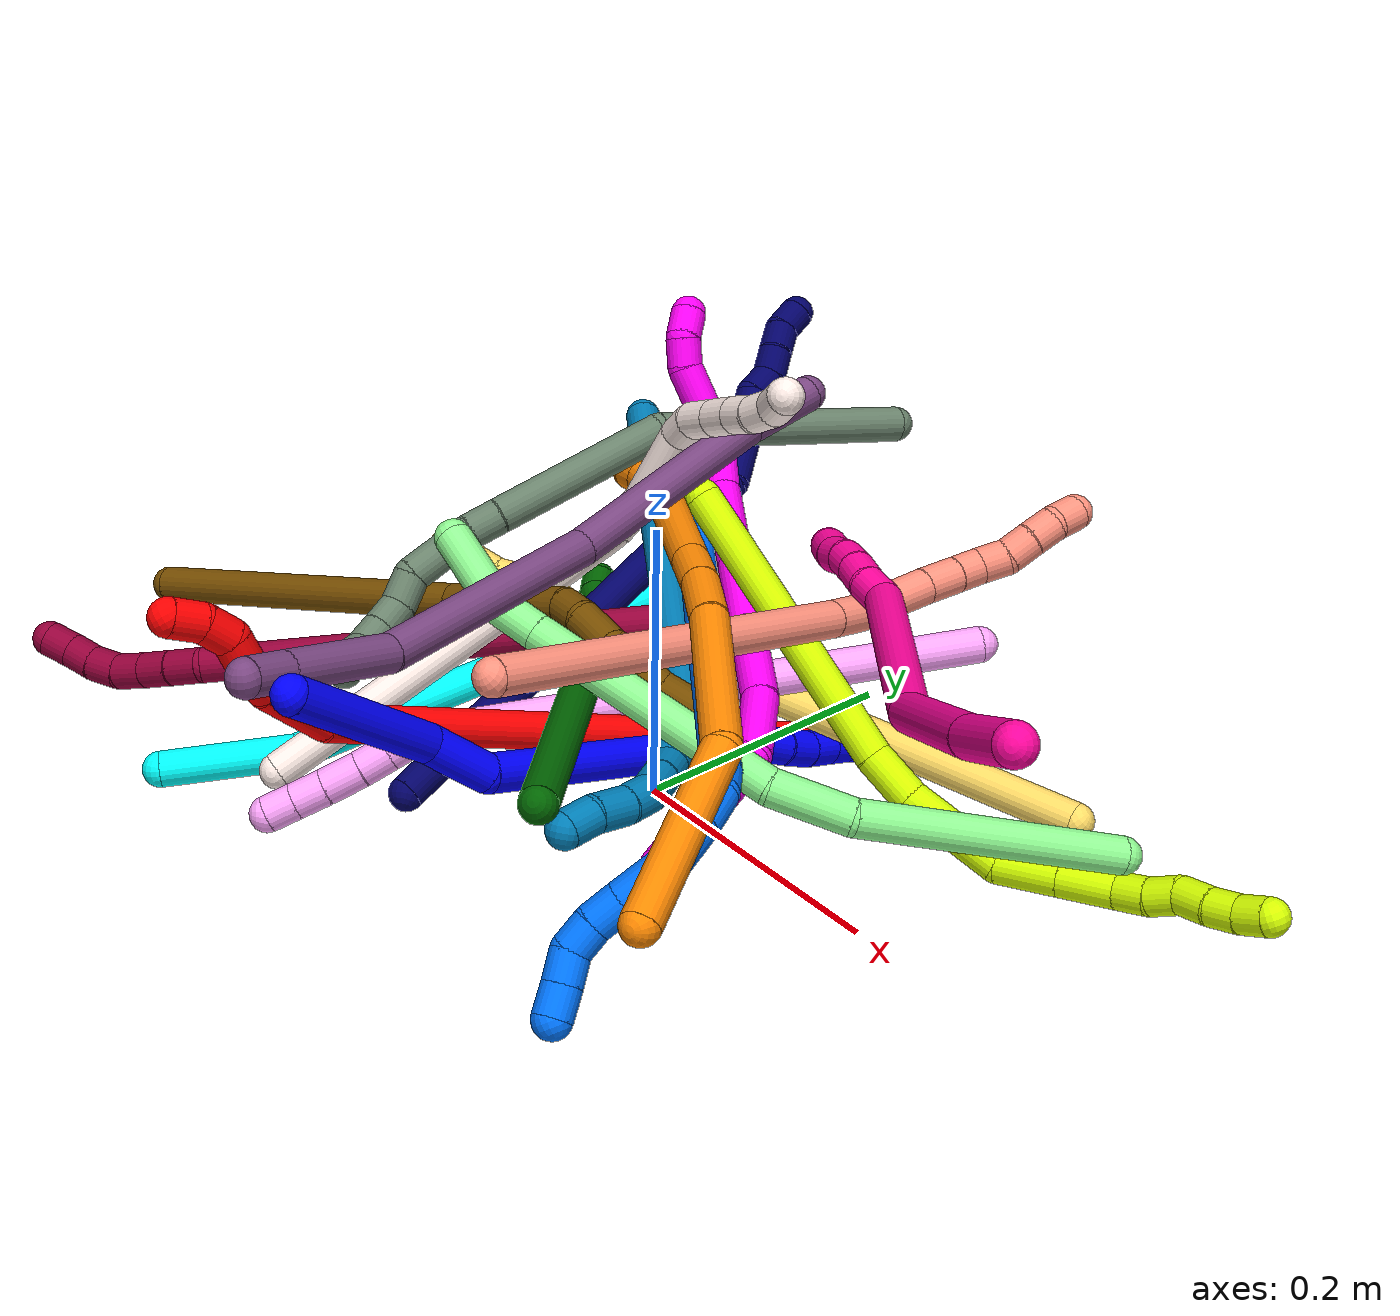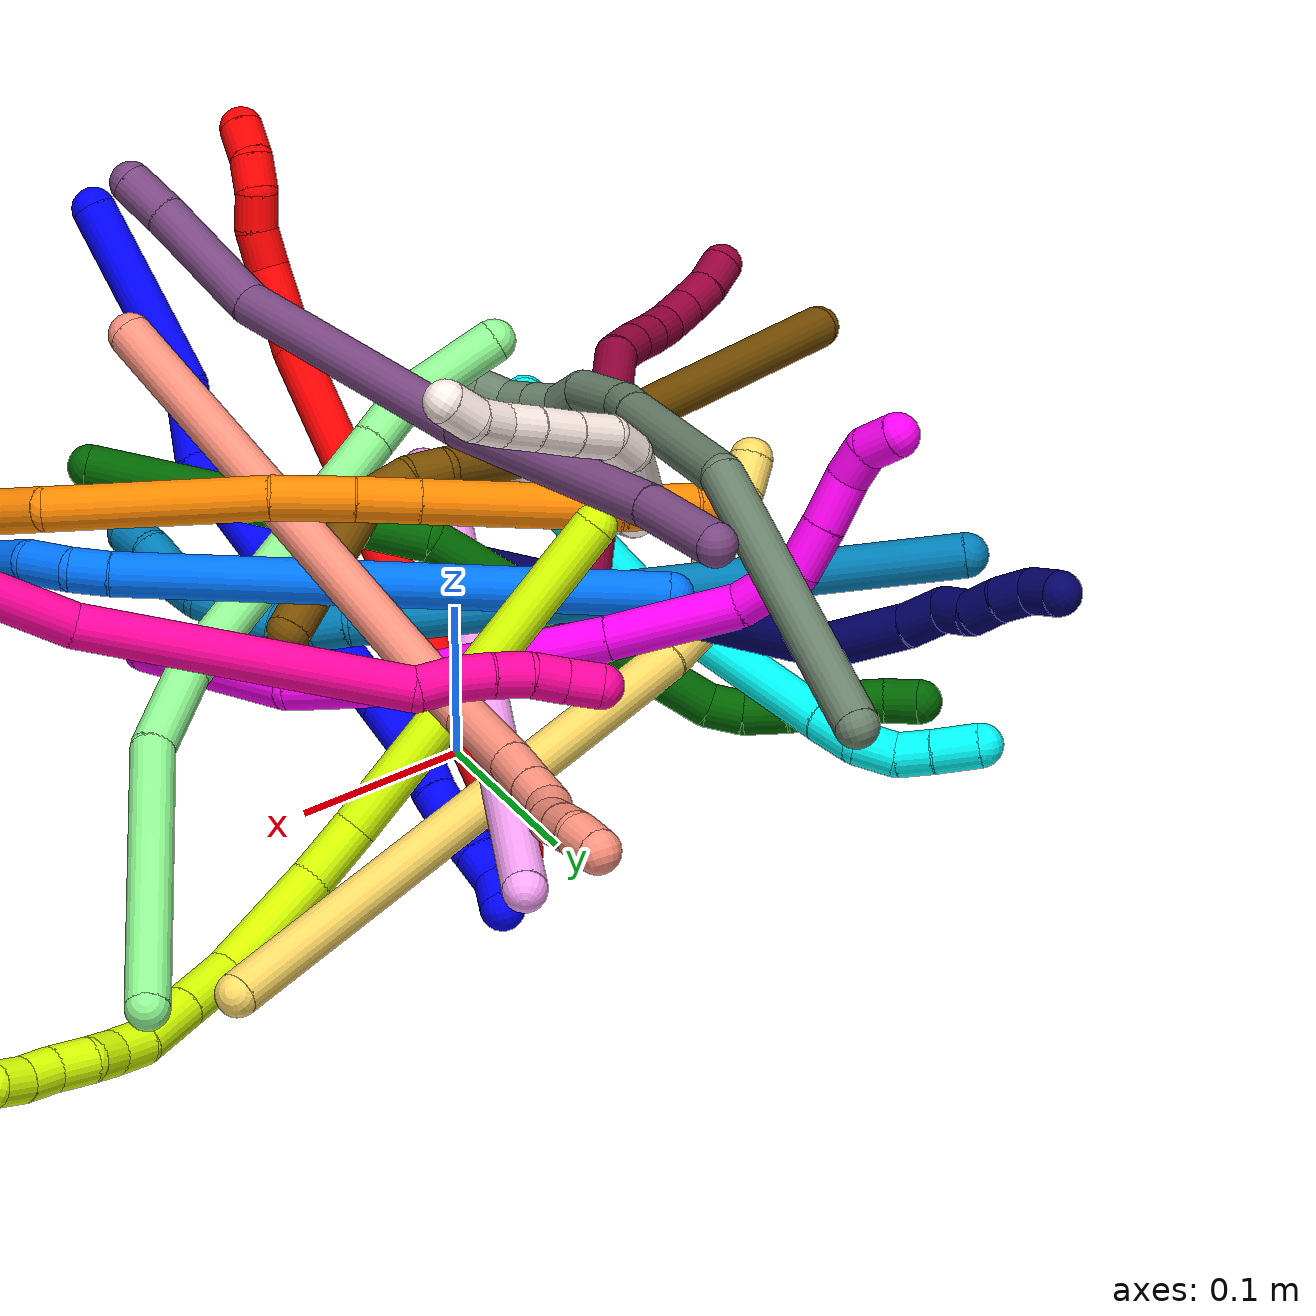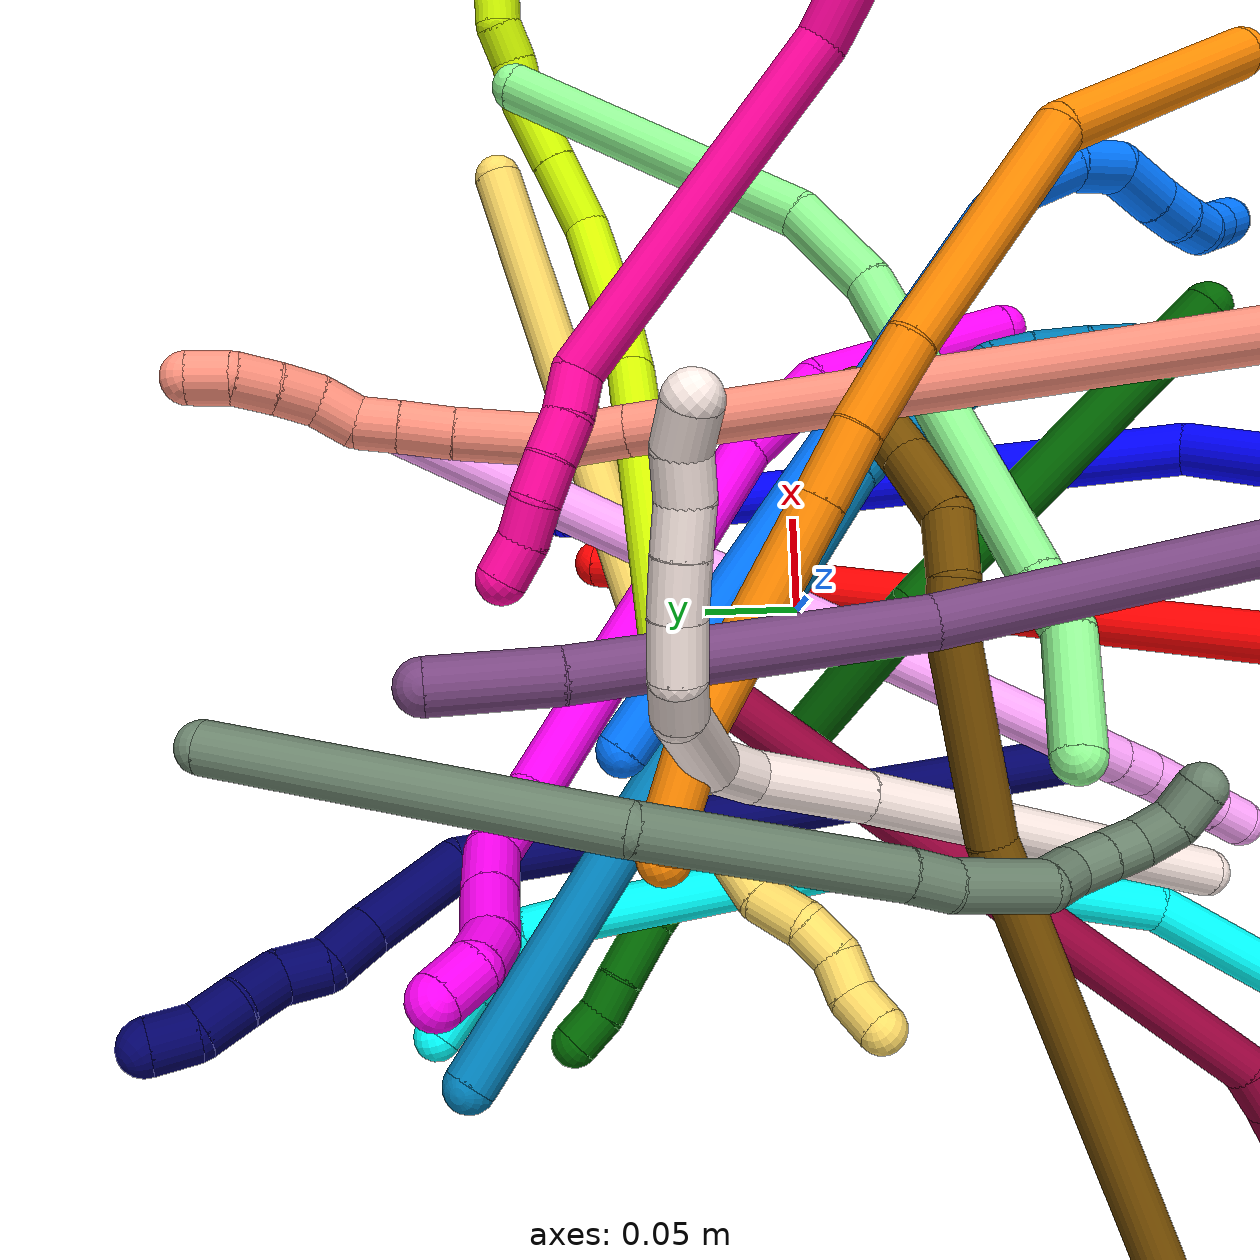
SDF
<sdf version="1.7">
 <world name="default">
  <plugin name="TubeGeneratorPlugin" filename="libtube_generator_plugin.so"/>
  <model name="photoneo_s_sensor">
   <static>1</static>
   <pose>0 0 2 1.57079 1.57079 3.14159</pose>
   <link name="link">
    <inertial><mass>0.1</mass></inertial>
    <sensor name="sensor" type="depth">
     <update_rate>30</update_rate>
     <camera>
      <horizontal_fov>1.22</horizontal_fov>
      <image><width>1920</width><height>1200</height><format>B8G8R8</format></image>
      <clip><near>0.1</near><far>4</far></clip>
      <depth_camera><output>points</output></depth_camera>
     </camera>
     <plugin name="camera_plugin" filename="libgazebo_ros_depth_camera.so">
      <baseline>0.2</baseline>
      <alwaysOn>1</alwaysOn>
      <updateRate>0.0</updateRate>
      <cameraName>camera_ir</cameraName>
      <imageTopicName>/camera/color/image_raw</imageTopicName>
      <cameraInfoTopicName>/camera/color/camera_info</cameraInfoTopicName>
      <depthImageTopicName>/camera/depth/image_raw</depthImageTopicName>
      <depthImageCameraInfoTopicName>/camera/depth/camera_info</depthImageCameraInfoTopicName>
      <pointCloudTopicName>/camera/depth/points</pointCloudTopicName>
      <frameName>fr_optical</frameName>
      <pointCloudCutoff>0.1</pointCloudCutoff>
      <pointCloudCutoffMax>2.0</pointCloudCutoffMax>
      <distortionK1>0</distortionK1>
      <distortionK2>0</distortionK2>
      <distortionK3>0</distortionK3>
      <distortionT1>0</distortionT1>
      <distortionT2>0</distortionT2>
      <CxPrime>0</CxPrime>
      <Cx>0</Cx>
      <Cy>0</Cy>
      <focalLength>0</focalLength>
      <hackBaseline>0</hackBaseline>
     </plugin>
    </sensor>
   </link>
  </model>
  <gravity>0 0 -9.8</gravity>
  <magnetic_field>6e-06 2.3e-05 -4.2e-05</magnetic_field>
  <atmosphere type="adiabatic"/>
  <physics name="default_physics" default="0" type="ode">
   <max_step_size>0.003</max_step_size>
   <real_time_factor>1</real_time_factor>
   <real_time_update_rate>1000</real_time_update_rate>
   <max_contacts>10000</max_contacts>
   <ode>
    <solver>
     <type>quick</type>
     <iters>100</iters>
     <sor>1.3</sor>
     <use_dynamic_moi_rescaling>0</use_dynamic_moi_rescaling>
    </solver>
    <constraints>
     <contact_max_correcting_vel>0</contact_max_correcting_vel>
     <contact_surface_layer>0.001</contact_surface_layer>
     <cfm>0</cfm>
     <erp>0.2</erp>
    </constraints>
   </ode>
  </physics>
  <scene><ambient>0.4 0.4 0.4 1</ambient><background>0.7 0.7 0.7 1</background><shadows>0</shadows></scene>
  <audio><device>default</device></audio>
  <spherical_coordinates>
   <surface_model>EARTH_WGS84</surface_model>
   <latitude_deg>0</latitude_deg>
   <longitude_deg>0</longitude_deg>
   <elevation>0</elevation>
   <heading_deg>0</heading_deg>
  </spherical_coordinates>
  <model name="bin">
   <static>1</static>
   <link name="bottom">
    <collision name="collision-bottom">
     <pose>0 0 -0.01 0 -0 0</pose>
     <geometry><box><size>0.8 0.6 0.02</size></box></geometry>
     <surface>
      <friction><ode><mu>100</mu><mu2>100</mu2></ode></friction>
      <contact><collide_bitmask>65535</collide_bitmask></contact>
     </surface>
    </collision>
   </link>
   <link name="west_wall">
    <collision name="collision-west_wall">
     <pose>-0.41 0 0.1 0 -0 0</pose>
     <geometry><box><size>0.02 0.6 0.2</size></box></geometry>
     <surface>
      <friction><ode><mu>100</mu><mu2>100</mu2></ode></friction>
      <contact><collide_bitmask>65535</collide_bitmask></contact>
     </surface>
    </collision>
   </link>
   <link name="east_wall">
    <collision name="collision-east_wall">
     <pose>0.41 0 0.1 0 -0 0</pose>
     <geometry><box><size>0.02 0.6 0.2</size></box></geometry>
     <surface>
      <friction><ode><mu>100</mu><mu2>100</mu2></ode></friction>
      <contact><collide_bitmask>65535</collide_bitmask></contact>
     </surface>
    </collision>
   </link>
   <link name="south_wall">
    <collision name="collision-south_wall">
     <pose>0 -0.31 0.1 0 -0 0</pose>
     <geometry><box><size>0.8 0.02 0.2</size></box></geometry>
     <surface>
      <friction><ode><mu>100</mu><mu2>100</mu2></ode></friction>
      <contact><collide_bitmask>65535</collide_bitmask></contact>
     </surface>
    </collision>
   </link>
   <link name="north_wall">
    <collision name="collision-north_wall">
     <pose>0 0.31 0.1 0 -0 0</pose>
     <geometry><box><size>0.8 0.02 0.2</size></box></geometry>
     <surface>
      <friction><ode><mu>100</mu><mu2>100</mu2></ode></friction>
      <contact><collide_bitmask>65535</collide_bitmask></contact>
     </surface>
    </collision>
   </link>
  </model>
  <model name="1">
   <static>0</static>
   <link name="1">
    <collision name="collision-cylinder-e_1_1_4">
     <pose>0.000733 0.022248 -0.053082 -2.74471 0.012741 -0.063341</pose>
     <geometry><cylinder><radius>0.0125</radius><length>0.115122</length></cylinder></geometry>
     <surface>
      <friction><ode><mu>1.16</mu><mu2>1.16</mu2><slip1>0</slip1><slip2>0</slip2></ode></friction>
      <contact><ode><kp>1e+06</kp><kd>1</kd><max_vel>0</max_vel><min_depth>0.001</min_depth></ode></contact>
     </surface>
    </collision>
    <visual name="visual-cylinder-e_1_1_4">
     <pose>0.000733 0.022248 -0.053082 -2.74471 0.012741 -0.063341</pose>
     <geometry><cylinder><radius>0.0125</radius><length>0.115122</length></cylinder></geometry>
     <material><ambient>0 0 1 1</ambient></material>
    </visual>
    <collision name="collision-cylinder-e_2_4_5">
     <pose>0.008862 0.050618 -0.126585 -2.85034 0.333932 -1.70936</pose>
     <geometry><cylinder><radius>0.0125</radius><length>0.045128</length></cylinder></geometry>
     <surface>
      <friction><ode><mu>1.16</mu><mu2>1.16</mu2><slip1>0</slip1><slip2>0</slip2></ode></friction>
      <contact><ode><kp>1e+06</kp><kd>1</kd><max_vel>0</max_vel><min_depth>0.001</min_depth></ode></contact>
     </surface>
    </collision>
    <visual name="visual-cylinder-e_2_4_5">
     <pose>0.008862 0.050618 -0.126585 -2.85034 0.333932 -1.70936</pose>
     <geometry><cylinder><radius>0.0125</radius><length>0.045128</length></cylinder></geometry>
     <material><ambient>0 0 1 1</ambient></material>
    </visual>
    <collision name="collision-cylinder-e_3_5_6">
     <pose>0.023188 0.122661 -0.218068 -2.39371 0.071377 -0.181475</pose>
     <geometry><cylinder><radius>0.0125</radius><length>0.194357</length></cylinder></geometry>
     <surface>
      <friction><ode><mu>1.16</mu><mu2>1.16</mu2><slip1>0</slip1><slip2>0</slip2></ode></friction>
      <contact><ode><kp>1e+06</kp><kd>1</kd><max_vel>0</max_vel><min_depth>0.001</min_depth></ode></contact>
     </surface>
    </collision>
    <visual name="visual-cylinder-e_3_5_6">
     <pose>0.023188 0.122661 -0.218068 -2.39371 0.071377 -0.181475</pose>
     <geometry><cylinder><radius>0.0125</radius><length>0.194357</length></cylinder></geometry>
     <material><ambient>0 0 1 1</ambient></material>
    </visual>
    <collision name="collision-cylinder-e_4_6_7">
     <pose>0.031397 0.200889 -0.302344 -2.39167 0.070679 -0.179171</pose>
     <geometry><cylinder><radius>0.0125</radius><length>0.036203</length></cylinder></geometry>
     <surface>
      <friction><ode><mu>1.16</mu><mu2>1.16</mu2><slip1>0</slip1><slip2>0</slip2></ode></friction>
      <contact><ode><kp>1e+06</kp><kd>1</kd><max_vel>0</max_vel><min_depth>0.001</min_depth></ode></contact>
     </surface>
    </collision>
    <visual name="visual-cylinder-e_4_6_7">
     <pose>0.031397 0.200889 -0.302344 -2.39167 0.070679 -0.179171</pose>
     <geometry><cylinder><radius>0.0125</radius><length>0.036203</length></cylinder></geometry>
     <material><ambient>0 0 1 1</ambient></material>
    </visual>
    <collision name="collision-cylinder-e_5_7_8">
     <pose>0.035304 0.219611 -0.32567 -2.57632 0.216023 -0.714698</pose>
     <geometry><cylinder><radius>0.0125</radius><length>0.024522</length></cylinder></geometry>
     <surface>
      <friction><ode><mu>1.16</mu><mu2>1.16</mu2><slip1>0</slip1><slip2>0</slip2></ode></friction>
      <contact><ode><kp>1e+06</kp><kd>1</kd><max_vel>0</max_vel><min_depth>0.001</min_depth></ode></contact>
     </surface>
    </collision>
    <visual name="visual-cylinder-e_5_7_8">
     <pose>0.035304 0.219611 -0.32567 -2.57632 0.216023 -0.714698</pose>
     <geometry><cylinder><radius>0.0125</radius><length>0.024522</length></cylinder></geometry>
     <material><ambient>0 0 1 1</ambient></material>
    </visual>
    <collision name="collision-cylinder-e_6_8_9">
     <pose>0.038777 0.232731 -0.345546 -2.5398 0.071239 -0.228666</pose>
     <geometry><cylinder><radius>0.0125</radius><length>0.023748</length></cylinder></geometry>
     <surface>
      <friction><ode><mu>1.16</mu><mu2>1.16</mu2><slip1>0</slip1><slip2>0</slip2></ode></friction>
      <contact><ode><kp>1e+06</kp><kd>1</kd><max_vel>0</max_vel><min_depth>0.001</min_depth></ode></contact>
     </surface>
    </collision>
    <visual name="visual-cylinder-e_6_8_9">
     <pose>0.038777 0.232731 -0.345546 -2.5398 0.071239 -0.228666</pose>
     <geometry><cylinder><radius>0.0125</radius><length>0.023748</length></cylinder></geometry>
     <material><ambient>0 0 1 1</ambient></material>
    </visual>
    <collision name="collision-cylinder-e_7_9_10">
     <pose>0.040196 0.246383 -0.362951 -2.40381 0.055487 -0.143319</pose>
     <geometry><cylinder><radius>0.0125</radius><length>0.020688</length></cylinder></geometry>
     <surface>
      <friction><ode><mu>1.16</mu><mu2>1.16</mu2><slip1>0</slip1><slip2>0</slip2></ode></friction>
      <contact><ode><kp>1e+06</kp><kd>1</kd><max_vel>0</max_vel><min_depth>0.001</min_depth></ode></contact>
     </surface>
    </collision>
    <visual name="visual-cylinder-e_7_9_10">
     <pose>0.040196 0.246383 -0.362951 -2.40381 0.055487 -0.143319</pose>
     <geometry><cylinder><radius>0.0125</radius><length>0.020688</length></cylinder></geometry>
     <material><ambient>0 0 1 1</ambient></material>
    </visual>
    <collision name="collision-cylinder-e_8_10_11">
     <pose>0.041402 0.260126 -0.378047 -2.40233 0.06267 -0.161456</pose>
     <geometry><cylinder><radius>0.0125</radius><length>0.020214</length></cylinder></geometry>
     <surface>
      <friction><ode><mu>1.16</mu><mu2>1.16</mu2><slip1>0</slip1><slip2>0</slip2></ode></friction>
      <contact><ode><kp>1e+06</kp><kd>1</kd><max_vel>0</max_vel><min_depth>0.001</min_depth></ode></contact>
     </surface>
    </collision>
    <visual name="visual-cylinder-e_8_10_11">
     <pose>0.041402 0.260126 -0.378047 -2.40233 0.06267 -0.161456</pose>
     <geometry><cylinder><radius>0.0125</radius><length>0.020214</length></cylinder></geometry>
     <material><ambient>0 0 1 1</ambient></material>
    </visual>
    <collision name="collision-cylinder-e_9_11_2">
     <pose>0.046845 0.273145 -0.391692 -2.35351 0.501247 -1.10379</pose>
     <geometry><cylinder><radius>0.0125</radius><length>0.020019</length></cylinder></geometry>
     <surface>
      <friction><ode><mu>1.16</mu><mu2>1.16</mu2><slip1>0</slip1><slip2>0</slip2></ode></friction>
      <contact><ode><kp>1e+06</kp><kd>1</kd><max_vel>0</max_vel><min_depth>0.001</min_depth></ode></contact>
     </surface>
    </collision>
    <visual name="visual-cylinder-e_9_11_2">
     <pose>0.046845 0.273145 -0.391692 -2.35351 0.501247 -1.10379</pose>
     <geometry><cylinder><radius>0.0125</radius><length>0.020019</length></cylinder></geometry>
     <material><ambient>0 0 1 1</ambient></material>
    </visual>
    <collision name="collision-sphere-2">
     <pose>0.051655 0.279369 -0.397882 0 -0 0</pose>
     <geometry><sphere><radius>0.0125</radius></sphere></geometry>
     <surface>
      <friction><ode><mu>1.16</mu><mu2>1.16</mu2><slip1>0</slip1><slip2>0</slip2></ode></friction>
      <contact><ode><kp>1e+06</kp><kd>1</kd><max_vel>0</max_vel><min_depth>0.001</min_depth></ode></contact>
     </surface>
    </collision>
    <visual name="visual-sphere-2">
     <pose>0.051655 0.279369 -0.397882 0 -0 0</pose>
     <geometry><sphere><radius>0.0125</radius></sphere></geometry>
     <material><ambient>0 0 1 1</ambient></material>
    </visual>
    <collision name="collision-sphere-11">
     <pose>0.042035 0.266922 -0.385501 0 -0 0</pose>
     <geometry><sphere><radius>0.0125</radius></sphere></geometry>
     <surface>
      <friction><ode><mu>1.16</mu><mu2>1.16</mu2><slip1>0</slip1><slip2>0</slip2></ode></friction>
      <contact><ode><kp>1e+06</kp><kd>1</kd><max_vel>0</max_vel><min_depth>0.001</min_depth></ode></contact>
     </surface>
    </collision>
    <visual name="visual-sphere-11">
     <pose>0.042035 0.266922 -0.385501 0 -0 0</pose>
     <geometry><sphere><radius>0.0125</radius></sphere></geometry>
     <material><ambient>0 0 1 1</ambient></material>
    </visual>
    <collision name="collision-sphere-10">
     <pose>0.040769 0.25333 -0.370593 0 -0 0</pose>
     <geometry><sphere><radius>0.0125</radius></sphere></geometry>
     <surface>
      <friction><ode><mu>1.16</mu><mu2>1.16</mu2><slip1>0</slip1><slip2>0</slip2></ode></friction>
      <contact><ode><kp>1e+06</kp><kd>1</kd><max_vel>0</max_vel><min_depth>0.001</min_depth></ode></contact>
     </surface>
    </collision>
    <visual name="visual-sphere-10">
     <pose>0.040769 0.25333 -0.370593 0 -0 0</pose>
     <geometry><sphere><radius>0.0125</radius></sphere></geometry>
     <material><ambient>0 0 1 1</ambient></material>
    </visual>
    <collision name="collision-sphere-9">
     <pose>0.039622 0.239436 -0.355309 0 -0 0</pose>
     <geometry><sphere><radius>0.0125</radius></sphere></geometry>
     <surface>
      <friction><ode><mu>1.16</mu><mu2>1.16</mu2><slip1>0</slip1><slip2>0</slip2></ode></friction>
      <contact><ode><kp>1e+06</kp><kd>1</kd><max_vel>0</max_vel><min_depth>0.001</min_depth></ode></contact>
     </surface>
    </collision>
    <visual name="visual-sphere-9">
     <pose>0.039622 0.239436 -0.355309 0 -0 0</pose>
     <geometry><sphere><radius>0.0125</radius></sphere></geometry>
     <material><ambient>0 0 1 1</ambient></material>
    </visual>
    <collision name="collision-sphere-4">
     <pose>0.001467 0.044497 -0.106165 0 -0 0</pose>
     <geometry><sphere><radius>0.0125</radius></sphere></geometry>
     <surface>
      <friction><ode><mu>1.16</mu><mu2>1.16</mu2><slip1>0</slip1><slip2>0</slip2></ode></friction>
      <contact><ode><kp>1e+06</kp><kd>1</kd><max_vel>0</max_vel><min_depth>0.001</min_depth></ode></contact>
     </surface>
    </collision>
    <visual name="visual-sphere-4">
     <pose>0.001467 0.044497 -0.106165 0 -0 0</pose>
     <geometry><sphere><radius>0.0125</radius></sphere></geometry>
     <material><ambient>0 0 1 1</ambient></material>
    </visual>
    <collision name="collision-sphere-1">
     <geometry><sphere><radius>0.0125</radius></sphere></geometry>
     <surface>
      <friction><ode><mu>1.16</mu><mu2>1.16</mu2><slip1>0</slip1><slip2>0</slip2></ode></friction>
      <contact><ode><kp>1e+06</kp><kd>1</kd><max_vel>0</max_vel><min_depth>0.001</min_depth></ode></contact>
     </surface>
    </collision>
    <visual name="visual-sphere-1">
     <geometry><sphere><radius>0.0125</radius></sphere></geometry>
     <material><ambient>0 0 1 1</ambient></material>
    </visual>
    <collision name="collision-sphere-8">
     <pose>0.037932 0.226026 -0.335783 0 -0 0</pose>
     <geometry><sphere><radius>0.0125</radius></sphere></geometry>
     <surface>
      <friction><ode><mu>1.16</mu><mu2>1.16</mu2><slip1>0</slip1><slip2>0</slip2></ode></friction>
      <contact><ode><kp>1e+06</kp><kd>1</kd><max_vel>0</max_vel><min_depth>0.001</min_depth></ode></contact>
     </surface>
    </collision>
    <visual name="visual-sphere-8">
     <pose>0.037932 0.226026 -0.335783 0 -0 0</pose>
     <geometry><sphere><radius>0.0125</radius></sphere></geometry>
     <material><ambient>0 0 1 1</ambient></material>
    </visual>
    <collision name="collision-sphere-5">
     <pose>0.016258 0.056739 -0.147005 0 -0 0</pose>
     <geometry><sphere><radius>0.0125</radius></sphere></geometry>
     <surface>
      <friction><ode><mu>1.16</mu><mu2>1.16</mu2><slip1>0</slip1><slip2>0</slip2></ode></friction>
      <contact><ode><kp>1e+06</kp><kd>1</kd><max_vel>0</max_vel><min_depth>0.001</min_depth></ode></contact>
     </surface>
    </collision>
    <visual name="visual-sphere-5">
     <pose>0.016258 0.056739 -0.147005 0 -0 0</pose>
     <geometry><sphere><radius>0.0125</radius></sphere></geometry>
     <material><ambient>0 0 1 1</ambient></material>
    </visual>
    <collision name="collision-sphere-6">
     <pose>0.030119 0.188582 -0.289132 0 -0 0</pose>
     <geometry><sphere><radius>0.0125</radius></sphere></geometry>
     <surface>
      <friction><ode><mu>1.16</mu><mu2>1.16</mu2><slip1>0</slip1><slip2>0</slip2></ode></friction>
      <contact><ode><kp>1e+06</kp><kd>1</kd><max_vel>0</max_vel><min_depth>0.001</min_depth></ode></contact>
     </surface>
    </collision>
    <visual name="visual-sphere-6">
     <pose>0.030119 0.188582 -0.289132 0 -0 0</pose>
     <geometry><sphere><radius>0.0125</radius></sphere></geometry>
     <material><ambient>0 0 1 1</ambient></material>
    </visual>
    <collision name="collision-sphere-7">
     <pose>0.032675 0.213196 -0.315557 0 -0 0</pose>
     <geometry><sphere><radius>0.0125</radius></sphere></geometry>
     <surface>
      <friction><ode><mu>1.16</mu><mu2>1.16</mu2><slip1>0</slip1><slip2>0</slip2></ode></friction>
      <contact><ode><kp>1e+06</kp><kd>1</kd><max_vel>0</max_vel><min_depth>0.001</min_depth></ode></contact>
     </surface>
    </collision>
    <visual name="visual-sphere-7">
     <pose>0.032675 0.213196 -0.315557 0 -0 0</pose>
     <geometry><sphere><radius>0.0125</radius></sphere></geometry>
     <material><ambient>0 0 1 1</ambient></material>
    </visual>
    <inertial>
     <pose>0.021041 0.125387 -0.208672 0 -0 0</pose>
     <mass>0.5</mass>
     <inertia>
      <ixx>0.000621</ixx>
      <ixy>0</ixy>
      <ixz>0</ixz>
      <iyy>-0.00068</iyy>
      <iyz>0</iyz>
      <izz>-0.000564</izz>
     </inertia>
    </inertial>
   </link>
   <pose>0.046915 -0.300897 0.215191 0.513061 -0.094899 0.125913</pose>
  </model>
  <model name="2">
   <static>0</static>
   <link name="2">
    <collision name="collision-cylinder-e_1_1_4">
     <pose>0.044832 -0.1276 -0.120019 2.32559 0.250547 0.566983</pose>
     <geometry><cylinder><radius>0.0125</radius><length>0.361641</length></cylinder></geometry>
     <surface>
      <friction><ode><mu>1.16</mu><mu2>1.16</mu2><slip1>0</slip1><slip2>0</slip2></ode></friction>
      <contact><ode><kp>1e+06</kp><kd>1</kd><max_vel>0</max_vel><min_depth>0.001</min_depth></ode></contact>
     </surface>
    </collision>
    <visual name="visual-cylinder-e_1_1_4">
     <pose>0.044832 -0.1276 -0.120019 2.32559 0.250547 0.566983</pose>
     <geometry><cylinder><radius>0.0125</radius><length>0.361641</length></cylinder></geometry>
     <material><ambient>1 0 0 1</ambient></material>
    </visual>
    <collision name="collision-cylinder-e_2_4_5">
     <pose>0.095067 -0.279358 -0.247589 1.87373 0.210349 0.285238</pose>
     <geometry><cylinder><radius>0.0125</radius><length>0.051764</length></cylinder></geometry>
     <surface>
      <friction><ode><mu>1.16</mu><mu2>1.16</mu2><slip1>0</slip1><slip2>0</slip2></ode></friction>
      <contact><ode><kp>1e+06</kp><kd>1</kd><max_vel>0</max_vel><min_depth>0.001</min_depth></ode></contact>
     </surface>
    </collision>
    <visual name="visual-cylinder-e_2_4_5">
     <pose>0.095067 -0.279358 -0.247589 1.87373 0.210349 0.285238</pose>
     <geometry><cylinder><radius>0.0125</radius><length>0.051764</length></cylinder></geometry>
     <material><ambient>1 0 0 1</ambient></material>
    </visual>
    <collision name="collision-cylinder-e_3_5_6">
     <pose>0.102778 -0.314869 -0.254927 1.55202 0.200387 0.196683</pose>
     <geometry><cylinder><radius>0.0125</radius><length>0.02317</length></cylinder></geometry>
     <surface>
      <friction><ode><mu>1.16</mu><mu2>1.16</mu2><slip1>0</slip1><slip2>0</slip2></ode></friction>
      <contact><ode><kp>1e+06</kp><kd>1</kd><max_vel>0</max_vel><min_depth>0.001</min_depth></ode></contact>
     </surface>
    </collision>
    <visual name="visual-cylinder-e_3_5_6">
     <pose>0.102778 -0.314869 -0.254927 1.55202 0.200387 0.196683</pose>
     <geometry><cylinder><radius>0.0125</radius><length>0.02317</length></cylinder></geometry>
     <material><ambient>1 0 0 1</ambient></material>
    </visual>
    <collision name="collision-cylinder-e_4_6_7">
     <pose>0.104169 -0.336767 -0.253735 1.47831 -0.086165 -0.078551</pose>
     <geometry><cylinder><radius>0.0125</radius><length>0.021265</length></cylinder></geometry>
     <surface>
      <friction><ode><mu>1.16</mu><mu2>1.16</mu2><slip1>0</slip1><slip2>0</slip2></ode></friction>
      <contact><ode><kp>1e+06</kp><kd>1</kd><max_vel>0</max_vel><min_depth>0.001</min_depth></ode></contact>
     </surface>
    </collision>
    <visual name="visual-cylinder-e_4_6_7">
     <pose>0.104169 -0.336767 -0.253735 1.47831 -0.086165 -0.078551</pose>
     <geometry><cylinder><radius>0.0125</radius><length>0.021265</length></cylinder></geometry>
     <material><ambient>1 0 0 1</ambient></material>
    </visual>
    <collision name="collision-cylinder-e_5_7_8">
     <pose>0.103847 -0.356872 -0.256589 1.95211 0.057545 0.085042</pose>
     <geometry><cylinder><radius>0.0125</radius><length>0.020628</length></cylinder></geometry>
     <surface>
      <friction><ode><mu>1.16</mu><mu2>1.16</mu2><slip1>0</slip1><slip2>0</slip2></ode></friction>
      <contact><ode><kp>1e+06</kp><kd>1</kd><max_vel>0</max_vel><min_depth>0.001</min_depth></ode></contact>
     </surface>
    </collision>
    <visual name="visual-cylinder-e_5_7_8">
     <pose>0.103847 -0.356872 -0.256589 1.95211 0.057545 0.085042</pose>
     <geometry><cylinder><radius>0.0125</radius><length>0.020628</length></cylinder></geometry>
     <material><ambient>1 0 0 1</ambient></material>
    </visual>
    <collision name="collision-cylinder-e_6_8_2">
     <pose>0.106258 -0.374548 -0.267254 2.2704 0.169728 0.361571</pose>
     <geometry><cylinder><radius>0.0125</radius><length>0.021532</length></cylinder></geometry>
     <surface>
      <friction><ode><mu>1.16</mu><mu2>1.16</mu2><slip1>0</slip1><slip2>0</slip2></ode></friction>
      <contact><ode><kp>1e+06</kp><kd>1</kd><max_vel>0</max_vel><min_depth>0.001</min_depth></ode></contact>
     </surface>
    </collision>
    <visual name="visual-cylinder-e_6_8_2">
     <pose>0.106258 -0.374548 -0.267254 2.2704 0.169728 0.361571</pose>
     <geometry><cylinder><radius>0.0125</radius><length>0.021532</length></cylinder></geometry>
     <material><ambient>1 0 0 1</ambient></material>
    </visual>
    <collision name="collision-sphere-2">
     <pose>0.108077 -0.382667 -0.274087 0 -0 0</pose>
     <geometry><sphere><radius>0.0125</radius></sphere></geometry>
     <surface>
      <friction><ode><mu>1.16</mu><mu2>1.16</mu2><slip1>0</slip1><slip2>0</slip2></ode></friction>
      <contact><ode><kp>1e+06</kp><kd>1</kd><max_vel>0</max_vel><min_depth>0.001</min_depth></ode></contact>
     </surface>
    </collision>
    <visual name="visual-sphere-2">
     <pose>0.108077 -0.382667 -0.274087 0 -0 0</pose>
     <geometry><sphere><radius>0.0125</radius></sphere></geometry>
     <material><ambient>1 0 0 1</ambient></material>
    </visual>
    <collision name="collision-sphere-4">
     <pose>0.089663 -0.255199 -0.240038 0 -0 0</pose>
     <geometry><sphere><radius>0.0125</radius></sphere></geometry>
     <surface>
      <friction><ode><mu>1.16</mu><mu2>1.16</mu2><slip1>0</slip1><slip2>0</slip2></ode></friction>
      <contact><ode><kp>1e+06</kp><kd>1</kd><max_vel>0</max_vel><min_depth>0.001</min_depth></ode></contact>
     </surface>
    </collision>
    <visual name="visual-sphere-4">
     <pose>0.089663 -0.255199 -0.240038 0 -0 0</pose>
     <geometry><sphere><radius>0.0125</radius></sphere></geometry>
     <material><ambient>1 0 0 1</ambient></material>
    </visual>
    <collision name="collision-sphere-1">
     <geometry><sphere><radius>0.0125</radius></sphere></geometry>
     <surface>
      <friction><ode><mu>1.16</mu><mu2>1.16</mu2><slip1>0</slip1><slip2>0</slip2></ode></friction>
      <contact><ode><kp>1e+06</kp><kd>1</kd><max_vel>0</max_vel><min_depth>0.001</min_depth></ode></contact>
     </surface>
    </collision>
    <visual name="visual-sphere-1">
     <geometry><sphere><radius>0.0125</radius></sphere></geometry>
     <material><ambient>1 0 0 1</ambient></material>
    </visual>
    <collision name="collision-sphere-8">
     <pose>0.10444 -0.366429 -0.260421 0 -0 0</pose>
     <geometry><sphere><radius>0.0125</radius></sphere></geometry>
     <surface>
      <friction><ode><mu>1.16</mu><mu2>1.16</mu2><slip1>0</slip1><slip2>0</slip2></ode></friction>
      <contact><ode><kp>1e+06</kp><kd>1</kd><max_vel>0</max_vel><min_depth>0.001</min_depth></ode></contact>
     </surface>
    </collision>
    <visual name="visual-sphere-8">
     <pose>0.10444 -0.366429 -0.260421 0 -0 0</pose>
     <geometry><sphere><radius>0.0125</radius></sphere></geometry>
     <material><ambient>1 0 0 1</ambient></material>
    </visual>
    <collision name="collision-sphere-5">
     <pose>0.100472 -0.303517 -0.25514 0 -0 0</pose>
     <geometry><sphere><radius>0.0125</radius></sphere></geometry>
     <surface>
      <friction><ode><mu>1.16</mu><mu2>1.16</mu2><slip1>0</slip1><slip2>0</slip2></ode></friction>
      <contact><ode><kp>1e+06</kp><kd>1</kd><max_vel>0</max_vel><min_depth>0.001</min_depth></ode></contact>
     </surface>
    </collision>
    <visual name="visual-sphere-5">
     <pose>0.100472 -0.303517 -0.25514 0 -0 0</pose>
     <geometry><sphere><radius>0.0125</radius></sphere></geometry>
     <material><ambient>1 0 0 1</ambient></material>
    </visual>
    <collision name="collision-sphere-6">
     <pose>0.105084 -0.32622 -0.254714 0 -0 0</pose>
     <geometry><sphere><radius>0.0125</radius></sphere></geometry>
     <surface>
      <friction><ode><mu>1.16</mu><mu2>1.16</mu2><slip1>0</slip1><slip2>0</slip2></ode></friction>
      <contact><ode><kp>1e+06</kp><kd>1</kd><max_vel>0</max_vel><min_depth>0.001</min_depth></ode></contact>
     </surface>
    </collision>
    <visual name="visual-sphere-6">
     <pose>0.105084 -0.32622 -0.254714 0 -0 0</pose>
     <geometry><sphere><radius>0.0125</radius></sphere></geometry>
     <material><ambient>1 0 0 1</ambient></material>
    </visual>
    <collision name="collision-sphere-7">
     <pose>0.103254 -0.347315 -0.252757 0 -0 0</pose>
     <geometry><sphere><radius>0.0125</radius></sphere></geometry>
     <surface>
      <friction><ode><mu>1.16</mu><mu2>1.16</mu2><slip1>0</slip1><slip2>0</slip2></ode></friction>
      <contact><ode><kp>1e+06</kp><kd>1</kd><max_vel>0</max_vel><min_depth>0.001</min_depth></ode></contact>
     </surface>
    </collision>
    <visual name="visual-sphere-7">
     <pose>0.103254 -0.347315 -0.252757 0 -0 0</pose>
     <geometry><sphere><radius>0.0125</radius></sphere></geometry>
     <material><ambient>1 0 0 1</ambient></material>
    </visual>
    <inertial>
     <pose>0.060321 -0.180978 -0.15714 0 -0 0</pose>
     <mass>0.5</mass>
     <inertia>
      <ixx>0.005323</ixx>
      <ixy>0</ixy>
      <ixz>0</ixz>
      <iyy>0.000126</iyy>
      <iyz>0</iyz>
      <izz>0.001805</izz>
     </inertia>
    </inertial>
   </link>
   <pose>0.027718 0.107981 0.011693 -1.09179 0.025914 -0.469892</pose>
  </model>
  <model name="3">
   <static>0</static>
   <link name="3">
    <collision name="collision-cylinder-e_1_1_4">
     <pose>-0.004658 0.033006 0.032144 -0.798628 -0.10075 0.042545</pose>
     <geometry><cylinder><radius>0.0125</radius><length>0.092615</length></cylinder></geometry>
     <surface>
      <friction><ode><mu>1.16</mu><mu2>1.16</mu2><slip1>0</slip1><slip2>0</slip2></ode></friction>
      <contact><ode><kp>1e+06</kp><kd>1</kd><max_vel>0</max_vel><min_depth>0.001</min_depth></ode></contact>
     </surface>
    </collision>
    <visual name="visual-cylinder-e_1_1_4">
     <pose>-0.004658 0.033006 0.032144 -0.798628 -0.10075 0.042545</pose>
     <geometry><cylinder><radius>0.0125</radius><length>0.092615</length></cylinder></geometry>
     <material><ambient>0.003922 1 0.996078 1</ambient></material>
    </visual>
    <collision name="collision-cylinder-e_2_4_5">
     <pose>-0.034211 0.136971 0.100139 -1.10298 -0.30348 0.187582</pose>
     <geometry><cylinder><radius>0.0125</radius><length>0.166615</length></cylinder></geometry>
     <surface>
      <friction><ode><mu>1.16</mu><mu2>1.16</mu2><slip1>0</slip1><slip2>0</slip2></ode></friction>
      <contact><ode><kp>1e+06</kp><kd>1</kd><max_vel>0</max_vel><min_depth>0.001</min_depth></ode></contact>
     </surface>
    </collision>
    <visual name="visual-cylinder-e_2_4_5">
     <pose>-0.034211 0.136971 0.100139 -1.10298 -0.30348 0.187582</pose>
     <geometry><cylinder><radius>0.0125</radius><length>0.166615</length></cylinder></geometry>
     <material><ambient>0.003922 1 0.996078 1</ambient></material>
    </visual>
    <collision name="collision-cylinder-e_3_5_6">
     <pose>-0.074894 0.278238 0.14005 -1.5131 -0.220523 0.208245</pose>
     <geometry><cylinder><radius>0.0125</radius><length>0.144348</length></cylinder></geometry>
     <surface>
      <friction><ode><mu>1.16</mu><mu2>1.16</mu2><slip1>0</slip1><slip2>0</slip2></ode></friction>
      <contact><ode><kp>1e+06</kp><kd>1</kd><max_vel>0</max_vel><min_depth>0.001</min_depth></ode></contact>
     </surface>
    </collision>
    <visual name="visual-cylinder-e_3_5_6">
     <pose>-0.074894 0.278238 0.14005 -1.5131 -0.220523 0.208245</pose>
     <geometry><cylinder><radius>0.0125</radius><length>0.144348</length></cylinder></geometry>
     <material><ambient>0.003922 1 0.996078 1</ambient></material>
    </visual>
    <collision name="collision-cylinder-e_4_6_7">
     <pose>-0.093676 0.361264 0.144144 -1.56824 -0.231271 0.230686</pose>
     <geometry><cylinder><radius>0.0125</radius><length>0.026128</length></cylinder></geometry>
     <surface>
      <friction><ode><mu>1.16</mu><mu2>1.16</mu2><slip1>0</slip1><slip2>0</slip2></ode></friction>
      <contact><ode><kp>1e+06</kp><kd>1</kd><max_vel>0</max_vel><min_depth>0.001</min_depth></ode></contact>
     </surface>
    </collision>
    <visual name="visual-cylinder-e_4_6_7">
     <pose>-0.093676 0.361264 0.144144 -1.56824 -0.231271 0.230686</pose>
     <geometry><cylinder><radius>0.0125</radius><length>0.026128</length></cylinder></geometry>
     <material><ambient>0.003922 1 0.996078 1</ambient></material>
    </visual>
    <collision name="collision-cylinder-e_5_7_8">
     <pose>-0.099292 0.383948 0.138845 -2.0619 -0.227865 0.377378</pose>
     <geometry><cylinder><radius>0.0125</radius><length>0.02321</length></cylinder></geometry>
     <surface>
      <friction><ode><mu>1.16</mu><mu2>1.16</mu2><slip1>0</slip1><slip2>0</slip2></ode></friction>
      <contact><ode><kp>1e+06</kp><kd>1</kd><max_vel>0</max_vel><min_depth>0.001</min_depth></ode></contact>
     </surface>
    </collision>
    <visual name="visual-cylinder-e_5_7_8">
     <pose>-0.099292 0.383948 0.138845 -2.0619 -0.227865 0.377378</pose>
     <geometry><cylinder><radius>0.0125</radius><length>0.02321</length></cylinder></geometry>
     <material><ambient>0.003922 1 0.996078 1</ambient></material>
    </visual>
    <collision name="collision-cylinder-e_6_8_9">
     <pose>-0.107597 0.400576 0.128483 -2.21774 -0.597886 1.10858</pose>
     <geometry><cylinder><radius>0.0125</radius><length>0.020194</length></cylinder></geometry>
     <surface>
      <friction><ode><mu>1.16</mu><mu2>1.16</mu2><slip1>0</slip1><slip2>0</slip2></ode></friction>
      <contact><ode><kp>1e+06</kp><kd>1</kd><max_vel>0</max_vel><min_depth>0.001</min_depth></ode></contact>
     </surface>
    </collision>
    <visual name="visual-cylinder-e_6_8_9">
     <pose>-0.107597 0.400576 0.128483 -2.21774 -0.597886 1.10858</pose>
     <geometry><cylinder><radius>0.0125</radius><length>0.020194</length></cylinder></geometry>
     <material><ambient>0.003922 1 0.996078 1</ambient></material>
    </visual>
    <collision name="collision-cylinder-e_7_9_2">
     <pose>-0.12084 0.415477 0.11599 -2.30666 -0.597096 1.21316</pose>
     <geometry><cylinder><radius>0.0125</radius><length>0.026891</length></cylinder></geometry>
     <surface>
      <friction><ode><mu>1.16</mu><mu2>1.16</mu2><slip1>0</slip1><slip2>0</slip2></ode></friction>
      <contact><ode><kp>1e+06</kp><kd>1</kd><max_vel>0</max_vel><min_depth>0.001</min_depth></ode></contact>
     </surface>
    </collision>
    <visual name="visual-cylinder-e_7_9_2">
     <pose>-0.12084 0.415477 0.11599 -2.30666 -0.597096 1.21316</pose>
     <geometry><cylinder><radius>0.0125</radius><length>0.026891</length></cylinder></geometry>
     <material><ambient>0.003922 1 0.996078 1</ambient></material>
    </visual>
    <collision name="collision-sphere-2">
     <pose>-0.1284 0.423719 0.108527 0 -0 0</pose>
     <geometry><sphere><radius>0.0125</radius></sphere></geometry>
     <surface>
      <friction><ode><mu>1.16</mu><mu2>1.16</mu2><slip1>0</slip1><slip2>0</slip2></ode></friction>
      <contact><ode><kp>1e+06</kp><kd>1</kd><max_vel>0</max_vel><min_depth>0.001</min_depth></ode></contact>
     </surface>
    </collision>
    <visual name="visual-sphere-2">
     <pose>-0.1284 0.423719 0.108527 0 -0 0</pose>
     <geometry><sphere><radius>0.0125</radius></sphere></geometry>
     <material><ambient>0.003922 1 0.996078 1</ambient></material>
    </visual>
    <collision name="collision-sphere-9">
     <pose>-0.113281 0.407235 0.123453 0 -0 0</pose>
     <geometry><sphere><radius>0.0125</radius></sphere></geometry>
     <surface>
      <friction><ode><mu>1.16</mu><mu2>1.16</mu2><slip1>0</slip1><slip2>0</slip2></ode></friction>
      <contact><ode><kp>1e+06</kp><kd>1</kd><max_vel>0</max_vel><min_depth>0.001</min_depth></ode></contact>
     </surface>
    </collision>
    <visual name="visual-sphere-9">
     <pose>-0.113281 0.407235 0.123453 0 -0 0</pose>
     <geometry><sphere><radius>0.0125</radius></sphere></geometry>
     <material><ambient>0.003922 1 0.996078 1</ambient></material>
    </visual>
    <collision name="collision-sphere-4">
     <pose>-0.009315 0.066013 0.064289 0 -0 0</pose>
     <geometry><sphere><radius>0.0125</radius></sphere></geometry>
     <surface>
      <friction><ode><mu>1.16</mu><mu2>1.16</mu2><slip1>0</slip1><slip2>0</slip2></ode></friction>
      <contact><ode><kp>1e+06</kp><kd>1</kd><max_vel>0</max_vel><min_depth>0.001</min_depth></ode></contact>
     </surface>
    </collision>
    <visual name="visual-sphere-4">
     <pose>-0.009315 0.066013 0.064289 0 -0 0</pose>
     <geometry><sphere><radius>0.0125</radius></sphere></geometry>
     <material><ambient>0.003922 1 0.996078 1</ambient></material>
    </visual>
    <collision name="collision-sphere-1">
     <geometry><sphere><radius>0.0125</radius></sphere></geometry>
     <surface>
      <friction><ode><mu>1.16</mu><mu2>1.16</mu2><slip1>0</slip1><slip2>0</slip2></ode></friction>
      <contact><ode><kp>1e+06</kp><kd>1</kd><max_vel>0</max_vel><min_depth>0.001</min_depth></ode></contact>
     </surface>
    </collision>
    <visual name="visual-sphere-1">
     <geometry><sphere><radius>0.0125</radius></sphere></geometry>
     <material><ambient>0.003922 1 0.996078 1</ambient></material>
    </visual>
    <collision name="collision-sphere-8">
     <pose>-0.101914 0.393917 0.133514 0 -0 0</pose>
     <geometry><sphere><radius>0.0125</radius></sphere></geometry>
     <surface>
      <friction><ode><mu>1.16</mu><mu2>1.16</mu2><slip1>0</slip1><slip2>0</slip2></ode></friction>
      <contact><ode><kp>1e+06</kp><kd>1</kd><max_vel>0</max_vel><min_depth>0.001</min_depth></ode></contact>
     </surface>
    </collision>
    <visual name="visual-sphere-8">
     <pose>-0.101914 0.393917 0.133514 0 -0 0</pose>
     <geometry><sphere><radius>0.0125</radius></sphere></geometry>
     <material><ambient>0.003922 1 0.996078 1</ambient></material>
    </visual>
    <collision name="collision-sphere-5">
     <pose>-0.059107 0.207929 0.135989 0 -0 0</pose>
     <geometry><sphere><radius>0.0125</radius></sphere></geometry>
     <surface>
      <friction><ode><mu>1.16</mu><mu2>1.16</mu2><slip1>0</slip1><slip2>0</slip2></ode></friction>
      <contact><ode><kp>1e+06</kp><kd>1</kd><max_vel>0</max_vel><min_depth>0.001</min_depth></ode></contact>
     </surface>
    </collision>
    <visual name="visual-sphere-5">
     <pose>-0.059107 0.207929 0.135989 0 -0 0</pose>
     <geometry><sphere><radius>0.0125</radius></sphere></geometry>
     <material><ambient>0.003922 1 0.996078 1</ambient></material>
    </visual>
    <collision name="collision-sphere-6">
     <pose>-0.090682 0.348547 0.144111 0 -0 0</pose>
     <geometry><sphere><radius>0.0125</radius></sphere></geometry>
     <surface>
      <friction><ode><mu>1.16</mu><mu2>1.16</mu2><slip1>0</slip1><slip2>0</slip2></ode></friction>
      <contact><ode><kp>1e+06</kp><kd>1</kd><max_vel>0</max_vel><min_depth>0.001</min_depth></ode></contact>
     </surface>
    </collision>
    <visual name="visual-sphere-6">
     <pose>-0.090682 0.348547 0.144111 0 -0 0</pose>
     <geometry><sphere><radius>0.0125</radius></sphere></geometry>
     <material><ambient>0.003922 1 0.996078 1</ambient></material>
    </visual>
    <collision name="collision-sphere-7">
     <pose>-0.096671 0.37398 0.144176 0 -0 0</pose>
     <geometry><sphere><radius>0.0125</radius></sphere></geometry>
     <surface>
      <friction><ode><mu>1.16</mu><mu2>1.16</mu2><slip1>0</slip1><slip2>0</slip2></ode></friction>
      <contact><ode><kp>1e+06</kp><kd>1</kd><max_vel>0</max_vel><min_depth>0.001</min_depth></ode></contact>
     </surface>
    </collision>
    <visual name="visual-sphere-7">
     <pose>-0.096671 0.37398 0.144176 0 -0 0</pose>
     <geometry><sphere><radius>0.0125</radius></sphere></geometry>
     <material><ambient>0.003922 1 0.996078 1</ambient></material>
    </visual>
    <inertial>
     <pose>-0.054233 0.207307 0.10516 0 -0 0</pose>
     <mass>0.5</mass>
     <inertia>
      <ixx>0.000806</ixx>
      <ixy>0</ixy>
      <ixz>0</ixz>
      <iyy>0.00043</iyy>
      <iyz>0</iyz>
      <izz>-0.000448</izz>
     </inertia>
    </inertial>
   </link>
   <pose>-0.213638 -0.258263 0.012166 -0.832369 1.17523 -0.632008</pose>
  </model>
  <model name="4">
   <static>0</static>
   <link name="4">
    <collision name="collision-cylinder-e_1_1_4">
     <pose>-0.024561 -0.030937 0.189865 0.161523 -0.126991 -0.010292</pose>
     <geometry><cylinder><radius>0.0125</radius><length>0.38786</length></cylinder></geometry>
     <surface>
      <friction><ode><mu>1.16</mu><mu2>1.16</mu2><slip1>0</slip1><slip2>0</slip2></ode></friction>
      <contact><ode><kp>1e+06</kp><kd>1</kd><max_vel>0</max_vel><min_depth>0.001</min_depth></ode></contact>
     </surface>
    </collision>
    <visual name="visual-cylinder-e_1_1_4">
     <pose>-0.024561 -0.030937 0.189865 0.161523 -0.126991 -0.010292</pose>
     <geometry><cylinder><radius>0.0125</radius><length>0.38786</length></cylinder></geometry>
     <material><ambient>1 0.65098 0.996078 1</ambient></material>
    </visual>
    <collision name="collision-cylinder-e_2_4_5">
     <pose>-0.054332 -0.06518 0.388758 0.350992 -0.49655 -0.089843</pose>
     <geometry><cylinder><radius>0.0125</radius><length>0.02187</length></cylinder></geometry>
     <surface>
      <friction><ode><mu>1.16</mu><mu2>1.16</mu2><slip1>0</slip1><slip2>0</slip2></ode></friction>
      <contact><ode><kp>1e+06</kp><kd>1</kd><max_vel>0</max_vel><min_depth>0.001</min_depth></ode></contact>
     </surface>
    </collision>
    <visual name="visual-cylinder-e_2_4_5">
     <pose>-0.054332 -0.06518 0.388758 0.350992 -0.49655 -0.089843</pose>
     <geometry><cylinder><radius>0.0125</radius><length>0.02187</length></cylinder></geometry>
     <material><ambient>1 0.65098 0.996078 1</ambient></material>
    </visual>
    <collision name="collision-cylinder-e_3_5_6">
     <pose>-0.064521 -0.071868 0.406778 0.359757 -0.478155 -0.088587</pose>
     <geometry><cylinder><radius>0.0125</radius><length>0.021642</length></cylinder></geometry>
     <surface>
      <friction><ode><mu>1.16</mu><mu2>1.16</mu2><slip1>0</slip1><slip2>0</slip2></ode></friction>
      <contact><ode><kp>1e+06</kp><kd>1</kd><max_vel>0</max_vel><min_depth>0.001</min_depth></ode></contact>
     </surface>
    </collision>
    <visual name="visual-cylinder-e_3_5_6">
     <pose>-0.064521 -0.071868 0.406778 0.359757 -0.478155 -0.088587</pose>
     <geometry><cylinder><radius>0.0125</radius><length>0.021642</length></cylinder></geometry>
     <material><ambient>1 0.65098 0.996078 1</ambient></material>
    </visual>
    <collision name="collision-cylinder-e_4_6_7">
     <pose>-0.07538 -0.078632 0.427021 0.292024 -0.464061 -0.069468</pose>
     <geometry><cylinder><radius>0.0125</radius><length>0.026274</length></cylinder></geometry>
     <surface>
      <friction><ode><mu>1.16</mu><mu2>1.16</mu2><slip1>0</slip1><slip2>0</slip2></ode></friction>
      <contact><ode><kp>1e+06</kp><kd>1</kd><max_vel>0</max_vel><min_depth>0.001</min_depth></ode></contact>
     </surface>
    </collision>
    <visual name="visual-cylinder-e_4_6_7">
     <pose>-0.07538 -0.078632 0.427021 0.292024 -0.464061 -0.069468</pose>
     <geometry><cylinder><radius>0.0125</radius><length>0.026274</length></cylinder></geometry>
     <material><ambient>1 0.65098 0.996078 1</ambient></material>
    </visual>
    <collision name="collision-cylinder-e_5_7_8">
     <pose>-0.086006 -0.084613 0.447962 0.262032 -0.441836 -0.05917</pose>
     <geometry><cylinder><radius>0.0125</radius><length>0.022198</length></cylinder></geometry>
     <surface>
      <friction><ode><mu>1.16</mu><mu2>1.16</mu2><slip1>0</slip1><slip2>0</slip2></ode></friction>
      <contact><ode><kp>1e+06</kp><kd>1</kd><max_vel>0</max_vel><min_depth>0.001</min_depth></ode></contact>
     </surface>
    </collision>
    <visual name="visual-cylinder-e_5_7_8">
     <pose>-0.086006 -0.084613 0.447962 0.262032 -0.441836 -0.05917</pose>
     <geometry><cylinder><radius>0.0125</radius><length>0.022198</length></cylinder></geometry>
     <material><ambient>1 0.65098 0.996078 1</ambient></material>
    </visual>
    <collision name="collision-cylinder-e_6_8_2">
     <pose>-0.095061 -0.089586 0.466448 0.263604 -0.44185 -0.059531</pose>
     <geometry><cylinder><radius>0.0125</radius><length>0.020155</length></cylinder></geometry>
     <surface>
      <friction><ode><mu>1.16</mu><mu2>1.16</mu2><slip1>0</slip1><slip2>0</slip2></ode></friction>
      <contact><ode><kp>1e+06</kp><kd>1</kd><max_vel>0</max_vel><min_depth>0.001</min_depth></ode></contact>
     </surface>
    </collision>
    <visual name="visual-cylinder-e_6_8_2">
     <pose>-0.095061 -0.089586 0.466448 0.263604 -0.44185 -0.059531</pose>
     <geometry><cylinder><radius>0.0125</radius><length>0.020155</length></cylinder></geometry>
     <material><ambient>1 0.65098 0.996078 1</ambient></material>
    </visual>
    <collision name="collision-sphere-2">
     <pose>-0.09937 -0.09196 0.475243 0 -0 0</pose>
     <geometry><sphere><radius>0.0125</radius></sphere></geometry>
     <surface>
      <friction><ode><mu>1.16</mu><mu2>1.16</mu2><slip1>0</slip1><slip2>0</slip2></ode></friction>
      <contact><ode><kp>1e+06</kp><kd>1</kd><max_vel>0</max_vel><min_depth>0.001</min_depth></ode></contact>
     </surface>
    </collision>
    <visual name="visual-sphere-2">
     <pose>-0.09937 -0.09196 0.475243 0 -0 0</pose>
     <geometry><sphere><radius>0.0125</radius></sphere></geometry>
     <material><ambient>1 0.65098 0.996078 1</ambient></material>
    </visual>
    <collision name="collision-sphere-4">
     <pose>-0.049123 -0.061874 0.379729 0 -0 0</pose>
     <geometry><sphere><radius>0.0125</radius></sphere></geometry>
     <surface>
      <friction><ode><mu>1.16</mu><mu2>1.16</mu2><slip1>0</slip1><slip2>0</slip2></ode></friction>
      <contact><ode><kp>1e+06</kp><kd>1</kd><max_vel>0</max_vel><min_depth>0.001</min_depth></ode></contact>
     </surface>
    </collision>
    <visual name="visual-sphere-4">
     <pose>-0.049123 -0.061874 0.379729 0 -0 0</pose>
     <geometry><sphere><radius>0.0125</radius></sphere></geometry>
     <material><ambient>1 0.65098 0.996078 1</ambient></material>
    </visual>
    <collision name="collision-sphere-1">
     <geometry><sphere><radius>0.0125</radius></sphere></geometry>
     <surface>
      <friction><ode><mu>1.16</mu><mu2>1.16</mu2><slip1>0</slip1><slip2>0</slip2></ode></friction>
      <contact><ode><kp>1e+06</kp><kd>1</kd><max_vel>0</max_vel><min_depth>0.001</min_depth></ode></contact>
     </surface>
    </collision>
    <visual name="visual-sphere-1">
     <geometry><sphere><radius>0.0125</radius></sphere></geometry>
     <material><ambient>1 0.65098 0.996078 1</ambient></material>
    </visual>
    <collision name="collision-sphere-8">
     <pose>-0.090752 -0.087212 0.457653 0 -0 0</pose>
     <geometry><sphere><radius>0.0125</radius></sphere></geometry>
     <surface>
      <friction><ode><mu>1.16</mu><mu2>1.16</mu2><slip1>0</slip1><slip2>0</slip2></ode></friction>
      <contact><ode><kp>1e+06</kp><kd>1</kd><max_vel>0</max_vel><min_depth>0.001</min_depth></ode></contact>
     </surface>
    </collision>
    <visual name="visual-sphere-8">
     <pose>-0.090752 -0.087212 0.457653 0 -0 0</pose>
     <geometry><sphere><radius>0.0125</radius></sphere></geometry>
     <material><ambient>1 0.65098 0.996078 1</ambient></material>
    </visual>
    <collision name="collision-sphere-5">
     <pose>-0.059542 -0.068486 0.397786 0 -0 0</pose>
     <geometry><sphere><radius>0.0125</radius></sphere></geometry>
     <surface>
      <friction><ode><mu>1.16</mu><mu2>1.16</mu2><slip1>0</slip1><slip2>0</slip2></ode></friction>
      <contact><ode><kp>1e+06</kp><kd>1</kd><max_vel>0</max_vel><min_depth>0.001</min_depth></ode></contact>
     </surface>
    </collision>
    <visual name="visual-sphere-5">
     <pose>-0.059542 -0.068486 0.397786 0 -0 0</pose>
     <geometry><sphere><radius>0.0125</radius></sphere></geometry>
     <material><ambient>1 0.65098 0.996078 1</ambient></material>
    </visual>
    <collision name="collision-sphere-6">
     <pose>-0.0695 -0.07525 0.415771 0 -0 0</pose>
     <geometry><sphere><radius>0.0125</radius></sphere></geometry>
     <surface>
      <friction><ode><mu>1.16</mu><mu2>1.16</mu2><slip1>0</slip1><slip2>0</slip2></ode></friction>
      <contact><ode><kp>1e+06</kp><kd>1</kd><max_vel>0</max_vel><min_depth>0.001</min_depth></ode></contact>
     </surface>
    </collision>
    <visual name="visual-sphere-6">
     <pose>-0.0695 -0.07525 0.415771 0 -0 0</pose>
     <geometry><sphere><radius>0.0125</radius></sphere></geometry>
     <material><ambient>1 0.65098 0.996078 1</ambient></material>
    </visual>
    <collision name="collision-sphere-7">
     <pose>-0.08126 -0.082014 0.438271 0 -0 0</pose>
     <geometry><sphere><radius>0.0125</radius></sphere></geometry>
     <surface>
      <friction><ode><mu>1.16</mu><mu2>1.16</mu2><slip1>0</slip1><slip2>0</slip2></ode></friction>
      <contact><ode><kp>1e+06</kp><kd>1</kd><max_vel>0</max_vel><min_depth>0.001</min_depth></ode></contact>
     </surface>
    </collision>
    <visual name="visual-sphere-7">
     <pose>-0.08126 -0.082014 0.438271 0 -0 0</pose>
     <geometry><sphere><radius>0.0125</radius></sphere></geometry>
     <material><ambient>1 0.65098 0.996078 1</ambient></material>
    </visual>
    <inertial>
     <pose>-0.035833 -0.04146 0.243023 0 -0 0</pose>
     <mass>0.5</mass>
     <inertia>
      <ixx>0.004788</ixx>
      <ixy>0</ixy>
      <ixz>0</ixz>
      <iyy>0.004766</iyy>
      <iyz>0</iyz>
      <izz>0.00144</izz>
     </inertia>
    </inertial>
   </link>
   <pose>0.091617 0.210587 0.080909 1.18795 -1.28519 -0.215066</pose>
  </model>
  <model name="5">
   <static>0</static>
   <link name="5">
    <collision name="collision-cylinder-e_1_1_4">
     <pose>-0.120604 -0.069221 -0.108731 2.57468 -0.752177 -1.87044</pose>
     <geometry><cylinder><radius>0.0125</radius><length>0.353039</length></cylinder></geometry>
     <surface>
      <friction><ode><mu>1.16</mu><mu2>1.16</mu2><slip1>0</slip1><slip2>0</slip2></ode></friction>
      <contact><ode><kp>1e+06</kp><kd>1</kd><max_vel>0</max_vel><min_depth>0.001</min_depth></ode></contact>
     </surface>
    </collision>
    <visual name="visual-cylinder-e_1_1_4">
     <pose>-0.120604 -0.069221 -0.108731 2.57468 -0.752177 -1.87044</pose>
     <geometry><cylinder><radius>0.0125</radius><length>0.353039</length></cylinder></geometry>
     <material><ambient>1 0.858824 0.4 1</ambient></material>
    </visual>
    <collision name="collision-cylinder-e_2_4_5">
     <pose>-0.250256 -0.145871 -0.227094 2.4846 -0.639587 -1.54197</pose>
     <geometry><cylinder><radius>0.0125</radius><length>0.03032</length></cylinder></geometry>
     <surface>
      <friction><ode><mu>1.16</mu><mu2>1.16</mu2><slip1>0</slip1><slip2>0</slip2></ode></friction>
      <contact><ode><kp>1e+06</kp><kd>1</kd><max_vel>0</max_vel><min_depth>0.001</min_depth></ode></contact>
     </surface>
    </collision>
    <visual name="visual-cylinder-e_2_4_5">
     <pose>-0.250256 -0.145871 -0.227094 2.4846 -0.639587 -1.54197</pose>
     <geometry><cylinder><radius>0.0125</radius><length>0.03032</length></cylinder></geometry>
     <material><ambient>1 0.858824 0.4 1</ambient></material>
    </visual>
    <collision name="collision-cylinder-e_3_5_6">
     <pose>-0.267143 -0.16355 -0.241167 1.97974 -0.611863 -0.896844</pose>
     <geometry><cylinder><radius>0.0125</radius><length>0.027296</length></cylinder></geometry>
     <surface>
      <friction><ode><mu>1.16</mu><mu2>1.16</mu2><slip1>0</slip1><slip2>0</slip2></ode></friction>
      <contact><ode><kp>1e+06</kp><kd>1</kd><max_vel>0</max_vel><min_depth>0.001</min_depth></ode></contact>
     </surface>
    </collision>
    <visual name="visual-cylinder-e_3_5_6">
     <pose>-0.267143 -0.16355 -0.241167 1.97974 -0.611863 -0.896844</pose>
     <geometry><cylinder><radius>0.0125</radius><length>0.027296</length></cylinder></geometry>
     <material><ambient>1 0.858824 0.4 1</ambient></material>
    </visual>
    <collision name="collision-cylinder-e_4_6_7">
     <pose>-0.278303 -0.186961 -0.248413 1.78071 -0.241916 -0.298124</pose>
     <geometry><cylinder><radius>0.0125</radius><length>0.027718</length></cylinder></geometry>
     <surface>
      <friction><ode><mu>1.16</mu><mu2>1.16</mu2><slip1>0</slip1><slip2>0</slip2></ode></friction>
      <contact><ode><kp>1e+06</kp><kd>1</kd><max_vel>0</max_vel><min_depth>0.001</min_depth></ode></contact>
     </surface>
    </collision>
    <visual name="visual-cylinder-e_4_6_7">
     <pose>-0.278303 -0.186961 -0.248413 1.78071 -0.241916 -0.298124</pose>
     <geometry><cylinder><radius>0.0125</radius><length>0.027718</length></cylinder></geometry>
     <material><ambient>1 0.858824 0.4 1</ambient></material>
    </visual>
    <collision name="collision-cylinder-e_5_7_8">
     <pose>-0.285364 -0.20773 -0.256648 2.19066 -0.380727 -0.71626</pose>
     <geometry><cylinder><radius>0.0125</radius><length>0.020138</length></cylinder></geometry>
     <surface>
      <friction><ode><mu>1.16</mu><mu2>1.16</mu2><slip1>0</slip1><slip2>0</slip2></ode></friction>
      <contact><ode><kp>1e+06</kp><kd>1</kd><max_vel>0</max_vel><min_depth>0.001</min_depth></ode></contact>
     </surface>
    </collision>
    <visual name="visual-cylinder-e_5_7_8">
     <pose>-0.285364 -0.20773 -0.256648 2.19066 -0.380727 -0.71626</pose>
     <geometry><cylinder><radius>0.0125</radius><length>0.020138</length></cylinder></geometry>
     <material><ambient>1 0.858824 0.4 1</ambient></material>
    </visual>
    <collision name="collision-cylinder-e_6_8_9">
     <pose>-0.296303 -0.220865 -0.266797 2.27757 -0.780606 -1.4571</pose>
     <geometry><cylinder><radius>0.0125</radius><length>0.020455</length></cylinder></geometry>
     <surface>
      <friction><ode><mu>1.16</mu><mu2>1.16</mu2><slip1>0</slip1><slip2>0</slip2></ode></friction>
      <contact><ode><kp>1e+06</kp><kd>1</kd><max_vel>0</max_vel><min_depth>0.001</min_depth></ode></contact>
     </surface>
    </collision>
    <visual name="visual-cylinder-e_6_8_9">
     <pose>-0.296303 -0.220865 -0.266797 2.27757 -0.780606 -1.4571</pose>
     <geometry><cylinder><radius>0.0125</radius><length>0.020455</length></cylinder></geometry>
     <material><ambient>1 0.858824 0.4 1</ambient></material>
    </visual>
    <collision name="collision-cylinder-e_7_9_2">
     <pose>-0.308627 -0.235178 -0.27418 1.86524 -0.509227 -0.674941</pose>
     <geometry><cylinder><radius>0.0125</radius><length>0.021034</length></cylinder></geometry>
     <surface>
      <friction><ode><mu>1.16</mu><mu2>1.16</mu2><slip1>0</slip1><slip2>0</slip2></ode></friction>
      <contact><ode><kp>1e+06</kp><kd>1</kd><max_vel>0</max_vel><min_depth>0.001</min_depth></ode></contact>
     </surface>
    </collision>
    <visual name="visual-cylinder-e_7_9_2">
     <pose>-0.308627 -0.235178 -0.27418 1.86524 -0.509227 -0.674941</pose>
     <geometry><cylinder><radius>0.0125</radius><length>0.021034</length></cylinder></geometry>
     <material><ambient>1 0.858824 0.4 1</ambient></material>
    </visual>
    <collision name="collision-sphere-2">
     <pose>-0.313754 -0.243966 -0.276845 0 -0 0</pose>
     <geometry><sphere><radius>0.0125</radius></sphere></geometry>
     <surface>
      <friction><ode><mu>1.16</mu><mu2>1.16</mu2><slip1>0</slip1><slip2>0</slip2></ode></friction>
      <contact><ode><kp>1e+06</kp><kd>1</kd><max_vel>0</max_vel><min_depth>0.001</min_depth></ode></contact>
     </surface>
    </collision>
    <visual name="visual-sphere-2">
     <pose>-0.313754 -0.243966 -0.276845 0 -0 0</pose>
     <geometry><sphere><radius>0.0125</radius></sphere></geometry>
     <material><ambient>1 0.858824 0.4 1</ambient></material>
    </visual>
    <collision name="collision-sphere-9">
     <pose>-0.3035 -0.226391 -0.271515 0 -0 0</pose>
     <geometry><sphere><radius>0.0125</radius></sphere></geometry>
     <surface>
      <friction><ode><mu>1.16</mu><mu2>1.16</mu2><slip1>0</slip1><slip2>0</slip2></ode></friction>
      <contact><ode><kp>1e+06</kp><kd>1</kd><max_vel>0</max_vel><min_depth>0.001</min_depth></ode></contact>
     </surface>
    </collision>
    <visual name="visual-sphere-9">
     <pose>-0.3035 -0.226391 -0.271515 0 -0 0</pose>
     <geometry><sphere><radius>0.0125</radius></sphere></geometry>
     <material><ambient>1 0.858824 0.4 1</ambient></material>
    </visual>
    <collision name="collision-sphere-4">
     <pose>-0.241207 -0.138442 -0.217462 0 -0 0</pose>
     <geometry><sphere><radius>0.0125</radius></sphere></geometry>
     <surface>
      <friction><ode><mu>1.16</mu><mu2>1.16</mu2><slip1>0</slip1><slip2>0</slip2></ode></friction>
      <contact><ode><kp>1e+06</kp><kd>1</kd><max_vel>0</max_vel><min_depth>0.001</min_depth></ode></contact>
     </surface>
    </collision>
    <visual name="visual-sphere-4">
     <pose>-0.241207 -0.138442 -0.217462 0 -0 0</pose>
     <geometry><sphere><radius>0.0125</radius></sphere></geometry>
     <material><ambient>1 0.858824 0.4 1</ambient></material>
    </visual>
    <collision name="collision-sphere-1">
     <geometry><sphere><radius>0.0125</radius></sphere></geometry>
     <surface>
      <friction><ode><mu>1.16</mu><mu2>1.16</mu2><slip1>0</slip1><slip2>0</slip2></ode></friction>
      <contact><ode><kp>1e+06</kp><kd>1</kd><max_vel>0</max_vel><min_depth>0.001</min_depth></ode></contact>
     </surface>
    </collision>
    <visual name="visual-sphere-1">
     <geometry><sphere><radius>0.0125</radius></sphere></geometry>
     <material><ambient>1 0.858824 0.4 1</ambient></material>
    </visual>
    <collision name="collision-sphere-8">
     <pose>-0.289106 -0.215339 -0.262078 0 -0 0</pose>
     <geometry><sphere><radius>0.0125</radius></sphere></geometry>
     <surface>
      <friction><ode><mu>1.16</mu><mu2>1.16</mu2><slip1>0</slip1><slip2>0</slip2></ode></friction>
      <contact><ode><kp>1e+06</kp><kd>1</kd><max_vel>0</max_vel><min_depth>0.001</min_depth></ode></contact>
     </surface>
    </collision>
    <visual name="visual-sphere-8">
     <pose>-0.289106 -0.215339 -0.262078 0 -0 0</pose>
     <geometry><sphere><radius>0.0125</radius></sphere></geometry>
     <material><ambient>1 0.858824 0.4 1</ambient></material>
    </visual>
    <collision name="collision-sphere-5">
     <pose>-0.259304 -0.1533 -0.236725 0 -0 0</pose>
     <geometry><sphere><radius>0.0125</radius></sphere></geometry>
     <surface>
      <friction><ode><mu>1.16</mu><mu2>1.16</mu2><slip1>0</slip1><slip2>0</slip2></ode></friction>
      <contact><ode><kp>1e+06</kp><kd>1</kd><max_vel>0</max_vel><min_depth>0.001</min_depth></ode></contact>
     </surface>
    </collision>
    <visual name="visual-sphere-5">
     <pose>-0.259304 -0.1533 -0.236725 0 -0 0</pose>
     <geometry><sphere><radius>0.0125</radius></sphere></geometry>
     <material><ambient>1 0.858824 0.4 1</ambient></material>
    </visual>
    <collision name="collision-sphere-6">
     <pose>-0.274982 -0.173801 -0.24561 0 -0 0</pose>
     <geometry><sphere><radius>0.0125</radius></sphere></geometry>
     <surface>
      <friction><ode><mu>1.16</mu><mu2>1.16</mu2><slip1>0</slip1><slip2>0</slip2></ode></friction>
      <contact><ode><kp>1e+06</kp><kd>1</kd><max_vel>0</max_vel><min_depth>0.001</min_depth></ode></contact>
     </surface>
    </collision>
    <visual name="visual-sphere-6">
     <pose>-0.274982 -0.173801 -0.24561 0 -0 0</pose>
     <geometry><sphere><radius>0.0125</radius></sphere></geometry>
     <material><ambient>1 0.858824 0.4 1</ambient></material>
    </visual>
    <collision name="collision-sphere-7">
     <pose>-0.281623 -0.200122 -0.251217 0 -0 0</pose>
     <geometry><sphere><radius>0.0125</radius></sphere></geometry>
     <surface>
      <friction><ode><mu>1.16</mu><mu2>1.16</mu2><slip1>0</slip1><slip2>0</slip2></ode></friction>
      <contact><ode><kp>1e+06</kp><kd>1</kd><max_vel>0</max_vel><min_depth>0.001</min_depth></ode></contact>
     </surface>
    </collision>
    <visual name="visual-sphere-7">
     <pose>-0.281623 -0.200122 -0.251217 0 -0 0</pose>
     <geometry><sphere><radius>0.0125</radius></sphere></geometry>
     <material><ambient>1 0.858824 0.4 1</ambient></material>
    </visual>
    <inertial>
     <pose>-0.166941 -0.10431 -0.150266 0 -0 0</pose>
     <mass>0.5</mass>
     <inertia>
      <ixx>-0.003388</ixx>
      <ixy>0</ixy>
      <ixz>0</ixz>
      <iyy>-0.000387</iyy>
      <iyz>0</iyz>
      <izz>0.003953</izz>
     </inertia>
    </inertial>
   </link>
   <pose>0.23608 0.154565 0.037338 -0.727473 0.361771 -0.499266</pose>
  </model>
  <model name="6">
   <static>0</static>
   <link name="6">
    <collision name="collision-cylinder-e_1_1_4">
     <pose>-0.028671 0.049148 -0.080304 -2.59238 -0.295598 0.972333</pose>
     <geometry><cylinder><radius>0.0125</radius><length>0.196839</length></cylinder></geometry>
     <surface>
      <friction><ode><mu>1.16</mu><mu2>1.16</mu2><slip1>0</slip1><slip2>0</slip2></ode></friction>
      <contact><ode><kp>1e+06</kp><kd>1</kd><max_vel>0</max_vel><min_depth>0.001</min_depth></ode></contact>
     </surface>
    </collision>
    <visual name="visual-cylinder-e_1_1_4">
     <pose>-0.028671 0.049148 -0.080304 -2.59238 -0.295598 0.972333</pose>
     <geometry><cylinder><radius>0.0125</radius><length>0.196839</length></cylinder></geometry>
     <material><ambient>0 0.392157 0.003922 1</ambient></material>
    </visual>
    <collision name="collision-cylinder-e_2_4_5">
     <pose>-0.078399 0.103104 -0.24965 -3.08766 -0.231897 2.68643</pose>
     <geometry><cylinder><radius>0.0125</radius><length>0.183247</length></cylinder></geometry>
     <surface>
      <friction><ode><mu>1.16</mu><mu2>1.16</mu2><slip1>0</slip1><slip2>0</slip2></ode></friction>
      <contact><ode><kp>1e+06</kp><kd>1</kd><max_vel>0</max_vel><min_depth>0.001</min_depth></ode></contact>
     </surface>
    </collision>
    <visual name="visual-cylinder-e_2_4_5">
     <pose>-0.078399 0.103104 -0.24965 -3.08766 -0.231897 2.68643</pose>
     <geometry><cylinder><radius>0.0125</radius><length>0.183247</length></cylinder></geometry>
     <material><ambient>0 0.392157 0.003922 1</ambient></material>
    </visual>
    <collision name="collision-cylinder-e_3_5_6">
     <pose>-0.103047 0.112392 -0.347445 -2.66845 -0.350095 1.26582</pose>
     <geometry><cylinder><radius>0.0125</radius><length>0.020938</length></cylinder></geometry>
     <surface>
      <friction><ode><mu>1.16</mu><mu2>1.16</mu2><slip1>0</slip1><slip2>0</slip2></ode></friction>
      <contact><ode><kp>1e+06</kp><kd>1</kd><max_vel>0</max_vel><min_depth>0.001</min_depth></ode></contact>
     </surface>
    </collision>
    <visual name="visual-cylinder-e_3_5_6">
     <pose>-0.103047 0.112392 -0.347445 -2.66845 -0.350095 1.26582</pose>
     <geometry><cylinder><radius>0.0125</radius><length>0.020938</length></cylinder></geometry>
     <material><ambient>0 0.392157 0.003922 1</ambient></material>
    </visual>
    <collision name="collision-cylinder-e_4_6_7">
     <pose>-0.112453 0.124017 -0.364209 -2.41331 -0.496574 1.17392</pose>
     <geometry><cylinder><radius>0.0125</radius><length>0.024413</length></cylinder></geometry>
     <surface>
      <friction><ode><mu>1.16</mu><mu2>1.16</mu2><slip1>0</slip1><slip2>0</slip2></ode></friction>
      <contact><ode><kp>1e+06</kp><kd>1</kd><max_vel>0</max_vel><min_depth>0.001</min_depth></ode></contact>
     </surface>
    </collision>
    <visual name="visual-cylinder-e_4_6_7">
     <pose>-0.112453 0.124017 -0.364209 -2.41331 -0.496574 1.17392</pose>
     <geometry><cylinder><radius>0.0125</radius><length>0.024413</length></cylinder></geometry>
     <material><ambient>0 0.392157 0.003922 1</ambient></material>
    </visual>
    <collision name="collision-cylinder-e_5_7_8">
     <pose>-0.127846 0.140865 -0.382559 -2.38789 -0.593976 1.31647</pose>
     <geometry><cylinder><radius>0.0125</radius><length>0.034225</length></cylinder></geometry>
     <surface>
      <friction><ode><mu>1.16</mu><mu2>1.16</mu2><slip1>0</slip1><slip2>0</slip2></ode></friction>
      <contact><ode><kp>1e+06</kp><kd>1</kd><max_vel>0</max_vel><min_depth>0.001</min_depth></ode></contact>
     </surface>
    </collision>
    <visual name="visual-cylinder-e_5_7_8">
     <pose>-0.127846 0.140865 -0.382559 -2.38789 -0.593976 1.31647</pose>
     <geometry><cylinder><radius>0.0125</radius><length>0.034225</length></cylinder></geometry>
     <material><ambient>0 0.392157 0.003922 1</ambient></material>
    </visual>
    <collision name="collision-cylinder-e_6_8_9">
     <pose>-0.1431 0.155344 -0.399633 -2.5249 -0.60249 1.54599</pose>
     <geometry><cylinder><radius>0.0125</radius><length>0.020036</length></cylinder></geometry>
     <surface>
      <friction><ode><mu>1.16</mu><mu2>1.16</mu2><slip1>0</slip1><slip2>0</slip2></ode></friction>
      <contact><ode><kp>1e+06</kp><kd>1</kd><max_vel>0</max_vel><min_depth>0.001</min_depth></ode></contact>
     </surface>
    </collision>
    <visual name="visual-cylinder-e_6_8_9">
     <pose>-0.1431 0.155344 -0.399633 -2.5249 -0.60249 1.54599</pose>
     <geometry><cylinder><radius>0.0125</radius><length>0.020036</length></cylinder></geometry>
     <material><ambient>0 0.392157 0.003922 1</ambient></material>
    </visual>
    <collision name="collision-cylinder-e_7_9_2">
     <pose>-0.152488 0.166554 -0.413283 -2.3921 -0.37429 0.897359</pose>
     <geometry><cylinder><radius>0.0125</radius><length>0.020302</length></cylinder></geometry>
     <surface>
      <friction><ode><mu>1.16</mu><mu2>1.16</mu2><slip1>0</slip1><slip2>0</slip2></ode></friction>
      <contact><ode><kp>1e+06</kp><kd>1</kd><max_vel>0</max_vel><min_depth>0.001</min_depth></ode></contact>
     </surface>
    </collision>
    <visual name="visual-cylinder-e_7_9_2">
     <pose>-0.152488 0.166554 -0.413283 -2.3921 -0.37429 0.897359</pose>
     <geometry><cylinder><radius>0.0125</radius><length>0.020302</length></cylinder></geometry>
     <material><ambient>0 0.392157 0.003922 1</ambient></material>
    </visual>
    <collision name="collision-sphere-2">
     <pose>-0.1562 0.172991 -0.420199 0 -0 0</pose>
     <geometry><sphere><radius>0.0125</radius></sphere></geometry>
     <surface>
      <friction><ode><mu>1.16</mu><mu2>1.16</mu2><slip1>0</slip1><slip2>0</slip2></ode></friction>
      <contact><ode><kp>1e+06</kp><kd>1</kd><max_vel>0</max_vel><min_depth>0.001</min_depth></ode></contact>
     </surface>
    </collision>
    <visual name="visual-sphere-2">
     <pose>-0.1562 0.172991 -0.420199 0 -0 0</pose>
     <geometry><sphere><radius>0.0125</radius></sphere></geometry>
     <material><ambient>0 0.392157 0.003922 1</ambient></material>
    </visual>
    <collision name="collision-sphere-9">
     <pose>-0.148777 0.160118 -0.406366 0 -0 0</pose>
     <geometry><sphere><radius>0.0125</radius></sphere></geometry>
     <surface>
      <friction><ode><mu>1.16</mu><mu2>1.16</mu2><slip1>0</slip1><slip2>0</slip2></ode></friction>
      <contact><ode><kp>1e+06</kp><kd>1</kd><max_vel>0</max_vel><min_depth>0.001</min_depth></ode></contact>
     </surface>
    </collision>
    <visual name="visual-sphere-9">
     <pose>-0.148777 0.160118 -0.406366 0 -0 0</pose>
     <geometry><sphere><radius>0.0125</radius></sphere></geometry>
     <material><ambient>0 0.392157 0.003922 1</ambient></material>
    </visual>
    <collision name="collision-sphere-4">
     <pose>-0.057342 0.098297 -0.160609 0 -0 0</pose>
     <geometry><sphere><radius>0.0125</radius></sphere></geometry>
     <surface>
      <friction><ode><mu>1.16</mu><mu2>1.16</mu2><slip1>0</slip1><slip2>0</slip2></ode></friction>
      <contact><ode><kp>1e+06</kp><kd>1</kd><max_vel>0</max_vel><min_depth>0.001</min_depth></ode></contact>
     </surface>
    </collision>
    <visual name="visual-sphere-4">
     <pose>-0.057342 0.098297 -0.160609 0 -0 0</pose>
     <geometry><sphere><radius>0.0125</radius></sphere></geometry>
     <material><ambient>0 0.392157 0.003922 1</ambient></material>
    </visual>
    <collision name="collision-sphere-1">
     <geometry><sphere><radius>0.0125</radius></sphere></geometry>
     <surface>
      <friction><ode><mu>1.16</mu><mu2>1.16</mu2><slip1>0</slip1><slip2>0</slip2></ode></friction>
      <contact><ode><kp>1e+06</kp><kd>1</kd><max_vel>0</max_vel><min_depth>0.001</min_depth></ode></contact>
     </surface>
    </collision>
    <visual name="visual-sphere-1">
     <geometry><sphere><radius>0.0125</radius></sphere></geometry>
     <material><ambient>0 0.392157 0.003922 1</ambient></material>
    </visual>
    <collision name="collision-sphere-8">
     <pose>-0.137423 0.15057 -0.392899 0 -0 0</pose>
     <geometry><sphere><radius>0.0125</radius></sphere></geometry>
     <surface>
      <friction><ode><mu>1.16</mu><mu2>1.16</mu2><slip1>0</slip1><slip2>0</slip2></ode></friction>
      <contact><ode><kp>1e+06</kp><kd>1</kd><max_vel>0</max_vel><min_depth>0.001</min_depth></ode></contact>
     </surface>
    </collision>
    <visual name="visual-sphere-8">
     <pose>-0.137423 0.15057 -0.392899 0 -0 0</pose>
     <geometry><sphere><radius>0.0125</radius></sphere></geometry>
     <material><ambient>0 0.392157 0.003922 1</ambient></material>
    </visual>
    <collision name="collision-sphere-5">
     <pose>-0.099456 0.107911 -0.338691 0 -0 0</pose>
     <geometry><sphere><radius>0.0125</radius></sphere></geometry>
     <surface>
      <friction><ode><mu>1.16</mu><mu2>1.16</mu2><slip1>0</slip1><slip2>0</slip2></ode></friction>
      <contact><ode><kp>1e+06</kp><kd>1</kd><max_vel>0</max_vel><min_depth>0.001</min_depth></ode></contact>
     </surface>
    </collision>
    <visual name="visual-sphere-5">
     <pose>-0.099456 0.107911 -0.338691 0 -0 0</pose>
     <geometry><sphere><radius>0.0125</radius></sphere></geometry>
     <material><ambient>0 0.392157 0.003922 1</ambient></material>
    </visual>
    <collision name="collision-sphere-6">
     <pose>-0.106638 0.116874 -0.356199 0 -0 0</pose>
     <geometry><sphere><radius>0.0125</radius></sphere></geometry>
     <surface>
      <friction><ode><mu>1.16</mu><mu2>1.16</mu2><slip1>0</slip1><slip2>0</slip2></ode></friction>
      <contact><ode><kp>1e+06</kp><kd>1</kd><max_vel>0</max_vel><min_depth>0.001</min_depth></ode></contact>
     </surface>
    </collision>
    <visual name="visual-sphere-6">
     <pose>-0.106638 0.116874 -0.356199 0 -0 0</pose>
     <geometry><sphere><radius>0.0125</radius></sphere></geometry>
     <material><ambient>0 0.392157 0.003922 1</ambient></material>
    </visual>
    <collision name="collision-sphere-7">
     <pose>-0.118268 0.13116 -0.372218 0 -0 0</pose>
     <geometry><sphere><radius>0.0125</radius></sphere></geometry>
     <surface>
      <friction><ode><mu>1.16</mu><mu2>1.16</mu2><slip1>0</slip1><slip2>0</slip2></ode></friction>
      <contact><ode><kp>1e+06</kp><kd>1</kd><max_vel>0</max_vel><min_depth>0.001</min_depth></ode></contact>
     </surface>
    </collision>
    <visual name="visual-sphere-7">
     <pose>-0.118268 0.13116 -0.372218 0 -0 0</pose>
     <geometry><sphere><radius>0.0125</radius></sphere></geometry>
     <material><ambient>0 0.392157 0.003922 1</ambient></material>
    </visual>
    <inertial>
     <pose>-0.070503 0.090527 -0.214423 0 -0 0</pose>
     <mass>0.5</mass>
     <inertia>
      <ixx>0.000623</ixx>
      <ixy>0</ixy>
      <ixz>0</ixz>
      <iyy>0.000995</iyy>
      <iyz>0</iyz>
      <izz>-7.5e-05</izz>
     </inertia>
    </inertial>
   </link>
   <pose>0.121042 -0.186263 0.133312 0.852458 0.203747 0.432045</pose>
  </model>
  <model name="7">
   <static>0</static>
   <link name="7">
    <collision name="collision-cylinder-e_1_1_4">
     <pose>-0.007282 0.086383 0.146651 -0.532318 -0.04276 0.011659</pose>
     <geometry><cylinder><radius>0.0125</radius><length>0.340714</length></cylinder></geometry>
     <surface>
      <friction><ode><mu>1.16</mu><mu2>1.16</mu2><slip1>0</slip1><slip2>0</slip2></ode></friction>
      <contact><ode><kp>1e+06</kp><kd>1</kd><max_vel>0</max_vel><min_depth>0.001</min_depth></ode></contact>
     </surface>
    </collision>
    <visual name="visual-cylinder-e_1_1_4">
     <pose>-0.007282 0.086383 0.146651 -0.532318 -0.04276 0.011659</pose>
     <geometry><cylinder><radius>0.0125</radius><length>0.340714</length></cylinder></geometry>
     <material><ambient>0.003922 0 0.403922 1</ambient></material>
    </visual>
    <collision name="collision-cylinder-e_2_4_5">
     <pose>-0.017531 0.174321 0.319357 -0.059646 -0.113184 0.00338</pose>
     <geometry><cylinder><radius>0.0125</radius><length>0.052537</length></cylinder></geometry>
     <surface>
      <friction><ode><mu>1.16</mu><mu2>1.16</mu2><slip1>0</slip1><slip2>0</slip2></ode></friction>
      <contact><ode><kp>1e+06</kp><kd>1</kd><max_vel>0</max_vel><min_depth>0.001</min_depth></ode></contact>
     </surface>
    </collision>
    <visual name="visual-cylinder-e_2_4_5">
     <pose>-0.017531 0.174321 0.319357 -0.059646 -0.113184 0.00338</pose>
     <geometry><cylinder><radius>0.0125</radius><length>0.052537</length></cylinder></geometry>
     <material><ambient>0.003922 0 0.403922 1</ambient></material>
    </visual>
    <collision name="collision-cylinder-e_3_5_6">
     <pose>-0.020565 0.175361 0.35772 0.041857 -0.005378 -0.000113</pose>
     <geometry><cylinder><radius>0.0125</radius><length>0.024641</length></cylinder></geometry>
     <surface>
      <friction><ode><mu>1.16</mu><mu2>1.16</mu2><slip1>0</slip1><slip2>0</slip2></ode></friction>
      <contact><ode><kp>1e+06</kp><kd>1</kd><max_vel>0</max_vel><min_depth>0.001</min_depth></ode></contact>
     </surface>
    </collision>
    <visual name="visual-cylinder-e_3_5_6">
     <pose>-0.020565 0.175361 0.35772 0.041857 -0.005378 -0.000113</pose>
     <geometry><cylinder><radius>0.0125</radius><length>0.024641</length></cylinder></geometry>
     <material><ambient>0.003922 0 0.403922 1</ambient></material>
    </visual>
    <collision name="collision-cylinder-e_4_6_7">
     <pose>-0.02136 0.179527 0.379237 -0.470393 -0.070497 0.0169</pose>
     <geometry><cylinder><radius>0.0125</radius><length>0.020709</length></cylinder></geometry>
     <surface>
      <friction><ode><mu>1.16</mu><mu2>1.16</mu2><slip1>0</slip1><slip2>0</slip2></ode></friction>
      <contact><ode><kp>1e+06</kp><kd>1</kd><max_vel>0</max_vel><min_depth>0.001</min_depth></ode></contact>
     </surface>
    </collision>
    <visual name="visual-cylinder-e_4_6_7">
     <pose>-0.02136 0.179527 0.379237 -0.470393 -0.070497 0.0169</pose>
     <geometry><cylinder><radius>0.0125</radius><length>0.020709</length></cylinder></geometry>
     <material><ambient>0.003922 0 0.403922 1</ambient></material>
    </visual>
    <collision name="collision-cylinder-e_5_7_8">
     <pose>-0.02123 0.18451 0.398814 -0.029043 0.082644 -0.001201</pose>
     <geometry><cylinder><radius>0.0125</radius><length>0.02082</length></cylinder></geometry>
     <surface>
      <friction><ode><mu>1.16</mu><mu2>1.16</mu2><slip1>0</slip1><slip2>0</slip2></ode></friction>
      <contact><ode><kp>1e+06</kp><kd>1</kd><max_vel>0</max_vel><min_depth>0.001</min_depth></ode></contact>
     </surface>
    </collision>
    <visual name="visual-cylinder-e_5_7_8">
     <pose>-0.02123 0.18451 0.398814 -0.029043 0.082644 -0.001201</pose>
     <geometry><cylinder><radius>0.0125</radius><length>0.02082</length></cylinder></geometry>
     <material><ambient>0.003922 0 0.403922 1</ambient></material>
    </visual>
    <collision name="collision-cylinder-e_6_8_9">
     <pose>-0.021096 0.185487 0.419401 -0.06599 -0.0707 0.002335</pose>
     <geometry><cylinder><radius>0.0125</radius><length>0.020529</length></cylinder></geometry>
     <surface>
      <friction><ode><mu>1.16</mu><mu2>1.16</mu2><slip1>0</slip1><slip2>0</slip2></ode></friction>
      <contact><ode><kp>1e+06</kp><kd>1</kd><max_vel>0</max_vel><min_depth>0.001</min_depth></ode></contact>
     </surface>
    </collision>
    <visual name="visual-cylinder-e_6_8_9">
     <pose>-0.021096 0.185487 0.419401 -0.06599 -0.0707 0.002335</pose>
     <geometry><cylinder><radius>0.0125</radius><length>0.020529</length></cylinder></geometry>
     <material><ambient>0.003922 0 0.403922 1</ambient></material>
    </visual>
    <collision name="collision-cylinder-e_7_9_2">
     <pose>-0.022375 0.190466 0.438654 -0.44457 -0.055327 0.012508</pose>
     <geometry><cylinder><radius>0.0125</radius><length>0.020048</length></cylinder></geometry>
     <surface>
      <friction><ode><mu>1.16</mu><mu2>1.16</mu2><slip1>0</slip1><slip2>0</slip2></ode></friction>
      <contact><ode><kp>1e+06</kp><kd>1</kd><max_vel>0</max_vel><min_depth>0.001</min_depth></ode></contact>
     </surface>
    </collision>
    <visual name="visual-cylinder-e_7_9_2">
     <pose>-0.022375 0.190466 0.438654 -0.44457 -0.055327 0.012508</pose>
     <geometry><cylinder><radius>0.0125</radius><length>0.020048</length></cylinder></geometry>
     <material><ambient>0.003922 0 0.403922 1</ambient></material>
    </visual>
    <collision name="collision-sphere-2">
     <pose>-0.02293 0.194771 0.44769 0 -0 0</pose>
     <geometry><sphere><radius>0.0125</radius></sphere></geometry>
     <surface>
      <friction><ode><mu>1.16</mu><mu2>1.16</mu2><slip1>0</slip1><slip2>0</slip2></ode></friction>
      <contact><ode><kp>1e+06</kp><kd>1</kd><max_vel>0</max_vel><min_depth>0.001</min_depth></ode></contact>
     </surface>
    </collision>
    <visual name="visual-sphere-2">
     <pose>-0.02293 0.194771 0.44769 0 -0 0</pose>
     <geometry><sphere><radius>0.0125</radius></sphere></geometry>
     <material><ambient>0.003922 0 0.403922 1</ambient></material>
    </visual>
    <collision name="collision-sphere-9">
     <pose>-0.021821 0.186162 0.429618 0 -0 0</pose>
     <geometry><sphere><radius>0.0125</radius></sphere></geometry>
     <surface>
      <friction><ode><mu>1.16</mu><mu2>1.16</mu2><slip1>0</slip1><slip2>0</slip2></ode></friction>
      <contact><ode><kp>1e+06</kp><kd>1</kd><max_vel>0</max_vel><min_depth>0.001</min_depth></ode></contact>
     </surface>
    </collision>
    <visual name="visual-sphere-9">
     <pose>-0.021821 0.186162 0.429618 0 -0 0</pose>
     <geometry><sphere><radius>0.0125</radius></sphere></geometry>
     <material><ambient>0.003922 0 0.403922 1</ambient></material>
    </visual>
    <collision name="collision-sphere-4">
     <pose>-0.014565 0.172765 0.293302 0 -0 0</pose>
     <geometry><sphere><radius>0.0125</radius></sphere></geometry>
     <surface>
      <friction><ode><mu>1.16</mu><mu2>1.16</mu2><slip1>0</slip1><slip2>0</slip2></ode></friction>
      <contact><ode><kp>1e+06</kp><kd>1</kd><max_vel>0</max_vel><min_depth>0.001</min_depth></ode></contact>
     </surface>
    </collision>
    <visual name="visual-sphere-4">
     <pose>-0.014565 0.172765 0.293302 0 -0 0</pose>
     <geometry><sphere><radius>0.0125</radius></sphere></geometry>
     <material><ambient>0.003922 0 0.403922 1</ambient></material>
    </visual>
    <collision name="collision-sphere-1">
     <geometry><sphere><radius>0.0125</radius></sphere></geometry>
     <surface>
      <friction><ode><mu>1.16</mu><mu2>1.16</mu2><slip1>0</slip1><slip2>0</slip2></ode></friction>
      <contact><ode><kp>1e+06</kp><kd>1</kd><max_vel>0</max_vel><min_depth>0.001</min_depth></ode></contact>
     </surface>
    </collision>
    <visual name="visual-sphere-1">
     <geometry><sphere><radius>0.0125</radius></sphere></geometry>
     <material><ambient>0.003922 0 0.403922 1</ambient></material>
    </visual>
    <collision name="collision-sphere-8">
     <pose>-0.020371 0.184811 0.409185 0 -0 0</pose>
     <geometry><sphere><radius>0.0125</radius></sphere></geometry>
     <surface>
      <friction><ode><mu>1.16</mu><mu2>1.16</mu2><slip1>0</slip1><slip2>0</slip2></ode></friction>
      <contact><ode><kp>1e+06</kp><kd>1</kd><max_vel>0</max_vel><min_depth>0.001</min_depth></ode></contact>
     </surface>
    </collision>
    <visual name="visual-sphere-8">
     <pose>-0.020371 0.184811 0.409185 0 -0 0</pose>
     <geometry><sphere><radius>0.0125</radius></sphere></geometry>
     <material><ambient>0.003922 0 0.403922 1</ambient></material>
    </visual>
    <collision name="collision-sphere-5">
     <pose>-0.020498 0.175877 0.345411 0 -0 0</pose>
     <geometry><sphere><radius>0.0125</radius></sphere></geometry>
     <surface>
      <friction><ode><mu>1.16</mu><mu2>1.16</mu2><slip1>0</slip1><slip2>0</slip2></ode></friction>
      <contact><ode><kp>1e+06</kp><kd>1</kd><max_vel>0</max_vel><min_depth>0.001</min_depth></ode></contact>
     </surface>
    </collision>
    <visual name="visual-sphere-5">
     <pose>-0.020498 0.175877 0.345411 0 -0 0</pose>
     <geometry><sphere><radius>0.0125</radius></sphere></geometry>
     <material><ambient>0.003922 0 0.403922 1</ambient></material>
    </visual>
    <collision name="collision-sphere-6">
     <pose>-0.020631 0.174846 0.37003 0 -0 0</pose>
     <geometry><sphere><radius>0.0125</radius></sphere></geometry>
     <surface>
      <friction><ode><mu>1.16</mu><mu2>1.16</mu2><slip1>0</slip1><slip2>0</slip2></ode></friction>
      <contact><ode><kp>1e+06</kp><kd>1</kd><max_vel>0</max_vel><min_depth>0.001</min_depth></ode></contact>
     </surface>
    </collision>
    <visual name="visual-sphere-6">
     <pose>-0.020631 0.174846 0.37003 0 -0 0</pose>
     <geometry><sphere><radius>0.0125</radius></sphere></geometry>
     <material><ambient>0.003922 0 0.403922 1</ambient></material>
    </visual>
    <collision name="collision-sphere-7">
     <pose>-0.02209 0.184209 0.388444 0 -0 0</pose>
     <geometry><sphere><radius>0.0125</radius></sphere></geometry>
     <surface>
      <friction><ode><mu>1.16</mu><mu2>1.16</mu2><slip1>0</slip1><slip2>0</slip2></ode></friction>
      <contact><ode><kp>1e+06</kp><kd>1</kd><max_vel>0</max_vel><min_depth>0.001</min_depth></ode></contact>
     </surface>
    </collision>
    <visual name="visual-sphere-7">
     <pose>-0.02209 0.184209 0.388444 0 -0 0</pose>
     <geometry><sphere><radius>0.0125</radius></sphere></geometry>
     <material><ambient>0.003922 0 0.403922 1</ambient></material>
    </visual>
    <inertial>
     <pose>-0.01135 0.116194 0.218241 0 -0 0</pose>
     <mass>0.5</mass>
     <inertia>
      <ixx>0.003365</ixx>
      <ixy>0</ixy>
      <ixz>0</ixz>
      <iyy>0.002928</iyy>
      <iyz>0</iyz>
      <izz>-0.001502</izz>
     </inertia>
    </inertial>
   </link>
   <pose>-0.087192 -0.142758 0.011489 -0.416897 -0.865392 -0.400296</pose>
  </model>
  <model name="8">
   <static>0</static>
   <link name="8">
    <collision name="collision-cylinder-e_1_1_4">
     <pose>-0.10749 -0.050785 0.139947 0.34811 -0.625344 -0.113564</pose>
     <geometry><cylinder><radius>0.0125</radius><length>0.36725</length></cylinder></geometry>
     <surface>
      <friction><ode><mu>1.16</mu><mu2>1.16</mu2><slip1>0</slip1><slip2>0</slip2></ode></friction>
      <contact><ode><kp>1e+06</kp><kd>1</kd><max_vel>0</max_vel><min_depth>0.001</min_depth></ode></contact>
     </surface>
    </collision>
    <visual name="visual-cylinder-e_1_1_4">
     <pose>-0.10749 -0.050785 0.139947 0.34811 -0.625344 -0.113564</pose>
     <geometry><cylinder><radius>0.0125</radius><length>0.36725</length></cylinder></geometry>
     <material><ambient>0.584314 0 0.227451 1</ambient></material>
    </visual>
    <collision name="collision-cylinder-e_2_4_5">
     <pose>-0.223925 -0.10073 0.288183 -0.101003 -0.820844 0.04398</pose>
     <geometry><cylinder><radius>0.0125</radius><length>0.02445</length></cylinder></geometry>
     <surface>
      <friction><ode><mu>1.16</mu><mu2>1.16</mu2><slip1>0</slip1><slip2>0</slip2></ode></friction>
      <contact><ode><kp>1e+06</kp><kd>1</kd><max_vel>0</max_vel><min_depth>0.001</min_depth></ode></contact>
     </surface>
    </collision>
    <visual name="visual-cylinder-e_2_4_5">
     <pose>-0.223925 -0.10073 0.288183 -0.101003 -0.820844 0.04398</pose>
     <geometry><cylinder><radius>0.0125</radius><length>0.02445</length></cylinder></geometry>
     <material><ambient>0.584314 0 0.227451 1</ambient></material>
    </visual>
    <collision name="collision-cylinder-e_3_5_6">
     <pose>-0.241339 -0.098339 0.303918 -0.205287 -0.839086 0.091821</pose>
     <geometry><cylinder><radius>0.0125</radius><length>0.022763</length></cylinder></geometry>
     <surface>
      <friction><ode><mu>1.16</mu><mu2>1.16</mu2><slip1>0</slip1><slip2>0</slip2></ode></friction>
      <contact><ode><kp>1e+06</kp><kd>1</kd><max_vel>0</max_vel><min_depth>0.001</min_depth></ode></contact>
     </surface>
    </collision>
    <visual name="visual-cylinder-e_3_5_6">
     <pose>-0.241339 -0.098339 0.303918 -0.205287 -0.839086 0.091821</pose>
     <geometry><cylinder><radius>0.0125</radius><length>0.022763</length></cylinder></geometry>
     <material><ambient>0.584314 0 0.227451 1</ambient></material>
    </visual>
    <collision name="collision-cylinder-e_4_6_7">
     <pose>-0.257998 -0.095456 0.319224 -0.168041 -0.798865 0.071071</pose>
     <geometry><cylinder><radius>0.0125</radius><length>0.022862</length></cylinder></geometry>
     <surface>
      <friction><ode><mu>1.16</mu><mu2>1.16</mu2><slip1>0</slip1><slip2>0</slip2></ode></friction>
      <contact><ode><kp>1e+06</kp><kd>1</kd><max_vel>0</max_vel><min_depth>0.001</min_depth></ode></contact>
     </surface>
    </collision>
    <visual name="visual-cylinder-e_4_6_7">
     <pose>-0.257998 -0.095456 0.319224 -0.168041 -0.798865 0.071071</pose>
     <geometry><cylinder><radius>0.0125</radius><length>0.022862</length></cylinder></geometry>
     <material><ambient>0.584314 0 0.227451 1</ambient></material>
    </visual>
    <collision name="collision-cylinder-e_5_7_8">
     <pose>-0.271507 -0.091513 0.336429 -0.272269 -0.501434 0.070135</pose>
     <geometry><cylinder><radius>0.0125</radius><length>0.022126</length></cylinder></geometry>
     <surface>
      <friction><ode><mu>1.16</mu><mu2>1.16</mu2><slip1>0</slip1><slip2>0</slip2></ode></friction>
      <contact><ode><kp>1e+06</kp><kd>1</kd><max_vel>0</max_vel><min_depth>0.001</min_depth></ode></contact>
     </surface>
    </collision>
    <visual name="visual-cylinder-e_5_7_8">
     <pose>-0.271507 -0.091513 0.336429 -0.272269 -0.501434 0.070135</pose>
     <geometry><cylinder><radius>0.0125</radius><length>0.022126</length></cylinder></geometry>
     <material><ambient>0.584314 0 0.227451 1</ambient></material>
    </visual>
    <collision name="collision-cylinder-e_6_8_9">
     <pose>-0.280132 -0.085758 0.354934 -0.330839 -0.32905 0.05542</pose>
     <geometry><cylinder><radius>0.0125</radius><length>0.020471</length></cylinder></geometry>
     <surface>
      <friction><ode><mu>1.16</mu><mu2>1.16</mu2><slip1>0</slip1><slip2>0</slip2></ode></friction>
      <contact><ode><kp>1e+06</kp><kd>1</kd><max_vel>0</max_vel><min_depth>0.001</min_depth></ode></contact>
     </surface>
    </collision>
    <visual name="visual-cylinder-e_6_8_9">
     <pose>-0.280132 -0.085758 0.354934 -0.330839 -0.32905 0.05542</pose>
     <geometry><cylinder><radius>0.0125</radius><length>0.020471</length></cylinder></geometry>
     <material><ambient>0.584314 0 0.227451 1</ambient></material>
    </visual>
    <collision name="collision-cylinder-e_7_9_2">
     <pose>-0.286023 -0.081253 0.3737 -0.140477 -0.26025 0.018413</pose>
     <geometry><cylinder><radius>0.0125</radius><length>0.020077</length></cylinder></geometry>
     <surface>
      <friction><ode><mu>1.16</mu><mu2>1.16</mu2><slip1>0</slip1><slip2>0</slip2></ode></friction>
      <contact><ode><kp>1e+06</kp><kd>1</kd><max_vel>0</max_vel><min_depth>0.001</min_depth></ode></contact>
     </surface>
    </collision>
    <visual name="visual-cylinder-e_7_9_2">
     <pose>-0.286023 -0.081253 0.3737 -0.140477 -0.26025 0.018413</pose>
     <geometry><cylinder><radius>0.0125</radius><length>0.020077</length></cylinder></geometry>
     <material><ambient>0.584314 0 0.227451 1</ambient></material>
    </visual>
    <collision name="collision-sphere-2">
     <pose>-0.288606 -0.079895 0.383305 0 -0 0</pose>
     <geometry><sphere><radius>0.0125</radius></sphere></geometry>
     <surface>
      <friction><ode><mu>1.16</mu><mu2>1.16</mu2><slip1>0</slip1><slip2>0</slip2></ode></friction>
      <contact><ode><kp>1e+06</kp><kd>1</kd><max_vel>0</max_vel><min_depth>0.001</min_depth></ode></contact>
     </surface>
    </collision>
    <visual name="visual-sphere-2">
     <pose>-0.288606 -0.079895 0.383305 0 -0 0</pose>
     <geometry><sphere><radius>0.0125</radius></sphere></geometry>
     <material><ambient>0.584314 0 0.227451 1</ambient></material>
    </visual>
    <collision name="collision-sphere-9">
     <pose>-0.28344 -0.082612 0.364095 0 -0 0</pose>
     <geometry><sphere><radius>0.0125</radius></sphere></geometry>
     <surface>
      <friction><ode><mu>1.16</mu><mu2>1.16</mu2><slip1>0</slip1><slip2>0</slip2></ode></friction>
      <contact><ode><kp>1e+06</kp><kd>1</kd><max_vel>0</max_vel><min_depth>0.001</min_depth></ode></contact>
     </surface>
    </collision>
    <visual name="visual-sphere-9">
     <pose>-0.28344 -0.082612 0.364095 0 -0 0</pose>
     <geometry><sphere><radius>0.0125</radius></sphere></geometry>
     <material><ambient>0.584314 0 0.227451 1</ambient></material>
    </visual>
    <collision name="collision-sphere-4">
     <pose>-0.21498 -0.10157 0.279893 0 -0 0</pose>
     <geometry><sphere><radius>0.0125</radius></sphere></geometry>
     <surface>
      <friction><ode><mu>1.16</mu><mu2>1.16</mu2><slip1>0</slip1><slip2>0</slip2></ode></friction>
      <contact><ode><kp>1e+06</kp><kd>1</kd><max_vel>0</max_vel><min_depth>0.001</min_depth></ode></contact>
     </surface>
    </collision>
    <visual name="visual-sphere-4">
     <pose>-0.21498 -0.10157 0.279893 0 -0 0</pose>
     <geometry><sphere><radius>0.0125</radius></sphere></geometry>
     <material><ambient>0.584314 0 0.227451 1</ambient></material>
    </visual>
    <collision name="collision-sphere-1">
     <geometry><sphere><radius>0.0125</radius></sphere></geometry>
     <surface>
      <friction><ode><mu>1.16</mu><mu2>1.16</mu2><slip1>0</slip1><slip2>0</slip2></ode></friction>
      <contact><ode><kp>1e+06</kp><kd>1</kd><max_vel>0</max_vel><min_depth>0.001</min_depth></ode></contact>
     </surface>
    </collision>
    <visual name="visual-sphere-1">
     <geometry><sphere><radius>0.0125</radius></sphere></geometry>
     <material><ambient>0.584314 0 0.227451 1</ambient></material>
    </visual>
    <collision name="collision-sphere-8">
     <pose>-0.276825 -0.088905 0.345772 0 -0 0</pose>
     <geometry><sphere><radius>0.0125</radius></sphere></geometry>
     <surface>
      <friction><ode><mu>1.16</mu><mu2>1.16</mu2><slip1>0</slip1><slip2>0</slip2></ode></friction>
      <contact><ode><kp>1e+06</kp><kd>1</kd><max_vel>0</max_vel><min_depth>0.001</min_depth></ode></contact>
     </surface>
    </collision>
    <visual name="visual-sphere-8">
     <pose>-0.276825 -0.088905 0.345772 0 -0 0</pose>
     <geometry><sphere><radius>0.0125</radius></sphere></geometry>
     <material><ambient>0.584314 0 0.227451 1</ambient></material>
    </visual>
    <collision name="collision-sphere-5">
     <pose>-0.23287 -0.09989 0.296473 0 -0 0</pose>
     <geometry><sphere><radius>0.0125</radius></sphere></geometry>
     <surface>
      <friction><ode><mu>1.16</mu><mu2>1.16</mu2><slip1>0</slip1><slip2>0</slip2></ode></friction>
      <contact><ode><kp>1e+06</kp><kd>1</kd><max_vel>0</max_vel><min_depth>0.001</min_depth></ode></contact>
     </surface>
    </collision>
    <visual name="visual-sphere-5">
     <pose>-0.23287 -0.09989 0.296473 0 -0 0</pose>
     <geometry><sphere><radius>0.0125</radius></sphere></geometry>
     <material><ambient>0.584314 0 0.227451 1</ambient></material>
    </visual>
    <collision name="collision-sphere-6">
     <pose>-0.249807 -0.096789 0.311363 0 -0 0</pose>
     <geometry><sphere><radius>0.0125</radius></sphere></geometry>
     <surface>
      <friction><ode><mu>1.16</mu><mu2>1.16</mu2><slip1>0</slip1><slip2>0</slip2></ode></friction>
      <contact><ode><kp>1e+06</kp><kd>1</kd><max_vel>0</max_vel><min_depth>0.001</min_depth></ode></contact>
     </surface>
    </collision>
    <visual name="visual-sphere-6">
     <pose>-0.249807 -0.096789 0.311363 0 -0 0</pose>
     <geometry><sphere><radius>0.0125</radius></sphere></geometry>
     <material><ambient>0.584314 0 0.227451 1</ambient></material>
    </visual>
    <collision name="collision-sphere-7">
     <pose>-0.266189 -0.094122 0.327085 0 -0 0</pose>
     <geometry><sphere><radius>0.0125</radius></sphere></geometry>
     <surface>
      <friction><ode><mu>1.16</mu><mu2>1.16</mu2><slip1>0</slip1><slip2>0</slip2></ode></friction>
      <contact><ode><kp>1e+06</kp><kd>1</kd><max_vel>0</max_vel><min_depth>0.001</min_depth></ode></contact>
     </surface>
    </collision>
    <visual name="visual-sphere-7">
     <pose>-0.266189 -0.094122 0.327085 0 -0 0</pose>
     <geometry><sphere><radius>0.0125</radius></sphere></geometry>
     <material><ambient>0.584314 0 0.227451 1</ambient></material>
    </visual>
    <inertial>
     <pose>-0.147654 -0.061892 0.189741 0 -0 0</pose>
     <mass>0.5</mass>
     <inertia>
      <ixx>0.002942</ixx>
      <ixy>0</ixy>
      <ixz>0</ixz>
      <iyy>0.003586</iyy>
      <iyz>0</iyz>
      <izz>0.003604</izz>
     </inertia>
    </inertial>
   </link>
   <pose>-0.02208 0.086893 0.09628 -0.08759 -1.0284 0.710828</pose>
  </model>
  <model name="9">
   <static>0</static>
   <link name="9">
    <collision name="collision-cylinder-e_1_1_4">
     <pose>0.12103 -0.082893 0.085646 0.769063 0.793053 0.335692</pose>
     <geometry><cylinder><radius>0.0125</radius><length>0.339733</length></cylinder></geometry>
     <surface>
      <friction><ode><mu>1.16</mu><mu2>1.16</mu2><slip1>0</slip1><slip2>0</slip2></ode></friction>
      <contact><ode><kp>1e+06</kp><kd>1</kd><max_vel>0</max_vel><min_depth>0.001</min_depth></ode></contact>
     </surface>
    </collision>
    <visual name="visual-cylinder-e_1_1_4">
     <pose>0.12103 -0.082893 0.085646 0.769063 0.793053 0.335692</pose>
     <geometry><cylinder><radius>0.0125</radius><length>0.339733</length></cylinder></geometry>
     <material><ambient>0 0.490196 0.709804 1</ambient></material>
    </visual>
    <collision name="collision-cylinder-e_2_4_5">
     <pose>0.249024 -0.168731 0.177921 0.418127 0.765064 0.170316</pose>
     <geometry><cylinder><radius>0.0125</radius><length>0.020111</length></cylinder></geometry>
     <surface>
      <friction><ode><mu>1.16</mu><mu2>1.16</mu2><slip1>0</slip1><slip2>0</slip2></ode></friction>
      <contact><ode><kp>1e+06</kp><kd>1</kd><max_vel>0</max_vel><min_depth>0.001</min_depth></ode></contact>
     </surface>
    </collision>
    <visual name="visual-cylinder-e_2_4_5">
     <pose>0.249024 -0.168731 0.177921 0.418127 0.765064 0.170316</pose>
     <geometry><cylinder><radius>0.0125</radius><length>0.020111</length></cylinder></geometry>
     <material><ambient>0 0.490196 0.709804 1</ambient></material>
    </visual>
    <collision name="collision-cylinder-e_3_5_6">
     <pose>0.266653 -0.173179 0.192324 0.190938 0.932085 0.09626</pose>
     <geometry><cylinder><radius>0.0125</radius><length>0.026566</length></cylinder></geometry>
     <surface>
      <friction><ode><mu>1.16</mu><mu2>1.16</mu2><slip1>0</slip1><slip2>0</slip2></ode></friction>
      <contact><ode><kp>1e+06</kp><kd>1</kd><max_vel>0</max_vel><min_depth>0.001</min_depth></ode></contact>
     </surface>
    </collision>
    <visual name="visual-cylinder-e_3_5_6">
     <pose>0.266653 -0.173179 0.192324 0.190938 0.932085 0.09626</pose>
     <geometry><cylinder><radius>0.0125</radius><length>0.026566</length></cylinder></geometry>
     <material><ambient>0 0.490196 0.709804 1</ambient></material>
    </visual>
    <collision name="collision-cylinder-e_4_6_7">
     <pose>0.28789 -0.176521 0.203026 0.561202 1.25479 0.412043</pose>
     <geometry><cylinder><radius>0.0125</radius><length>0.022247</length></cylinder></geometry>
     <surface>
      <friction><ode><mu>1.16</mu><mu2>1.16</mu2><slip1>0</slip1><slip2>0</slip2></ode></friction>
      <contact><ode><kp>1e+06</kp><kd>1</kd><max_vel>0</max_vel><min_depth>0.001</min_depth></ode></contact>
     </surface>
    </collision>
    <visual name="visual-cylinder-e_4_6_7">
     <pose>0.28789 -0.176521 0.203026 0.561202 1.25479 0.412043</pose>
     <geometry><cylinder><radius>0.0125</radius><length>0.022247</length></cylinder></geometry>
     <material><ambient>0 0.490196 0.709804 1</ambient></material>
    </visual>
    <collision name="collision-cylinder-e_5_7_8">
     <pose>0.309236 -0.179721 0.209398 0.37584 1.2396 0.269757</pose>
     <geometry><cylinder><radius>0.0125</radius><length>0.022784</length></cylinder></geometry>
     <surface>
      <friction><ode><mu>1.16</mu><mu2>1.16</mu2><slip1>0</slip1><slip2>0</slip2></ode></friction>
      <contact><ode><kp>1e+06</kp><kd>1</kd><max_vel>0</max_vel><min_depth>0.001</min_depth></ode></contact>
     </surface>
    </collision>
    <visual name="visual-cylinder-e_5_7_8">
     <pose>0.309236 -0.179721 0.209398 0.37584 1.2396 0.269757</pose>
     <geometry><cylinder><radius>0.0125</radius><length>0.022784</length></cylinder></geometry>
     <material><ambient>0 0.490196 0.709804 1</ambient></material>
    </visual>
    <collision name="collision-cylinder-e_6_8_9">
     <pose>0.329583 -0.178299 0.216115 -0.704758 1.1492 -0.467486</pose>
     <geometry><cylinder><radius>0.0125</radius><length>0.020987</length></cylinder></geometry>
     <surface>
      <friction><ode><mu>1.16</mu><mu2>1.16</mu2><slip1>0</slip1><slip2>0</slip2></ode></friction>
      <contact><ode><kp>1e+06</kp><kd>1</kd><max_vel>0</max_vel><min_depth>0.001</min_depth></ode></contact>
     </surface>
    </collision>
    <visual name="visual-cylinder-e_6_8_9">
     <pose>0.329583 -0.178299 0.216115 -0.704758 1.1492 -0.467486</pose>
     <geometry><cylinder><radius>0.0125</radius><length>0.020987</length></cylinder></geometry>
     <material><ambient>0 0.490196 0.709804 1</ambient></material>
    </visual>
    <collision name="collision-cylinder-e_7_9_10">
     <pose>0.350628 -0.170222 0.222031 -1.10759 1.09443 -0.720594</pose>
     <geometry><cylinder><radius>0.0125</radius><length>0.025813</length></cylinder></geometry>
     <surface>
      <friction><ode><mu>1.16</mu><mu2>1.16</mu2><slip1>0</slip1><slip2>0</slip2></ode></friction>
      <contact><ode><kp>1e+06</kp><kd>1</kd><max_vel>0</max_vel><min_depth>0.001</min_depth></ode></contact>
     </surface>
    </collision>
    <visual name="visual-cylinder-e_7_9_10">
     <pose>0.350628 -0.170222 0.222031 -1.10759 1.09443 -0.720594</pose>
     <geometry><cylinder><radius>0.0125</radius><length>0.025813</length></cylinder></geometry>
     <material><ambient>0 0.490196 0.709804 1</ambient></material>
    </visual>
    <collision name="collision-cylinder-e_8_10_2">
     <pose>0.370856 -0.160469 0.22934 -0.762754 0.935799 -0.399868</pose>
     <geometry><cylinder><radius>0.0125</radius><length>0.021758</length></cylinder></geometry>
     <surface>
      <friction><ode><mu>1.16</mu><mu2>1.16</mu2><slip1>0</slip1><slip2>0</slip2></ode></friction>
      <contact><ode><kp>1e+06</kp><kd>1</kd><max_vel>0</max_vel><min_depth>0.001</min_depth></ode></contact>
     </surface>
    </collision>
    <visual name="visual-cylinder-e_8_10_2">
     <pose>0.370856 -0.160469 0.22934 -0.762754 0.935799 -0.399868</pose>
     <geometry><cylinder><radius>0.0125</radius><length>0.021758</length></cylinder></geometry>
     <material><ambient>0 0.490196 0.709804 1</ambient></material>
    </visual>
    <collision name="collision-sphere-2">
     <pose>0.379614 -0.15601 0.234006 0 -0 0</pose>
     <geometry><sphere><radius>0.0125</radius></sphere></geometry>
     <surface>
      <friction><ode><mu>1.16</mu><mu2>1.16</mu2><slip1>0</slip1><slip2>0</slip2></ode></friction>
      <contact><ode><kp>1e+06</kp><kd>1</kd><max_vel>0</max_vel><min_depth>0.001</min_depth></ode></contact>
     </surface>
    </collision>
    <visual name="visual-sphere-2">
     <pose>0.379614 -0.15601 0.234006 0 -0 0</pose>
     <geometry><sphere><radius>0.0125</radius></sphere></geometry>
     <material><ambient>0 0.490196 0.709804 1</ambient></material>
    </visual>
    <collision name="collision-sphere-10">
     <pose>0.362097 -0.164927 0.224675 0 -0 0</pose>
     <geometry><sphere><radius>0.0125</radius></sphere></geometry>
     <surface>
      <friction><ode><mu>1.16</mu><mu2>1.16</mu2><slip1>0</slip1><slip2>0</slip2></ode></friction>
      <contact><ode><kp>1e+06</kp><kd>1</kd><max_vel>0</max_vel><min_depth>0.001</min_depth></ode></contact>
     </surface>
    </collision>
    <visual name="visual-sphere-10">
     <pose>0.362097 -0.164927 0.224675 0 -0 0</pose>
     <geometry><sphere><radius>0.0125</radius></sphere></geometry>
     <material><ambient>0 0.490196 0.709804 1</ambient></material>
    </visual>
    <collision name="collision-sphere-9">
     <pose>0.339158 -0.175517 0.219386 0 -0 0</pose>
     <geometry><sphere><radius>0.0125</radius></sphere></geometry>
     <surface>
      <friction><ode><mu>1.16</mu><mu2>1.16</mu2><slip1>0</slip1><slip2>0</slip2></ode></friction>
      <contact><ode><kp>1e+06</kp><kd>1</kd><max_vel>0</max_vel><min_depth>0.001</min_depth></ode></contact>
     </surface>
    </collision>
    <visual name="visual-sphere-9">
     <pose>0.339158 -0.175517 0.219386 0 -0 0</pose>
     <geometry><sphere><radius>0.0125</radius></sphere></geometry>
     <material><ambient>0 0.490196 0.709804 1</ambient></material>
    </visual>
    <collision name="collision-sphere-4">
     <pose>0.24206 -0.165785 0.171292 0 -0 0</pose>
     <geometry><sphere><radius>0.0125</radius></sphere></geometry>
     <surface>
      <friction><ode><mu>1.16</mu><mu2>1.16</mu2><slip1>0</slip1><slip2>0</slip2></ode></friction>
      <contact><ode><kp>1e+06</kp><kd>1</kd><max_vel>0</max_vel><min_depth>0.001</min_depth></ode></contact>
     </surface>
    </collision>
    <visual name="visual-sphere-4">
     <pose>0.24206 -0.165785 0.171292 0 -0 0</pose>
     <geometry><sphere><radius>0.0125</radius></sphere></geometry>
     <material><ambient>0 0.490196 0.709804 1</ambient></material>
    </visual>
    <collision name="collision-sphere-1">
     <geometry><sphere><radius>0.0125</radius></sphere></geometry>
     <surface>
      <friction><ode><mu>1.16</mu><mu2>1.16</mu2><slip1>0</slip1><slip2>0</slip2></ode></friction>
      <contact><ode><kp>1e+06</kp><kd>1</kd><max_vel>0</max_vel><min_depth>0.001</min_depth></ode></contact>
     </surface>
    </collision>
    <visual name="visual-sphere-1">
     <geometry><sphere><radius>0.0125</radius></sphere></geometry>
     <material><ambient>0 0.490196 0.709804 1</ambient></material>
    </visual>
    <collision name="collision-sphere-8">
     <pose>0.320009 -0.181081 0.212844 0 -0 0</pose>
     <geometry><sphere><radius>0.0125</radius></sphere></geometry>
     <surface>
      <friction><ode><mu>1.16</mu><mu2>1.16</mu2><slip1>0</slip1><slip2>0</slip2></ode></friction>
      <contact><ode><kp>1e+06</kp><kd>1</kd><max_vel>0</max_vel><min_depth>0.001</min_depth></ode></contact>
     </surface>
    </collision>
    <visual name="visual-sphere-8">
     <pose>0.320009 -0.181081 0.212844 0 -0 0</pose>
     <geometry><sphere><radius>0.0125</radius></sphere></geometry>
     <material><ambient>0 0.490196 0.709804 1</ambient></material>
    </visual>
    <collision name="collision-sphere-5">
     <pose>0.255988 -0.171676 0.184549 0 -0 0</pose>
     <geometry><sphere><radius>0.0125</radius></sphere></geometry>
     <surface>
      <friction><ode><mu>1.16</mu><mu2>1.16</mu2><slip1>0</slip1><slip2>0</slip2></ode></friction>
      <contact><ode><kp>1e+06</kp><kd>1</kd><max_vel>0</max_vel><min_depth>0.001</min_depth></ode></contact>
     </surface>
    </collision>
    <visual name="visual-sphere-5">
     <pose>0.255988 -0.171676 0.184549 0 -0 0</pose>
     <geometry><sphere><radius>0.0125</radius></sphere></geometry>
     <material><ambient>0 0.490196 0.709804 1</ambient></material>
    </visual>
    <collision name="collision-sphere-6">
     <pose>0.277317 -0.174682 0.200099 0 -0 0</pose>
     <geometry><sphere><radius>0.0125</radius></sphere></geometry>
     <surface>
      <friction><ode><mu>1.16</mu><mu2>1.16</mu2><slip1>0</slip1><slip2>0</slip2></ode></friction>
      <contact><ode><kp>1e+06</kp><kd>1</kd><max_vel>0</max_vel><min_depth>0.001</min_depth></ode></contact>
     </surface>
    </collision>
    <visual name="visual-sphere-6">
     <pose>0.277317 -0.174682 0.200099 0 -0 0</pose>
     <geometry><sphere><radius>0.0125</radius></sphere></geometry>
     <material><ambient>0 0.490196 0.709804 1</ambient></material>
    </visual>
    <collision name="collision-sphere-7">
     <pose>0.298463 -0.178361 0.205952 0 -0 0</pose>
     <geometry><sphere><radius>0.0125</radius></sphere></geometry>
     <surface>
      <friction><ode><mu>1.16</mu><mu2>1.16</mu2><slip1>0</slip1><slip2>0</slip2></ode></friction>
      <contact><ode><kp>1e+06</kp><kd>1</kd><max_vel>0</max_vel><min_depth>0.001</min_depth></ode></contact>
     </surface>
    </collision>
    <visual name="visual-sphere-7">
     <pose>0.298463 -0.178361 0.205952 0 -0 0</pose>
     <geometry><sphere><radius>0.0125</radius></sphere></geometry>
     <material><ambient>0 0.490196 0.709804 1</ambient></material>
    </visual>
    <inertial>
     <pose>0.181394 -0.111609 0.124658 0 -0 0</pose>
     <mass>0.5</mass>
     <inertia>
      <ixx>0.002967</ixx>
      <ixy>0</ixy>
      <ixz>0</ixz>
      <iyy>0.00352</iyy>
      <iyz>0</iyz>
      <izz>-0.000731</izz>
     </inertia>
    </inertial>
   </link>
   <pose>-0.223017 0.168894 0.147479 -3.10312 -0.430996 -1.13542</pose>
  </model>
  <model name="10">
   <static>0</static>
   <link name="10">
    <collision name="collision-cylinder-e_1_1_4">
     <pose>-0.011371 0.049374 -0.018046 -1.9212 -0.213018 0.303462</pose>
     <geometry><cylinder><radius>0.0125</radius><length>0.107568</length></cylinder></geometry>
     <surface>
      <friction><ode><mu>1.16</mu><mu2>1.16</mu2><slip1>0</slip1><slip2>0</slip2></ode></friction>
      <contact><ode><kp>1e+06</kp><kd>1</kd><max_vel>0</max_vel><min_depth>0.001</min_depth></ode></contact>
     </surface>
    </collision>
    <visual name="visual-cylinder-e_1_1_4">
     <pose>-0.011371 0.049374 -0.018046 -1.9212 -0.213018 0.303462</pose>
     <geometry><cylinder><radius>0.0125</radius><length>0.107568</length></cylinder></geometry>
     <material><ambient>1 0 0.964706 1</ambient></material>
    </visual>
    <collision name="collision-cylinder-e_2_4_5">
     <pose>-0.038804 0.117267 -0.045794 -2.05343 -0.655119 1.02351</pose>
     <geometry><cylinder><radius>0.0125</radius><length>0.05273</length></cylinder></geometry>
     <surface>
      <friction><ode><mu>1.16</mu><mu2>1.16</mu2><slip1>0</slip1><slip2>0</slip2></ode></friction>
      <contact><ode><kp>1e+06</kp><kd>1</kd><max_vel>0</max_vel><min_depth>0.001</min_depth></ode></contact>
     </surface>
    </collision>
    <visual name="visual-cylinder-e_2_4_5">
     <pose>-0.038804 0.117267 -0.045794 -2.05343 -0.655119 1.02351</pose>
     <geometry><cylinder><radius>0.0125</radius><length>0.05273</length></cylinder></geometry>
     <material><ambient>1 0 0.964706 1</ambient></material>
    </visual>
    <collision name="collision-cylinder-e_3_5_6">
     <pose>-0.0808 0.154538 -0.065947 -2.0792 -0.879333 1.35022</pose>
     <geometry><cylinder><radius>0.0125</radius><length>0.067331</length></cylinder></geometry>
     <surface>
      <friction><ode><mu>1.16</mu><mu2>1.16</mu2><slip1>0</slip1><slip2>0</slip2></ode></friction>
      <contact><ode><kp>1e+06</kp><kd>1</kd><max_vel>0</max_vel><min_depth>0.001</min_depth></ode></contact>
     </surface>
    </collision>
    <visual name="visual-cylinder-e_3_5_6">
     <pose>-0.0808 0.154538 -0.065947 -2.0792 -0.879333 1.35022</pose>
     <geometry><cylinder><radius>0.0125</radius><length>0.067331</length></cylinder></geometry>
     <material><ambient>1 0 0.964706 1</ambient></material>
    </visual>
    <collision name="collision-cylinder-e_4_6_7">
     <pose>-0.130081 0.190473 -0.085504 -2.05816 -0.876304 1.32309</pose>
     <geometry><cylinder><radius>0.0125</radius><length>0.060773</length></cylinder></geometry>
     <surface>
      <friction><ode><mu>1.16</mu><mu2>1.16</mu2><slip1>0</slip1><slip2>0</slip2></ode></friction>
      <contact><ode><kp>1e+06</kp><kd>1</kd><max_vel>0</max_vel><min_depth>0.001</min_depth></ode></contact>
     </surface>
    </collision>
    <visual name="visual-cylinder-e_4_6_7">
     <pose>-0.130081 0.190473 -0.085504 -2.05816 -0.876304 1.32309</pose>
     <geometry><cylinder><radius>0.0125</radius><length>0.060773</length></cylinder></geometry>
     <material><ambient>1 0 0.964706 1</ambient></material>
    </visual>
    <collision name="collision-cylinder-e_5_7_8">
     <pose>-0.182273 0.228946 -0.104001 -1.98614 -0.891971 1.26557</pose>
     <geometry><cylinder><radius>0.0125</radius><length>0.074119</length></cylinder></geometry>
     <surface>
      <friction><ode><mu>1.16</mu><mu2>1.16</mu2><slip1>0</slip1><slip2>0</slip2></ode></friction>
      <contact><ode><kp>1e+06</kp><kd>1</kd><max_vel>0</max_vel><min_depth>0.001</min_depth></ode></contact>
     </surface>
    </collision>
    <visual name="visual-cylinder-e_5_7_8">
     <pose>-0.182273 0.228946 -0.104001 -1.98614 -0.891971 1.26557</pose>
     <geometry><cylinder><radius>0.0125</radius><length>0.074119</length></cylinder></geometry>
     <material><ambient>1 0 0.964706 1</ambient></material>
    </visual>
    <collision name="collision-cylinder-e_6_8_9">
     <pose>-0.225583 0.262695 -0.111889 -1.45094 -0.856266 0.769099</pose>
     <geometry><cylinder><radius>0.0125</radius><length>0.0383</length></cylinder></geometry>
     <surface>
      <friction><ode><mu>1.16</mu><mu2>1.16</mu2><slip1>0</slip1><slip2>0</slip2></ode></friction>
      <contact><ode><kp>1e+06</kp><kd>1</kd><max_vel>0</max_vel><min_depth>0.001</min_depth></ode></contact>
     </surface>
    </collision>
    <visual name="visual-cylinder-e_6_8_9">
     <pose>-0.225583 0.262695 -0.111889 -1.45094 -0.856266 0.769099</pose>
     <geometry><cylinder><radius>0.0125</radius><length>0.0383</length></cylinder></geometry>
     <material><ambient>1 0 0.964706 1</ambient></material>
    </visual>
    <collision name="collision-cylinder-e_7_9_10">
     <pose>-0.25147 0.279936 -0.103495 -0.606513 -0.937182 0.314175</pose>
     <geometry><cylinder><radius>0.0125</radius><length>0.028342</length></cylinder></geometry>
     <surface>
      <friction><ode><mu>1.16</mu><mu2>1.16</mu2><slip1>0</slip1><slip2>0</slip2></ode></friction>
      <contact><ode><kp>1e+06</kp><kd>1</kd><max_vel>0</max_vel><min_depth>0.001</min_depth></ode></contact>
     </surface>
    </collision>
    <visual name="visual-cylinder-e_7_9_10">
     <pose>-0.25147 0.279936 -0.103495 -0.606513 -0.937182 0.314175</pose>
     <geometry><cylinder><radius>0.0125</radius><length>0.028342</length></cylinder></geometry>
     <material><ambient>1 0 0.964706 1</ambient></material>
    </visual>
    <collision name="collision-cylinder-e_8_10_11">
     <pose>-0.274517 0.289198 -0.08887 -0.525074 -0.91555 0.263274</pose>
     <geometry><cylinder><radius>0.0125</radius><length>0.029327</length></cylinder></geometry>
     <surface>
      <friction><ode><mu>1.16</mu><mu2>1.16</mu2><slip1>0</slip1><slip2>0</slip2></ode></friction>
      <contact><ode><kp>1e+06</kp><kd>1</kd><max_vel>0</max_vel><min_depth>0.001</min_depth></ode></contact>
     </surface>
    </collision>
    <visual name="visual-cylinder-e_8_10_11">
     <pose>-0.274517 0.289198 -0.08887 -0.525074 -0.91555 0.263274</pose>
     <geometry><cylinder><radius>0.0125</radius><length>0.029327</length></cylinder></geometry>
     <material><ambient>1 0 0.964706 1</ambient></material>
    </visual>
    <collision name="collision-cylinder-e_9_11_12">
     <pose>-0.292499 0.299954 -0.076066 -0.891133 -0.667091 0.327995</pose>
     <geometry><cylinder><radius>0.0125</radius><length>0.020544</length></cylinder></geometry>
     <surface>
      <friction><ode><mu>1.16</mu><mu2>1.16</mu2><slip1>0</slip1><slip2>0</slip2></ode></friction>
      <contact><ode><kp>1e+06</kp><kd>1</kd><max_vel>0</max_vel><min_depth>0.001</min_depth></ode></contact>
     </surface>
    </collision>
    <visual name="visual-cylinder-e_9_11_12">
     <pose>-0.292499 0.299954 -0.076066 -0.891133 -0.667091 0.327995</pose>
     <geometry><cylinder><radius>0.0125</radius><length>0.020544</length></cylinder></geometry>
     <material><ambient>1 0 0.964706 1</ambient></material>
    </visual>
    <collision name="collision-cylinder-e_10_12_2">
     <pose>-0.304702 0.314912 -0.070427 -1.5056 -0.5918 0.556381</pose>
     <geometry><cylinder><radius>0.0125</radius><length>0.020964</length></cylinder></geometry>
     <surface>
      <friction><ode><mu>1.16</mu><mu2>1.16</mu2><slip1>0</slip1><slip2>0</slip2></ode></friction>
      <contact><ode><kp>1e+06</kp><kd>1</kd><max_vel>0</max_vel><min_depth>0.001</min_depth></ode></contact>
     </surface>
    </collision>
    <visual name="visual-cylinder-e_10_12_2">
     <pose>-0.304702 0.314912 -0.070427 -1.5056 -0.5918 0.556381</pose>
     <geometry><cylinder><radius>0.0125</radius><length>0.020964</length></cylinder></geometry>
     <material><ambient>1 0 0.964706 1</ambient></material>
    </visual>
    <collision name="collision-sphere-2">
     <pose>-0.31055 0.323593 -0.06986 0 -0 0</pose>
     <geometry><sphere><radius>0.0125</radius></sphere></geometry>
     <surface>
      <friction><ode><mu>1.16</mu><mu2>1.16</mu2><slip1>0</slip1><slip2>0</slip2></ode></friction>
      <contact><ode><kp>1e+06</kp><kd>1</kd><max_vel>0</max_vel><min_depth>0.001</min_depth></ode></contact>
     </surface>
    </collision>
    <visual name="visual-sphere-2">
     <pose>-0.31055 0.323593 -0.06986 0 -0 0</pose>
     <geometry><sphere><radius>0.0125</radius></sphere></geometry>
     <material><ambient>1 0 0.964706 1</ambient></material>
    </visual>
    <collision name="collision-sphere-12">
     <pose>-0.298855 0.30623 -0.070993 0 -0 0</pose>
     <geometry><sphere><radius>0.0125</radius></sphere></geometry>
     <surface>
      <friction><ode><mu>1.16</mu><mu2>1.16</mu2><slip1>0</slip1><slip2>0</slip2></ode></friction>
      <contact><ode><kp>1e+06</kp><kd>1</kd><max_vel>0</max_vel><min_depth>0.001</min_depth></ode></contact>
     </surface>
    </collision>
    <visual name="visual-sphere-12">
     <pose>-0.298855 0.30623 -0.070993 0 -0 0</pose>
     <geometry><sphere><radius>0.0125</radius></sphere></geometry>
     <material><ambient>1 0 0.964706 1</ambient></material>
    </visual>
    <collision name="collision-sphere-11">
     <pose>-0.286144 0.293677 -0.081138 0 -0 0</pose>
     <geometry><sphere><radius>0.0125</radius></sphere></geometry>
     <surface>
      <friction><ode><mu>1.16</mu><mu2>1.16</mu2><slip1>0</slip1><slip2>0</slip2></ode></friction>
      <contact><ode><kp>1e+06</kp><kd>1</kd><max_vel>0</max_vel><min_depth>0.001</min_depth></ode></contact>
     </surface>
    </collision>
    <visual name="visual-sphere-11">
     <pose>-0.286144 0.293677 -0.081138 0 -0 0</pose>
     <geometry><sphere><radius>0.0125</radius></sphere></geometry>
     <material><ambient>1 0 0.964706 1</ambient></material>
    </visual>
    <collision name="collision-sphere-10">
     <pose>-0.26289 0.284719 -0.096601 0 -0 0</pose>
     <geometry><sphere><radius>0.0125</radius></sphere></geometry>
     <surface>
      <friction><ode><mu>1.16</mu><mu2>1.16</mu2><slip1>0</slip1><slip2>0</slip2></ode></friction>
      <contact><ode><kp>1e+06</kp><kd>1</kd><max_vel>0</max_vel><min_depth>0.001</min_depth></ode></contact>
     </surface>
    </collision>
    <visual name="visual-sphere-10">
     <pose>-0.26289 0.284719 -0.096601 0 -0 0</pose>
     <geometry><sphere><radius>0.0125</radius></sphere></geometry>
     <material><ambient>1 0 0.964706 1</ambient></material>
    </visual>
    <collision name="collision-sphere-9">
     <pose>-0.240049 0.275154 -0.110389 0 -0 0</pose>
     <geometry><sphere><radius>0.0125</radius></sphere></geometry>
     <surface>
      <friction><ode><mu>1.16</mu><mu2>1.16</mu2><slip1>0</slip1><slip2>0</slip2></ode></friction>
      <contact><ode><kp>1e+06</kp><kd>1</kd><max_vel>0</max_vel><min_depth>0.001</min_depth></ode></contact>
     </surface>
    </collision>
    <visual name="visual-sphere-9">
     <pose>-0.240049 0.275154 -0.110389 0 -0 0</pose>
     <geometry><sphere><radius>0.0125</radius></sphere></geometry>
     <material><ambient>1 0 0.964706 1</ambient></material>
    </visual>
    <collision name="collision-sphere-4">
     <pose>-0.022741 0.098748 -0.036091 0 -0 0</pose>
     <geometry><sphere><radius>0.0125</radius></sphere></geometry>
     <surface>
      <friction><ode><mu>1.16</mu><mu2>1.16</mu2><slip1>0</slip1><slip2>0</slip2></ode></friction>
      <contact><ode><kp>1e+06</kp><kd>1</kd><max_vel>0</max_vel><min_depth>0.001</min_depth></ode></contact>
     </surface>
    </collision>
    <visual name="visual-sphere-4">
     <pose>-0.022741 0.098748 -0.036091 0 -0 0</pose>
     <geometry><sphere><radius>0.0125</radius></sphere></geometry>
     <material><ambient>1 0 0.964706 1</ambient></material>
    </visual>
    <collision name="collision-sphere-1">
     <geometry><sphere><radius>0.0125</radius></sphere></geometry>
     <surface>
      <friction><ode><mu>1.16</mu><mu2>1.16</mu2><slip1>0</slip1><slip2>0</slip2></ode></friction>
      <contact><ode><kp>1e+06</kp><kd>1</kd><max_vel>0</max_vel><min_depth>0.001</min_depth></ode></contact>
     </surface>
    </collision>
    <visual name="visual-sphere-1">
     <geometry><sphere><radius>0.0125</radius></sphere></geometry>
     <material><ambient>1 0 0.964706 1</ambient></material>
    </visual>
    <collision name="collision-sphere-8">
     <pose>-0.211117 0.250237 -0.11339 0 -0 0</pose>
     <geometry><sphere><radius>0.0125</radius></sphere></geometry>
     <surface>
      <friction><ode><mu>1.16</mu><mu2>1.16</mu2><slip1>0</slip1><slip2>0</slip2></ode></friction>
      <contact><ode><kp>1e+06</kp><kd>1</kd><max_vel>0</max_vel><min_depth>0.001</min_depth></ode></contact>
     </surface>
    </collision>
    <visual name="visual-sphere-8">
     <pose>-0.211117 0.250237 -0.11339 0 -0 0</pose>
     <geometry><sphere><radius>0.0125</radius></sphere></geometry>
     <material><ambient>1 0 0.964706 1</ambient></material>
    </visual>
    <collision name="collision-sphere-5">
     <pose>-0.054867 0.135785 -0.055497 0 -0 0</pose>
     <geometry><sphere><radius>0.0125</radius></sphere></geometry>
     <surface>
      <friction><ode><mu>1.16</mu><mu2>1.16</mu2><slip1>0</slip1><slip2>0</slip2></ode></friction>
      <contact><ode><kp>1e+06</kp><kd>1</kd><max_vel>0</max_vel><min_depth>0.001</min_depth></ode></contact>
     </surface>
    </collision>
    <visual name="visual-sphere-5">
     <pose>-0.054867 0.135785 -0.055497 0 -0 0</pose>
     <geometry><sphere><radius>0.0125</radius></sphere></geometry>
     <material><ambient>1 0 0.964706 1</ambient></material>
    </visual>
    <collision name="collision-sphere-6">
     <pose>-0.106733 0.17329 -0.076397 0 -0 0</pose>
     <geometry><sphere><radius>0.0125</radius></sphere></geometry>
     <surface>
      <friction><ode><mu>1.16</mu><mu2>1.16</mu2><slip1>0</slip1><slip2>0</slip2></ode></friction>
      <contact><ode><kp>1e+06</kp><kd>1</kd><max_vel>0</max_vel><min_depth>0.001</min_depth></ode></contact>
     </surface>
    </collision>
    <visual name="visual-sphere-6">
     <pose>-0.106733 0.17329 -0.076397 0 -0 0</pose>
     <geometry><sphere><radius>0.0125</radius></sphere></geometry>
     <material><ambient>1 0 0.964706 1</ambient></material>
    </visual>
    <collision name="collision-sphere-7">
     <pose>-0.153429 0.207656 -0.094612 0 -0 0</pose>
     <geometry><sphere><radius>0.0125</radius></sphere></geometry>
     <surface>
      <friction><ode><mu>1.16</mu><mu2>1.16</mu2><slip1>0</slip1><slip2>0</slip2></ode></friction>
      <contact><ode><kp>1e+06</kp><kd>1</kd><max_vel>0</max_vel><min_depth>0.001</min_depth></ode></contact>
     </surface>
    </collision>
    <visual name="visual-sphere-7">
     <pose>-0.153429 0.207656 -0.094612 0 -0 0</pose>
     <geometry><sphere><radius>0.0125</radius></sphere></geometry>
     <material><ambient>1 0 0.964706 1</ambient></material>
    </visual>
    <inertial>
     <pose>-0.13268 0.179371 -0.06913 0 -0 0</pose>
     <mass>0.5</mass>
     <inertia>
      <ixx>0.000204</ixx>
      <ixy>0</ixy>
      <ixz>0</ixz>
      <iyy>0.000157</iyy>
      <iyz>0</iyz>
      <izz>-6.2e-05</izz>
     </inertia>
    </inertial>
   </link>
   <pose>0.135499 -0.106337 0.061968 0.512331 0.29728 0.138403</pose>
  </model>
  <model name="11">
   <static>0</static>
   <link name="11">
    <collision name="collision-cylinder-e_1_1_4">
     <pose>0.022649 0.101732 -0.03415 -1.89466 0.208009 -0.288275</pose>
     <geometry><cylinder><radius>0.0125</radius><length>0.21935</length></cylinder></geometry>
     <surface>
      <friction><ode><mu>1.16</mu><mu2>1.16</mu2><slip1>0</slip1><slip2>0</slip2></ode></friction>
      <contact><ode><kp>1e+06</kp><kd>1</kd><max_vel>0</max_vel><min_depth>0.001</min_depth></ode></contact>
     </surface>
    </collision>
    <visual name="visual-cylinder-e_1_1_4">
     <pose>0.022649 0.101732 -0.03415 -1.89466 0.208009 -0.288275</pose>
     <geometry><cylinder><radius>0.0125</radius><length>0.21935</length></cylinder></geometry>
     <material><ambient>1 0.933333 0.909804 1</ambient></material>
    </visual>
    <collision name="collision-cylinder-e_2_4_5">
     <pose>0.050937 0.231785 -0.078639 -1.92085 0.184877 -0.26353</pose>
     <geometry><cylinder><radius>0.0125</radius><length>0.061345</length></cylinder></geometry>
     <surface>
      <friction><ode><mu>1.16</mu><mu2>1.16</mu2><slip1>0</slip1><slip2>0</slip2></ode></friction>
      <contact><ode><kp>1e+06</kp><kd>1</kd><max_vel>0</max_vel><min_depth>0.001</min_depth></ode></contact>
     </surface>
    </collision>
    <visual name="visual-cylinder-e_2_4_5">
     <pose>0.050937 0.231785 -0.078639 -1.92085 0.184877 -0.26353</pose>
     <geometry><cylinder><radius>0.0125</radius><length>0.061345</length></cylinder></geometry>
     <material><ambient>1 0.933333 0.909804 1</ambient></material>
    </visual>
    <collision name="collision-cylinder-e_3_5_6">
     <pose>0.056807 0.273463 -0.089703 -1.62496 0.01733 -0.018295</pose>
     <geometry><cylinder><radius>0.0125</radius><length>0.026756</length></cylinder></geometry>
     <surface>
      <friction><ode><mu>1.16</mu><mu2>1.16</mu2><slip1>0</slip1><slip2>0</slip2></ode></friction>
      <contact><ode><kp>1e+06</kp><kd>1</kd><max_vel>0</max_vel><min_depth>0.001</min_depth></ode></contact>
     </surface>
    </collision>
    <visual name="visual-cylinder-e_3_5_6">
     <pose>0.056807 0.273463 -0.089703 -1.62496 0.01733 -0.018295</pose>
     <geometry><cylinder><radius>0.0125</radius><length>0.026756</length></cylinder></geometry>
     <material><ambient>1 0.933333 0.909804 1</ambient></material>
    </visual>
    <collision name="collision-cylinder-e_4_6_7">
     <pose>0.054658 0.312978 -0.07914 -1.16343 -0.083376 0.054848</pose>
     <geometry><cylinder><radius>0.0125</radius><length>0.057178</length></cylinder></geometry>
     <surface>
      <friction><ode><mu>1.16</mu><mu2>1.16</mu2><slip1>0</slip1><slip2>0</slip2></ode></friction>
      <contact><ode><kp>1e+06</kp><kd>1</kd><max_vel>0</max_vel><min_depth>0.001</min_depth></ode></contact>
     </surface>
    </collision>
    <visual name="visual-cylinder-e_4_6_7">
     <pose>0.054658 0.312978 -0.07914 -1.16343 -0.083376 0.054848</pose>
     <geometry><cylinder><radius>0.0125</radius><length>0.057178</length></cylinder></geometry>
     <material><ambient>1 0.933333 0.909804 1</ambient></material>
    </visual>
    <collision name="collision-cylinder-e_5_7_8">
     <pose>0.053918 0.346717 -0.060923 -0.83025 0.1584 -0.069931</pose>
     <geometry><cylinder><radius>0.0125</radius><length>0.020802</length></cylinder></geometry>
     <surface>
      <friction><ode><mu>1.16</mu><mu2>1.16</mu2><slip1>0</slip1><slip2>0</slip2></ode></friction>
      <contact><ode><kp>1e+06</kp><kd>1</kd><max_vel>0</max_vel><min_depth>0.001</min_depth></ode></contact>
     </surface>
    </collision>
    <visual name="visual-cylinder-e_5_7_8">
     <pose>0.053918 0.346717 -0.060923 -0.83025 0.1584 -0.069931</pose>
     <geometry><cylinder><radius>0.0125</radius><length>0.020802</length></cylinder></geometry>
     <material><ambient>1 0.933333 0.909804 1</ambient></material>
    </visual>
    <collision name="collision-cylinder-e_6_8_9">
     <pose>0.062355 0.360745 -0.04516 -0.630505 0.556067 -0.185637</pose>
     <geometry><cylinder><radius>0.0125</radius><length>0.02575</length></cylinder></geometry>
     <surface>
      <friction><ode><mu>1.16</mu><mu2>1.16</mu2><slip1>0</slip1><slip2>0</slip2></ode></friction>
      <contact><ode><kp>1e+06</kp><kd>1</kd><max_vel>0</max_vel><min_depth>0.001</min_depth></ode></contact>
     </surface>
    </collision>
    <visual name="visual-cylinder-e_6_8_9">
     <pose>0.062355 0.360745 -0.04516 -0.630505 0.556067 -0.185637</pose>
     <geometry><cylinder><radius>0.0125</radius><length>0.02575</length></cylinder></geometry>
     <material><ambient>1 0.933333 0.909804 1</ambient></material>
    </visual>
    <collision name="collision-cylinder-e_7_9_10">
     <pose>0.075476 0.373179 -0.027171 -0.579051 0.524216 -0.1595</pose>
     <geometry><cylinder><radius>0.0125</radius><length>0.025275</length></cylinder></geometry>
     <surface>
      <friction><ode><mu>1.16</mu><mu2>1.16</mu2><slip1>0</slip1><slip2>0</slip2></ode></friction>
      <contact><ode><kp>1e+06</kp><kd>1</kd><max_vel>0</max_vel><min_depth>0.001</min_depth></ode></contact>
     </surface>
    </collision>
    <visual name="visual-cylinder-e_7_9_10">
     <pose>0.075476 0.373179 -0.027171 -0.579051 0.524216 -0.1595</pose>
     <geometry><cylinder><radius>0.0125</radius><length>0.025275</length></cylinder></geometry>
     <material><ambient>1 0.933333 0.909804 1</ambient></material>
    </visual>
    <collision name="collision-cylinder-e_8_10_11">
     <pose>0.087441 0.38385 -0.010009 -0.529424 0.546378 -0.151615</pose>
     <geometry><cylinder><radius>0.0125</radius><length>0.021709</length></cylinder></geometry>
     <surface>
      <friction><ode><mu>1.16</mu><mu2>1.16</mu2><slip1>0</slip1><slip2>0</slip2></ode></friction>
      <contact><ode><kp>1e+06</kp><kd>1</kd><max_vel>0</max_vel><min_depth>0.001</min_depth></ode></contact>
     </surface>
    </collision>
    <visual name="visual-cylinder-e_8_10_11">
     <pose>0.087441 0.38385 -0.010009 -0.529424 0.546378 -0.151615</pose>
     <geometry><cylinder><radius>0.0125</radius><length>0.021709</length></cylinder></geometry>
     <material><ambient>1 0.933333 0.909804 1</ambient></material>
    </visual>
    <collision name="collision-cylinder-e_9_11_12">
     <pose>0.097837 0.394925 0.004681 -0.762852 0.474919 -0.193531</pose>
     <geometry><cylinder><radius>0.0125</radius><length>0.0208</length></cylinder></geometry>
     <surface>
      <friction><ode><mu>1.16</mu><mu2>1.16</mu2><slip1>0</slip1><slip2>0</slip2></ode></friction>
      <contact><ode><kp>1e+06</kp><kd>1</kd><max_vel>0</max_vel><min_depth>0.001</min_depth></ode></contact>
     </surface>
    </collision>
    <visual name="visual-cylinder-e_9_11_12">
     <pose>0.097837 0.394925 0.004681 -0.762852 0.474919 -0.193531</pose>
     <geometry><cylinder><radius>0.0125</radius><length>0.0208</length></cylinder></geometry>
     <material><ambient>1 0.933333 0.909804 1</ambient></material>
    </visual>
    <collision name="collision-cylinder-e_10_12_2">
     <pose>0.104454 0.406945 0.020054 -0.575023 0.177926 -0.052741</pose>
     <geometry><cylinder><radius>0.0125</radius><length>0.021034</length></cylinder></geometry>
     <surface>
      <friction><ode><mu>1.16</mu><mu2>1.16</mu2><slip1>0</slip1><slip2>0</slip2></ode></friction>
      <contact><ode><kp>1e+06</kp><kd>1</kd><max_vel>0</max_vel><min_depth>0.001</min_depth></ode></contact>
     </surface>
    </collision>
    <visual name="visual-cylinder-e_10_12_2">
     <pose>0.104454 0.406945 0.020054 -0.575023 0.177926 -0.052741</pose>
     <geometry><cylinder><radius>0.0125</radius><length>0.021034</length></cylinder></geometry>
     <material><ambient>1 0.933333 0.909804 1</ambient></material>
    </visual>
    <collision name="collision-sphere-2">
     <pose>0.106315 0.412575 0.02874 0 -0 0</pose>
     <geometry><sphere><radius>0.0125</radius></sphere></geometry>
     <surface>
      <friction><ode><mu>1.16</mu><mu2>1.16</mu2><slip1>0</slip1><slip2>0</slip2></ode></friction>
      <contact><ode><kp>1e+06</kp><kd>1</kd><max_vel>0</max_vel><min_depth>0.001</min_depth></ode></contact>
     </surface>
    </collision>
    <visual name="visual-sphere-2">
     <pose>0.106315 0.412575 0.02874 0 -0 0</pose>
     <geometry><sphere><radius>0.0125</radius></sphere></geometry>
     <material><ambient>1 0.933333 0.909804 1</ambient></material>
    </visual>
    <collision name="collision-sphere-12">
     <pose>0.102593 0.401316 0.011367 0 -0 0</pose>
     <geometry><sphere><radius>0.0125</radius></sphere></geometry>
     <surface>
      <friction><ode><mu>1.16</mu><mu2>1.16</mu2><slip1>0</slip1><slip2>0</slip2></ode></friction>
      <contact><ode><kp>1e+06</kp><kd>1</kd><max_vel>0</max_vel><min_depth>0.001</min_depth></ode></contact>
     </surface>
    </collision>
    <visual name="visual-sphere-12">
     <pose>0.102593 0.401316 0.011367 0 -0 0</pose>
     <geometry><sphere><radius>0.0125</radius></sphere></geometry>
     <material><ambient>1 0.933333 0.909804 1</ambient></material>
    </visual>
    <collision name="collision-sphere-11">
     <pose>0.093081 0.388534 -0.002005 0 -0 0</pose>
     <geometry><sphere><radius>0.0125</radius></sphere></geometry>
     <surface>
      <friction><ode><mu>1.16</mu><mu2>1.16</mu2><slip1>0</slip1><slip2>0</slip2></ode></friction>
      <contact><ode><kp>1e+06</kp><kd>1</kd><max_vel>0</max_vel><min_depth>0.001</min_depth></ode></contact>
     </surface>
    </collision>
    <visual name="visual-sphere-11">
     <pose>0.093081 0.388534 -0.002005 0 -0 0</pose>
     <geometry><sphere><radius>0.0125</radius></sphere></geometry>
     <material><ambient>1 0.933333 0.909804 1</ambient></material>
    </visual>
    <collision name="collision-sphere-10">
     <pose>0.081802 0.379166 -0.018014 0 -0 0</pose>
     <geometry><sphere><radius>0.0125</radius></sphere></geometry>
     <surface>
      <friction><ode><mu>1.16</mu><mu2>1.16</mu2><slip1>0</slip1><slip2>0</slip2></ode></friction>
      <contact><ode><kp>1e+06</kp><kd>1</kd><max_vel>0</max_vel><min_depth>0.001</min_depth></ode></contact>
     </surface>
    </collision>
    <visual name="visual-sphere-10">
     <pose>0.081802 0.379166 -0.018014 0 -0 0</pose>
     <geometry><sphere><radius>0.0125</radius></sphere></geometry>
     <material><ambient>1 0.933333 0.909804 1</ambient></material>
    </visual>
    <collision name="collision-sphere-9">
     <pose>0.069151 0.367192 -0.036328 0 -0 0</pose>
     <geometry><sphere><radius>0.0125</radius></sphere></geometry>
     <surface>
      <friction><ode><mu>1.16</mu><mu2>1.16</mu2><slip1>0</slip1><slip2>0</slip2></ode></friction>
      <contact><ode><kp>1e+06</kp><kd>1</kd><max_vel>0</max_vel><min_depth>0.001</min_depth></ode></contact>
     </surface>
    </collision>
    <visual name="visual-sphere-9">
     <pose>0.069151 0.367192 -0.036328 0 -0 0</pose>
     <geometry><sphere><radius>0.0125</radius></sphere></geometry>
     <material><ambient>1 0.933333 0.909804 1</ambient></material>
    </visual>
    <collision name="collision-sphere-4">
     <pose>0.045299 0.203464 -0.068299 0 -0 0</pose>
     <geometry><sphere><radius>0.0125</radius></sphere></geometry>
     <surface>
      <friction><ode><mu>1.16</mu><mu2>1.16</mu2><slip1>0</slip1><slip2>0</slip2></ode></friction>
      <contact><ode><kp>1e+06</kp><kd>1</kd><max_vel>0</max_vel><min_depth>0.001</min_depth></ode></contact>
     </surface>
    </collision>
    <visual name="visual-sphere-4">
     <pose>0.045299 0.203464 -0.068299 0 -0 0</pose>
     <geometry><sphere><radius>0.0125</radius></sphere></geometry>
     <material><ambient>1 0.933333 0.909804 1</ambient></material>
    </visual>
    <collision name="collision-sphere-1">
     <geometry><sphere><radius>0.0125</radius></sphere></geometry>
     <surface>
      <friction><ode><mu>1.16</mu><mu2>1.16</mu2><slip1>0</slip1><slip2>0</slip2></ode></friction>
      <contact><ode><kp>1e+06</kp><kd>1</kd><max_vel>0</max_vel><min_depth>0.001</min_depth></ode></contact>
     </surface>
    </collision>
    <visual name="visual-sphere-1">
     <geometry><sphere><radius>0.0125</radius></sphere></geometry>
     <material><ambient>1 0.933333 0.909804 1</ambient></material>
    </visual>
    <collision name="collision-sphere-8">
     <pose>0.055558 0.354298 -0.053993 0 -0 0</pose>
     <geometry><sphere><radius>0.0125</radius></sphere></geometry>
     <surface>
      <friction><ode><mu>1.16</mu><mu2>1.16</mu2><slip1>0</slip1><slip2>0</slip2></ode></friction>
      <contact><ode><kp>1e+06</kp><kd>1</kd><max_vel>0</max_vel><min_depth>0.001</min_depth></ode></contact>
     </surface>
    </collision>
    <visual name="visual-sphere-8">
     <pose>0.055558 0.354298 -0.053993 0 -0 0</pose>
     <geometry><sphere><radius>0.0125</radius></sphere></geometry>
     <material><ambient>1 0.933333 0.909804 1</ambient></material>
    </visual>
    <collision name="collision-sphere-5">
     <pose>0.056575 0.260107 -0.088979 0 -0 0</pose>
     <geometry><sphere><radius>0.0125</radius></sphere></geometry>
     <surface>
      <friction><ode><mu>1.16</mu><mu2>1.16</mu2><slip1>0</slip1><slip2>0</slip2></ode></friction>
      <contact><ode><kp>1e+06</kp><kd>1</kd><max_vel>0</max_vel><min_depth>0.001</min_depth></ode></contact>
     </surface>
    </collision>
    <visual name="visual-sphere-5">
     <pose>0.056575 0.260107 -0.088979 0 -0 0</pose>
     <geometry><sphere><radius>0.0125</radius></sphere></geometry>
     <material><ambient>1 0.933333 0.909804 1</ambient></material>
    </visual>
    <collision name="collision-sphere-6">
     <pose>0.057039 0.28682 -0.090427 0 -0 0</pose>
     <geometry><sphere><radius>0.0125</radius></sphere></geometry>
     <surface>
      <friction><ode><mu>1.16</mu><mu2>1.16</mu2><slip1>0</slip1><slip2>0</slip2></ode></friction>
      <contact><ode><kp>1e+06</kp><kd>1</kd><max_vel>0</max_vel><min_depth>0.001</min_depth></ode></contact>
     </surface>
    </collision>
    <visual name="visual-sphere-6">
     <pose>0.057039 0.28682 -0.090427 0 -0 0</pose>
     <geometry><sphere><radius>0.0125</radius></sphere></geometry>
     <material><ambient>1 0.933333 0.909804 1</ambient></material>
    </visual>
    <collision name="collision-sphere-7">
     <pose>0.052277 0.339136 -0.067853 0 -0 0</pose>
     <geometry><sphere><radius>0.0125</radius></sphere></geometry>
     <surface>
      <friction><ode><mu>1.16</mu><mu2>1.16</mu2><slip1>0</slip1><slip2>0</slip2></ode></friction>
      <contact><ode><kp>1e+06</kp><kd>1</kd><max_vel>0</max_vel><min_depth>0.001</min_depth></ode></contact>
     </surface>
    </collision>
    <visual name="visual-sphere-7">
     <pose>0.052277 0.339136 -0.067853 0 -0 0</pose>
     <geometry><sphere><radius>0.0125</radius></sphere></geometry>
     <material><ambient>1 0.933333 0.909804 1</ambient></material>
    </visual>
    <inertial>
     <pose>0.047007 0.225574 -0.04411 0 -0 0</pose>
     <mass>0.5</mass>
     <inertia>
      <ixx>0.000639</ixx>
      <ixy>0</ixy>
      <ixz>0</ixz>
      <iyy>-0.000432</iyy>
      <iyz>0</iyz>
      <izz>-0.001057</izz>
     </inertia>
    </inertial>
   </link>
   <pose>-0.148593 -0.204819 0.022952 1.02882 0.513676 0.347644</pose>
  </model>
  <model name="12">
   <static>0</static>
   <link name="12">
    <collision name="collision-cylinder-e_1_1_4">
     <pose>0.121791 0.039483 0.009223 -1.34132 1.24942 -1.03919</pose>
     <geometry><cylinder><radius>0.0125</radius><length>0.256726</length></cylinder></geometry>
     <surface>
      <friction><ode><mu>1.16</mu><mu2>1.16</mu2><slip1>0</slip1><slip2>0</slip2></ode></friction>
      <contact><ode><kp>1e+06</kp><kd>1</kd><max_vel>0</max_vel><min_depth>0.001</min_depth></ode></contact>
     </surface>
    </collision>
    <visual name="visual-cylinder-e_1_1_4">
     <pose>0.121791 0.039483 0.009223 -1.34132 1.24942 -1.03919</pose>
     <geometry><cylinder><radius>0.0125</radius><length>0.256726</length></cylinder></geometry>
     <material><ambient>0.466667 0.301961 0 1</ambient></material>
    </visual>
    <collision name="collision-cylinder-e_2_4_5">
     <pose>0.290801 0.097276 0.031634 -0.946551 1.12502 -0.62457</pose>
     <geometry><cylinder><radius>0.0125</radius><length>0.104668</length></cylinder></geometry>
     <surface>
      <friction><ode><mu>1.16</mu><mu2>1.16</mu2><slip1>0</slip1><slip2>0</slip2></ode></friction>
      <contact><ode><kp>1e+06</kp><kd>1</kd><max_vel>0</max_vel><min_depth>0.001</min_depth></ode></contact>
     </surface>
    </collision>
    <visual name="visual-cylinder-e_2_4_5">
     <pose>0.290801 0.097276 0.031634 -0.946551 1.12502 -0.62457</pose>
     <geometry><cylinder><radius>0.0125</radius><length>0.104668</length></cylinder></geometry>
     <material><ambient>0.466667 0.301961 0 1</ambient></material>
    </visual>
    <collision name="collision-cylinder-e_3_5_6">
     <pose>0.347638 0.11583 0.049862 -0.048584 1.08763 -0.029379</pose>
     <geometry><cylinder><radius>0.0125</radius><length>0.02172</length></cylinder></geometry>
     <surface>
      <friction><ode><mu>1.16</mu><mu2>1.16</mu2><slip1>0</slip1><slip2>0</slip2></ode></friction>
      <contact><ode><kp>1e+06</kp><kd>1</kd><max_vel>0</max_vel><min_depth>0.001</min_depth></ode></contact>
     </surface>
    </collision>
    <visual name="visual-cylinder-e_3_5_6">
     <pose>0.347638 0.11583 0.049862 -0.048584 1.08763 -0.029379</pose>
     <geometry><cylinder><radius>0.0125</radius><length>0.02172</length></cylinder></geometry>
     <material><ambient>0.466667 0.301961 0 1</ambient></material>
    </visual>
    <collision name="collision-cylinder-e_4_6_7">
     <pose>0.37143 0.11282 0.059437 0.622527 1.19563 0.431328</pose>
     <geometry><cylinder><radius>0.0125</radius><length>0.030469</length></cylinder></geometry>
     <surface>
      <friction><ode><mu>1.16</mu><mu2>1.16</mu2><slip1>0</slip1><slip2>0</slip2></ode></friction>
      <contact><ode><kp>1e+06</kp><kd>1</kd><max_vel>0</max_vel><min_depth>0.001</min_depth></ode></contact>
     </surface>
    </collision>
    <visual name="visual-cylinder-e_4_6_7">
     <pose>0.37143 0.11282 0.059437 0.622527 1.19563 0.431328</pose>
     <geometry><cylinder><radius>0.0125</radius><length>0.030469</length></cylinder></geometry>
     <material><ambient>0.466667 0.301961 0 1</ambient></material>
    </visual>
    <collision name="collision-cylinder-e_5_7_8">
     <pose>0.404167 0.101204 0.060797 1.93375 1.12182 1.47727</pose>
     <geometry><cylinder><radius>0.0125</radius><length>0.041211</length></cylinder></geometry>
     <surface>
      <friction><ode><mu>1.16</mu><mu2>1.16</mu2><slip1>0</slip1><slip2>0</slip2></ode></friction>
      <contact><ode><kp>1e+06</kp><kd>1</kd><max_vel>0</max_vel><min_depth>0.001</min_depth></ode></contact>
     </surface>
    </collision>
    <visual name="visual-cylinder-e_5_7_8">
     <pose>0.404167 0.101204 0.060797 1.93375 1.12182 1.47727</pose>
     <geometry><cylinder><radius>0.0125</radius><length>0.041211</length></cylinder></geometry>
     <material><ambient>0.466667 0.301961 0 1</ambient></material>
    </visual>
    <collision name="collision-cylinder-e_6_8_2">
     <pose>0.44426 0.087717 0.053027 2.30158 1.26134 2.04372</pose>
     <geometry><cylinder><radius>0.0125</radius><length>0.045207</length></cylinder></geometry>
     <surface>
      <friction><ode><mu>1.16</mu><mu2>1.16</mu2><slip1>0</slip1><slip2>0</slip2></ode></friction>
      <contact><ode><kp>1e+06</kp><kd>1</kd><max_vel>0</max_vel><min_depth>0.001</min_depth></ode></contact>
     </surface>
    </collision>
    <visual name="visual-cylinder-e_6_8_2">
     <pose>0.44426 0.087717 0.053027 2.30158 1.26134 2.04372</pose>
     <geometry><cylinder><radius>0.0125</radius><length>0.045207</length></cylinder></geometry>
     <material><ambient>0.466667 0.301961 0 1</ambient></material>
    </visual>
    <collision name="collision-sphere-2">
     <pose>0.46579 0.082591 0.048432 0 -0 0</pose>
     <geometry><sphere><radius>0.0125</radius></sphere></geometry>
     <surface>
      <friction><ode><mu>1.16</mu><mu2>1.16</mu2><slip1>0</slip1><slip2>0</slip2></ode></friction>
      <contact><ode><kp>1e+06</kp><kd>1</kd><max_vel>0</max_vel><min_depth>0.001</min_depth></ode></contact>
     </surface>
    </collision>
    <visual name="visual-sphere-2">
     <pose>0.46579 0.082591 0.048432 0 -0 0</pose>
     <geometry><sphere><radius>0.0125</radius></sphere></geometry>
     <material><ambient>0.466667 0.301961 0 1</ambient></material>
    </visual>
    <collision name="collision-sphere-4">
     <pose>0.243582 0.078967 0.018446 0 -0 0</pose>
     <geometry><sphere><radius>0.0125</radius></sphere></geometry>
     <surface>
      <friction><ode><mu>1.16</mu><mu2>1.16</mu2><slip1>0</slip1><slip2>0</slip2></ode></friction>
      <contact><ode><kp>1e+06</kp><kd>1</kd><max_vel>0</max_vel><min_depth>0.001</min_depth></ode></contact>
     </surface>
    </collision>
    <visual name="visual-sphere-4">
     <pose>0.243582 0.078967 0.018446 0 -0 0</pose>
     <geometry><sphere><radius>0.0125</radius></sphere></geometry>
     <material><ambient>0.466667 0.301961 0 1</ambient></material>
    </visual>
    <collision name="collision-sphere-1">
     <geometry><sphere><radius>0.0125</radius></sphere></geometry>
     <surface>
      <friction><ode><mu>1.16</mu><mu2>1.16</mu2><slip1>0</slip1><slip2>0</slip2></ode></friction>
      <contact><ode><kp>1e+06</kp><kd>1</kd><max_vel>0</max_vel><min_depth>0.001</min_depth></ode></contact>
     </surface>
    </collision>
    <visual name="visual-sphere-1">
     <geometry><sphere><radius>0.0125</radius></sphere></geometry>
     <material><ambient>0.466667 0.301961 0 1</ambient></material>
    </visual>
    <collision name="collision-sphere-8">
     <pose>0.422731 0.092843 0.057621 0 -0 0</pose>
     <geometry><sphere><radius>0.0125</radius></sphere></geometry>
     <surface>
      <friction><ode><mu>1.16</mu><mu2>1.16</mu2><slip1>0</slip1><slip2>0</slip2></ode></friction>
      <contact><ode><kp>1e+06</kp><kd>1</kd><max_vel>0</max_vel><min_depth>0.001</min_depth></ode></contact>
     </surface>
    </collision>
    <visual name="visual-sphere-8">
     <pose>0.422731 0.092843 0.057621 0 -0 0</pose>
     <geometry><sphere><radius>0.0125</radius></sphere></geometry>
     <material><ambient>0.466667 0.301961 0 1</ambient></material>
    </visual>
    <collision name="collision-sphere-5">
     <pose>0.338021 0.115585 0.044823 0 -0 0</pose>
     <geometry><sphere><radius>0.0125</radius></sphere></geometry>
     <surface>
      <friction><ode><mu>1.16</mu><mu2>1.16</mu2><slip1>0</slip1><slip2>0</slip2></ode></friction>
      <contact><ode><kp>1e+06</kp><kd>1</kd><max_vel>0</max_vel><min_depth>0.001</min_depth></ode></contact>
     </surface>
    </collision>
    <visual name="visual-sphere-5">
     <pose>0.338021 0.115585 0.044823 0 -0 0</pose>
     <geometry><sphere><radius>0.0125</radius></sphere></geometry>
     <material><ambient>0.466667 0.301961 0 1</ambient></material>
    </visual>
    <collision name="collision-sphere-6">
     <pose>0.357255 0.116075 0.054902 0 -0 0</pose>
     <geometry><sphere><radius>0.0125</radius></sphere></geometry>
     <surface>
      <friction><ode><mu>1.16</mu><mu2>1.16</mu2><slip1>0</slip1><slip2>0</slip2></ode></friction>
      <contact><ode><kp>1e+06</kp><kd>1</kd><max_vel>0</max_vel><min_depth>0.001</min_depth></ode></contact>
     </surface>
    </collision>
    <visual name="visual-sphere-6">
     <pose>0.357255 0.116075 0.054902 0 -0 0</pose>
     <geometry><sphere><radius>0.0125</radius></sphere></geometry>
     <material><ambient>0.466667 0.301961 0 1</ambient></material>
    </visual>
    <collision name="collision-sphere-7">
     <pose>0.385604 0.109565 0.063972 0 -0 0</pose>
     <geometry><sphere><radius>0.0125</radius></sphere></geometry>
     <surface>
      <friction><ode><mu>1.16</mu><mu2>1.16</mu2><slip1>0</slip1><slip2>0</slip2></ode></friction>
      <contact><ode><kp>1e+06</kp><kd>1</kd><max_vel>0</max_vel><min_depth>0.001</min_depth></ode></contact>
     </surface>
    </collision>
    <visual name="visual-sphere-7">
     <pose>0.385604 0.109565 0.063972 0 -0 0</pose>
     <geometry><sphere><radius>0.0125</radius></sphere></geometry>
     <material><ambient>0.466667 0.301961 0 1</ambient></material>
    </visual>
    <inertial>
     <pose>0.234624 0.068815 0.026951 0 -0 0</pose>
     <mass>0.5</mass>
     <inertia>
      <ixx>-0.000106</ixx>
      <ixy>0</ixy>
      <ixz>0</ixz>
      <iyy>0.001006</iyy>
      <iyz>0</iyz>
      <izz>-0.00192</izz>
     </inertia>
    </inertial>
   </link>
   <pose>-0.358517 -0.163862 0.059647 1.28713 0.094185 0.353192</pose>
  </model>
  <model name="13">
   <static>0</static>
   <link name="13">
    <collision name="collision-cylinder-e_1_1_4">
     <pose>-0.041466 -0.074191 -0.023837 1.88167 -0.489007 -0.65945</pose>
     <geometry><cylinder><radius>0.0125</radius><length>0.176543</length></cylinder></geometry>
     <surface>
      <friction><ode><mu>1.16</mu><mu2>1.16</mu2><slip1>0</slip1><slip2>0</slip2></ode></friction>
      <contact><ode><kp>1e+06</kp><kd>1</kd><max_vel>0</max_vel><min_depth>0.001</min_depth></ode></contact>
     </surface>
    </collision>
    <visual name="visual-cylinder-e_1_1_4">
     <pose>-0.041466 -0.074191 -0.023837 1.88167 -0.489007 -0.65945</pose>
     <geometry><cylinder><radius>0.0125</radius><length>0.176543</length></cylinder></geometry>
     <material><ambient>0.564706 0.984314 0.572549 1</ambient></material>
    </visual>
    <collision name="collision-cylinder-e_2_4_5">
     <pose>-0.102942 -0.165327 -0.054307 1.94389 -0.832859 -1.15008</pose>
     <geometry><cylinder><radius>0.0125</radius><length>0.054095</length></cylinder></geometry>
     <surface>
      <friction><ode><mu>1.16</mu><mu2>1.16</mu2><slip1>0</slip1><slip2>0</slip2></ode></friction>
      <contact><ode><kp>1e+06</kp><kd>1</kd><max_vel>0</max_vel><min_depth>0.001</min_depth></ode></contact>
     </surface>
    </collision>
    <visual name="visual-cylinder-e_2_4_5">
     <pose>-0.102942 -0.165327 -0.054307 1.94389 -0.832859 -1.15008</pose>
     <geometry><cylinder><radius>0.0125</radius><length>0.054095</length></cylinder></geometry>
     <material><ambient>0.564706 0.984314 0.572549 1</ambient></material>
    </visual>
    <collision name="collision-cylinder-e_3_5_6">
     <pose>-0.202797 -0.219682 -0.07151 1.84619 -1.11768 -1.38141</pose>
     <geometry><cylinder><radius>0.0125</radius><length>0.177609</length></cylinder></geometry>
     <surface>
      <friction><ode><mu>1.16</mu><mu2>1.16</mu2><slip1>0</slip1><slip2>0</slip2></ode></friction>
      <contact><ode><kp>1e+06</kp><kd>1</kd><max_vel>0</max_vel><min_depth>0.001</min_depth></ode></contact>
     </surface>
    </collision>
    <visual name="visual-cylinder-e_3_5_6">
     <pose>-0.202797 -0.219682 -0.07151 1.84619 -1.11768 -1.38141</pose>
     <geometry><cylinder><radius>0.0125</radius><length>0.177609</length></cylinder></geometry>
     <material><ambient>0.564706 0.984314 0.572549 1</ambient></material>
    </visual>
    <collision name="collision-cylinder-e_4_6_7">
     <pose>-0.296741 -0.263737 -0.083534 1.78607 -1.12138 -1.32491</pose>
     <geometry><cylinder><radius>0.0125</radius><length>0.031312</length></cylinder></geometry>
     <surface>
      <friction><ode><mu>1.16</mu><mu2>1.16</mu2><slip1>0</slip1><slip2>0</slip2></ode></friction>
      <contact><ode><kp>1e+06</kp><kd>1</kd><max_vel>0</max_vel><min_depth>0.001</min_depth></ode></contact>
     </surface>
    </collision>
    <visual name="visual-cylinder-e_4_6_7">
     <pose>-0.296741 -0.263737 -0.083534 1.78607 -1.12138 -1.32491</pose>
     <geometry><cylinder><radius>0.0125</radius><length>0.031312</length></cylinder></geometry>
     <material><ambient>0.564706 0.984314 0.572549 1</ambient></material>
    </visual>
    <collision name="collision-cylinder-e_5_7_2">
     <pose>-0.340958 -0.271781 -0.082898 0.5902 -1.48748 -0.545367</pose>
     <geometry><cylinder><radius>0.0125</radius><length>0.060441</length></cylinder></geometry>
     <surface>
      <friction><ode><mu>1.16</mu><mu2>1.16</mu2><slip1>0</slip1><slip2>0</slip2></ode></friction>
      <contact><ode><kp>1e+06</kp><kd>1</kd><max_vel>0</max_vel><min_depth>0.001</min_depth></ode></contact>
     </surface>
    </collision>
    <visual name="visual-cylinder-e_5_7_2">
     <pose>-0.340958 -0.271781 -0.082898 0.5902 -1.48748 -0.545367</pose>
     <geometry><cylinder><radius>0.0125</radius><length>0.060441</length></cylinder></geometry>
     <material><ambient>0.564706 0.984314 0.572549 1</ambient></material>
    </visual>
    <collision name="collision-sphere-2">
     <pose>-0.371074 -0.273181 -0.080808 0 -0 0</pose>
     <geometry><sphere><radius>0.0125</radius></sphere></geometry>
     <surface>
      <friction><ode><mu>1.16</mu><mu2>1.16</mu2><slip1>0</slip1><slip2>0</slip2></ode></friction>
      <contact><ode><kp>1e+06</kp><kd>1</kd><max_vel>0</max_vel><min_depth>0.001</min_depth></ode></contact>
     </surface>
    </collision>
    <visual name="visual-sphere-2">
     <pose>-0.371074 -0.273181 -0.080808 0 -0 0</pose>
     <geometry><sphere><radius>0.0125</radius></sphere></geometry>
     <material><ambient>0.564706 0.984314 0.572549 1</ambient></material>
    </visual>
    <collision name="collision-sphere-7">
     <pose>-0.310842 -0.270382 -0.084987 0 -0 0</pose>
     <geometry><sphere><radius>0.0125</radius></sphere></geometry>
     <surface>
      <friction><ode><mu>1.16</mu><mu2>1.16</mu2><slip1>0</slip1><slip2>0</slip2></ode></friction>
      <contact><ode><kp>1e+06</kp><kd>1</kd><max_vel>0</max_vel><min_depth>0.001</min_depth></ode></contact>
     </surface>
    </collision>
    <visual name="visual-sphere-7">
     <pose>-0.310842 -0.270382 -0.084987 0 -0 0</pose>
     <geometry><sphere><radius>0.0125</radius></sphere></geometry>
     <material><ambient>0.564706 0.984314 0.572549 1</ambient></material>
    </visual>
    <collision name="collision-sphere-6">
     <pose>-0.28264 -0.257093 -0.082082 0 -0 0</pose>
     <geometry><sphere><radius>0.0125</radius></sphere></geometry>
     <surface>
      <friction><ode><mu>1.16</mu><mu2>1.16</mu2><slip1>0</slip1><slip2>0</slip2></ode></friction>
      <contact><ode><kp>1e+06</kp><kd>1</kd><max_vel>0</max_vel><min_depth>0.001</min_depth></ode></contact>
     </surface>
    </collision>
    <visual name="visual-sphere-6">
     <pose>-0.28264 -0.257093 -0.082082 0 -0 0</pose>
     <geometry><sphere><radius>0.0125</radius></sphere></geometry>
     <material><ambient>0.564706 0.984314 0.572549 1</ambient></material>
    </visual>
    <collision name="collision-sphere-5">
     <pose>-0.122954 -0.182271 -0.060939 0 -0 0</pose>
     <geometry><sphere><radius>0.0125</radius></sphere></geometry>
     <surface>
      <friction><ode><mu>1.16</mu><mu2>1.16</mu2><slip1>0</slip1><slip2>0</slip2></ode></friction>
      <contact><ode><kp>1e+06</kp><kd>1</kd><max_vel>0</max_vel><min_depth>0.001</min_depth></ode></contact>
     </surface>
    </collision>
    <visual name="visual-sphere-5">
     <pose>-0.122954 -0.182271 -0.060939 0 -0 0</pose>
     <geometry><sphere><radius>0.0125</radius></sphere></geometry>
     <material><ambient>0.564706 0.984314 0.572549 1</ambient></material>
    </visual>
    <collision name="collision-sphere-1">
     <geometry><sphere><radius>0.0125</radius></sphere></geometry>
     <surface>
      <friction><ode><mu>1.16</mu><mu2>1.16</mu2><slip1>0</slip1><slip2>0</slip2></ode></friction>
      <contact><ode><kp>1e+06</kp><kd>1</kd><max_vel>0</max_vel><min_depth>0.001</min_depth></ode></contact>
     </surface>
    </collision>
    <visual name="visual-sphere-1">
     <geometry><sphere><radius>0.0125</radius></sphere></geometry>
     <material><ambient>0.564706 0.984314 0.572549 1</ambient></material>
    </visual>
    <collision name="collision-sphere-4">
     <pose>-0.082931 -0.148382 -0.047674 0 -0 0</pose>
     <geometry><sphere><radius>0.0125</radius></sphere></geometry>
     <surface>
      <friction><ode><mu>1.16</mu><mu2>1.16</mu2><slip1>0</slip1><slip2>0</slip2></ode></friction>
      <contact><ode><kp>1e+06</kp><kd>1</kd><max_vel>0</max_vel><min_depth>0.001</min_depth></ode></contact>
     </surface>
    </collision>
    <visual name="visual-sphere-4">
     <pose>-0.082931 -0.148382 -0.047674 0 -0 0</pose>
     <geometry><sphere><radius>0.0125</radius></sphere></geometry>
     <material><ambient>0.564706 0.984314 0.572549 1</ambient></material>
    </visual>
    <inertial>
     <pose>-0.157614 -0.171487 -0.054946 0 -0 0</pose>
     <mass>0.5</mass>
     <inertia>
      <ixx>-0.000126</ixx>
      <ixy>0</ixy>
      <ixz>0</ixz>
      <iyy>-6.4e-05</iyy>
      <iyz>0</iyz>
      <izz>0.001277</izz>
     </inertia>
    </inertial>
   </link>
   <pose>0.284626 0.143635 0.04276 -0.420027 0.30238 -0.117839</pose>
  </model>
  <model name="14">
   <static>0</static>
   <link name="14">
    <collision name="collision-cylinder-e_1_1_4">
     <pose>0.043382 -0.120863 0.082604 0.971262 0.288091 0.152814</pose>
     <geometry><cylinder><radius>0.0125</radius><length>0.305375</length></cylinder></geometry>
     <surface>
      <friction><ode><mu>1.16</mu><mu2>1.16</mu2><slip1>0</slip1><slip2>0</slip2></ode></friction>
      <contact><ode><kp>1e+06</kp><kd>1</kd><max_vel>0</max_vel><min_depth>0.001</min_depth></ode></contact>
     </surface>
    </collision>
    <visual name="visual-cylinder-e_1_1_4">
     <pose>0.043382 -0.120863 0.082604 0.971262 0.288091 0.152814</pose>
     <geometry><cylinder><radius>0.0125</radius><length>0.305375</length></cylinder></geometry>
     <material><ambient>0 0.462745 1 1</ambient></material>
    </visual>
    <collision name="collision-cylinder-e_2_4_5">
     <pose>0.091213 -0.250198 0.170714 0.994519 0.414831 0.227449</pose>
     <geometry><cylinder><radius>0.0125</radius><length>0.022079</length></cylinder></geometry>
     <surface>
      <friction><ode><mu>1.16</mu><mu2>1.16</mu2><slip1>0</slip1><slip2>0</slip2></ode></friction>
      <contact><ode><kp>1e+06</kp><kd>1</kd><max_vel>0</max_vel><min_depth>0.001</min_depth></ode></contact>
     </surface>
    </collision>
    <visual name="visual-cylinder-e_2_4_5">
     <pose>0.091213 -0.250198 0.170714 0.994519 0.414831 0.227449</pose>
     <geometry><cylinder><radius>0.0125</radius><length>0.022079</length></cylinder></geometry>
     <material><ambient>0 0.462745 1 1</ambient></material>
    </visual>
    <collision name="collision-cylinder-e_3_5_6">
     <pose>0.106008 -0.266082 0.182677 0.854103 0.810909 0.385798</pose>
     <geometry><cylinder><radius>0.0125</radius><length>0.028545</length></cylinder></geometry>
     <surface>
      <friction><ode><mu>1.16</mu><mu2>1.16</mu2><slip1>0</slip1><slip2>0</slip2></ode></friction>
      <contact><ode><kp>1e+06</kp><kd>1</kd><max_vel>0</max_vel><min_depth>0.001</min_depth></ode></contact>
     </surface>
    </collision>
    <visual name="visual-cylinder-e_3_5_6">
     <pose>0.106008 -0.266082 0.182677 0.854103 0.810909 0.385798</pose>
     <geometry><cylinder><radius>0.0125</radius><length>0.028545</length></cylinder></geometry>
     <material><ambient>0 0.462745 1 1</ambient></material>
    </visual>
    <collision name="collision-cylinder-e_4_6_7">
     <pose>0.129744 -0.275675 0.196862 0.274972 1.03068 0.156411</pose>
     <geometry><cylinder><radius>0.0125</radius><length>0.031224</length></cylinder></geometry>
     <surface>
      <friction><ode><mu>1.16</mu><mu2>1.16</mu2><slip1>0</slip1><slip2>0</slip2></ode></friction>
      <contact><ode><kp>1e+06</kp><kd>1</kd><max_vel>0</max_vel><min_depth>0.001</min_depth></ode></contact>
     </surface>
    </collision>
    <visual name="visual-cylinder-e_4_6_7">
     <pose>0.129744 -0.275675 0.196862 0.274972 1.03068 0.156411</pose>
     <geometry><cylinder><radius>0.0125</radius><length>0.031224</length></cylinder></geometry>
     <material><ambient>0 0.462745 1 1</ambient></material>
    </visual>
    <collision name="collision-cylinder-e_5_7_8">
     <pose>0.157581 -0.273588 0.208849 -0.786103 1.17546 -0.539065</pose>
     <geometry><cylinder><radius>0.0125</radius><length>0.03131</length></cylinder></geometry>
     <surface>
      <friction><ode><mu>1.16</mu><mu2>1.16</mu2><slip1>0</slip1><slip2>0</slip2></ode></friction>
      <contact><ode><kp>1e+06</kp><kd>1</kd><max_vel>0</max_vel><min_depth>0.001</min_depth></ode></contact>
     </surface>
    </collision>
    <visual name="visual-cylinder-e_5_7_8">
     <pose>0.157581 -0.273588 0.208849 -0.786103 1.17546 -0.539065</pose>
     <geometry><cylinder><radius>0.0125</radius><length>0.03131</length></cylinder></geometry>
     <material><ambient>0 0.462745 1 1</ambient></material>
    </visual>
    <collision name="collision-cylinder-e_6_8_9">
     <pose>0.181894 -0.266898 0.216205 -0.664261 1.19146 -0.459365</pose>
     <geometry><cylinder><radius>0.0125</radius><length>0.02124</length></cylinder></geometry>
     <surface>
      <friction><ode><mu>1.16</mu><mu2>1.16</mu2><slip1>0</slip1><slip2>0</slip2></ode></friction>
      <contact><ode><kp>1e+06</kp><kd>1</kd><max_vel>0</max_vel><min_depth>0.001</min_depth></ode></contact>
     </surface>
    </collision>
    <visual name="visual-cylinder-e_6_8_9">
     <pose>0.181894 -0.266898 0.216205 -0.664261 1.19146 -0.459365</pose>
     <geometry><cylinder><radius>0.0125</radius><length>0.02124</length></cylinder></geometry>
     <material><ambient>0 0.462745 1 1</ambient></material>
    </visual>
    <collision name="collision-cylinder-e_7_9_10">
     <pose>0.200321 -0.262743 0.224174 -0.34125 1.02759 -0.193866</pose>
     <geometry><cylinder><radius>0.0125</radius><length>0.020005</length></cylinder></geometry>
     <surface>
      <friction><ode><mu>1.16</mu><mu2>1.16</mu2><slip1>0</slip1><slip2>0</slip2></ode></friction>
      <contact><ode><kp>1e+06</kp><kd>1</kd><max_vel>0</max_vel><min_depth>0.001</min_depth></ode></contact>
     </surface>
    </collision>
    <visual name="visual-cylinder-e_7_9_10">
     <pose>0.200321 -0.262743 0.224174 -0.34125 1.02759 -0.193866</pose>
     <geometry><cylinder><radius>0.0125</radius><length>0.020005</length></cylinder></geometry>
     <material><ambient>0 0.462745 1 1</ambient></material>
    </visual>
    <collision name="collision-cylinder-e_8_10_11">
     <pose>0.214752 -0.261483 0.237192 0.05763 0.623418 0.018574</pose>
     <geometry><cylinder><radius>0.0125</radius><length>0.020101</length></cylinder></geometry>
     <surface>
      <friction><ode><mu>1.16</mu><mu2>1.16</mu2><slip1>0</slip1><slip2>0</slip2></ode></friction>
      <contact><ode><kp>1e+06</kp><kd>1</kd><max_vel>0</max_vel><min_depth>0.001</min_depth></ode></contact>
     </surface>
    </collision>
    <visual name="visual-cylinder-e_8_10_11">
     <pose>0.214752 -0.261483 0.237192 0.05763 0.623418 0.018574</pose>
     <geometry><cylinder><radius>0.0125</radius><length>0.020101</length></cylinder></geometry>
     <material><ambient>0 0.462745 1 1</ambient></material>
    </visual>
    <collision name="collision-cylinder-e_9_11_2">
     <pose>0.226837 -0.262741 0.253209 0.099826 0.666242 0.034567</pose>
     <geometry><cylinder><radius>0.0125</radius><length>0.020122</length></cylinder></geometry>
     <surface>
      <friction><ode><mu>1.16</mu><mu2>1.16</mu2><slip1>0</slip1><slip2>0</slip2></ode></friction>
      <contact><ode><kp>1e+06</kp><kd>1</kd><max_vel>0</max_vel><min_depth>0.001</min_depth></ode></contact>
     </surface>
    </collision>
    <visual name="visual-cylinder-e_9_11_2">
     <pose>0.226837 -0.262741 0.253209 0.099826 0.666242 0.034567</pose>
     <geometry><cylinder><radius>0.0125</radius><length>0.020122</length></cylinder></geometry>
     <material><ambient>0 0.462745 1 1</ambient></material>
    </visual>
    <collision name="collision-sphere-2">
     <pose>0.233056 -0.263529 0.261079 0 -0 0</pose>
     <geometry><sphere><radius>0.0125</radius></sphere></geometry>
     <surface>
      <friction><ode><mu>1.16</mu><mu2>1.16</mu2><slip1>0</slip1><slip2>0</slip2></ode></friction>
      <contact><ode><kp>1e+06</kp><kd>1</kd><max_vel>0</max_vel><min_depth>0.001</min_depth></ode></contact>
     </surface>
    </collision>
    <visual name="visual-sphere-2">
     <pose>0.233056 -0.263529 0.261079 0 -0 0</pose>
     <geometry><sphere><radius>0.0125</radius></sphere></geometry>
     <material><ambient>0 0.462745 1 1</ambient></material>
    </visual>
    <collision name="collision-sphere-11">
     <pose>0.220619 -0.261953 0.245339 0 -0 0</pose>
     <geometry><sphere><radius>0.0125</radius></sphere></geometry>
     <surface>
      <friction><ode><mu>1.16</mu><mu2>1.16</mu2><slip1>0</slip1><slip2>0</slip2></ode></friction>
      <contact><ode><kp>1e+06</kp><kd>1</kd><max_vel>0</max_vel><min_depth>0.001</min_depth></ode></contact>
     </surface>
    </collision>
    <visual name="visual-sphere-11">
     <pose>0.220619 -0.261953 0.245339 0 -0 0</pose>
     <geometry><sphere><radius>0.0125</radius></sphere></geometry>
     <material><ambient>0 0.462745 1 1</ambient></material>
    </visual>
    <collision name="collision-sphere-10">
     <pose>0.208884 -0.261013 0.229046 0 -0 0</pose>
     <geometry><sphere><radius>0.0125</radius></sphere></geometry>
     <surface>
      <friction><ode><mu>1.16</mu><mu2>1.16</mu2><slip1>0</slip1><slip2>0</slip2></ode></friction>
      <contact><ode><kp>1e+06</kp><kd>1</kd><max_vel>0</max_vel><min_depth>0.001</min_depth></ode></contact>
     </surface>
    </collision>
    <visual name="visual-sphere-10">
     <pose>0.208884 -0.261013 0.229046 0 -0 0</pose>
     <geometry><sphere><radius>0.0125</radius></sphere></geometry>
     <material><ambient>0 0.462745 1 1</ambient></material>
    </visual>
    <collision name="collision-sphere-9">
     <pose>0.191759 -0.264473 0.219302 0 -0 0</pose>
     <geometry><sphere><radius>0.0125</radius></sphere></geometry>
     <surface>
      <friction><ode><mu>1.16</mu><mu2>1.16</mu2><slip1>0</slip1><slip2>0</slip2></ode></friction>
      <contact><ode><kp>1e+06</kp><kd>1</kd><max_vel>0</max_vel><min_depth>0.001</min_depth></ode></contact>
     </surface>
    </collision>
    <visual name="visual-sphere-9">
     <pose>0.191759 -0.264473 0.219302 0 -0 0</pose>
     <geometry><sphere><radius>0.0125</radius></sphere></geometry>
     <material><ambient>0 0.462745 1 1</ambient></material>
    </visual>
    <collision name="collision-sphere-4">
     <pose>0.086764 -0.241727 0.165209 0 -0 0</pose>
     <geometry><sphere><radius>0.0125</radius></sphere></geometry>
     <surface>
      <friction><ode><mu>1.16</mu><mu2>1.16</mu2><slip1>0</slip1><slip2>0</slip2></ode></friction>
      <contact><ode><kp>1e+06</kp><kd>1</kd><max_vel>0</max_vel><min_depth>0.001</min_depth></ode></contact>
     </surface>
    </collision>
    <visual name="visual-sphere-4">
     <pose>0.086764 -0.241727 0.165209 0 -0 0</pose>
     <geometry><sphere><radius>0.0125</radius></sphere></geometry>
     <material><ambient>0 0.462745 1 1</ambient></material>
    </visual>
    <collision name="collision-sphere-1">
     <geometry><sphere><radius>0.0125</radius></sphere></geometry>
     <surface>
      <friction><ode><mu>1.16</mu><mu2>1.16</mu2><slip1>0</slip1><slip2>0</slip2></ode></friction>
      <contact><ode><kp>1e+06</kp><kd>1</kd><max_vel>0</max_vel><min_depth>0.001</min_depth></ode></contact>
     </surface>
    </collision>
    <visual name="visual-sphere-1">
     <geometry><sphere><radius>0.0125</radius></sphere></geometry>
     <material><ambient>0 0.462745 1 1</ambient></material>
    </visual>
    <collision name="collision-sphere-8">
     <pose>0.172029 -0.269322 0.213109 0 -0 0</pose>
     <geometry><sphere><radius>0.0125</radius></sphere></geometry>
     <surface>
      <friction><ode><mu>1.16</mu><mu2>1.16</mu2><slip1>0</slip1><slip2>0</slip2></ode></friction>
      <contact><ode><kp>1e+06</kp><kd>1</kd><max_vel>0</max_vel><min_depth>0.001</min_depth></ode></contact>
     </surface>
    </collision>
    <visual name="visual-sphere-8">
     <pose>0.172029 -0.269322 0.213109 0 -0 0</pose>
     <geometry><sphere><radius>0.0125</radius></sphere></geometry>
     <material><ambient>0 0.462745 1 1</ambient></material>
    </visual>
    <collision name="collision-sphere-5">
     <pose>0.095662 -0.258669 0.176219 0 -0 0</pose>
     <geometry><sphere><radius>0.0125</radius></sphere></geometry>
     <surface>
      <friction><ode><mu>1.16</mu><mu2>1.16</mu2><slip1>0</slip1><slip2>0</slip2></ode></friction>
      <contact><ode><kp>1e+06</kp><kd>1</kd><max_vel>0</max_vel><min_depth>0.001</min_depth></ode></contact>
     </surface>
    </collision>
    <visual name="visual-sphere-5">
     <pose>0.095662 -0.258669 0.176219 0 -0 0</pose>
     <geometry><sphere><radius>0.0125</radius></sphere></geometry>
     <material><ambient>0 0.462745 1 1</ambient></material>
    </visual>
    <collision name="collision-sphere-6">
     <pose>0.116355 -0.273495 0.189135 0 -0 0</pose>
     <geometry><sphere><radius>0.0125</radius></sphere></geometry>
     <surface>
      <friction><ode><mu>1.16</mu><mu2>1.16</mu2><slip1>0</slip1><slip2>0</slip2></ode></friction>
      <contact><ode><kp>1e+06</kp><kd>1</kd><max_vel>0</max_vel><min_depth>0.001</min_depth></ode></contact>
     </surface>
    </collision>
    <visual name="visual-sphere-6">
     <pose>0.116355 -0.273495 0.189135 0 -0 0</pose>
     <geometry><sphere><radius>0.0125</radius></sphere></geometry>
     <material><ambient>0 0.462745 1 1</ambient></material>
    </visual>
    <collision name="collision-sphere-7">
     <pose>0.143134 -0.277854 0.204589 0 -0 0</pose>
     <geometry><sphere><radius>0.0125</radius></sphere></geometry>
     <surface>
      <friction><ode><mu>1.16</mu><mu2>1.16</mu2><slip1>0</slip1><slip2>0</slip2></ode></friction>
      <contact><ode><kp>1e+06</kp><kd>1</kd><max_vel>0</max_vel><min_depth>0.001</min_depth></ode></contact>
     </surface>
    </collision>
    <visual name="visual-sphere-7">
     <pose>0.143134 -0.277854 0.204589 0 -0 0</pose>
     <geometry><sphere><radius>0.0125</radius></sphere></geometry>
     <material><ambient>0 0.462745 1 1</ambient></material>
    </visual>
    <inertial>
     <pose>0.088049 -0.177339 0.131669 0 -0 0</pose>
     <mass>0.5</mass>
     <inertia>
      <ixx>0.002637</ixx>
      <ixy>0</ixy>
      <ixz>0</ixz>
      <iyy>0.00176</iyy>
      <iyz>0</iyz>
      <izz>0.001219</izz>
     </inertia>
    </inertial>
   </link>
   <pose>-0.07808 0.097008 0.135917 -2.46734 0.223435 -1.91653</pose>
  </model>
  <model name="15">
   <static>0</static>
   <link name="15">
    <collision name="collision-cylinder-e_1_1_4">
     <pose>0.032853 0.008317 -0.098041 -3.05697 0.322257 -2.63195</pose>
     <geometry><cylinder><radius>0.0125</radius><length>0.207467</length></cylinder></geometry>
     <surface>
      <friction><ode><mu>1.16</mu><mu2>1.16</mu2><slip1>0</slip1><slip2>0</slip2></ode></friction>
      <contact><ode><kp>1e+06</kp><kd>1</kd><max_vel>0</max_vel><min_depth>0.001</min_depth></ode></contact>
     </surface>
    </collision>
    <visual name="visual-cylinder-e_1_1_4">
     <pose>0.032853 0.008317 -0.098041 -3.05697 0.322257 -2.63195</pose>
     <geometry><cylinder><radius>0.0125</radius><length>0.207467</length></cylinder></geometry>
     <material><ambient>0.835294 1 0 1</ambient></material>
    </visual>
    <collision name="collision-cylinder-e_2_4_5">
     <pose>0.073475 0.019699 -0.212344 -2.95523 0.438949 -2.34816</pose>
     <geometry><cylinder><radius>0.0125</radius><length>0.03656</length></cylinder></geometry>
     <surface>
      <friction><ode><mu>1.16</mu><mu2>1.16</mu2><slip1>0</slip1><slip2>0</slip2></ode></friction>
      <contact><ode><kp>1e+06</kp><kd>1</kd><max_vel>0</max_vel><min_depth>0.001</min_depth></ode></contact>
     </surface>
    </collision>
    <visual name="visual-cylinder-e_2_4_5">
     <pose>0.073475 0.019699 -0.212344 -2.95523 0.438949 -2.34816</pose>
     <geometry><cylinder><radius>0.0125</radius><length>0.03656</length></cylinder></geometry>
     <material><ambient>0.835294 1 0 1</ambient></material>
    </visual>
    <collision name="collision-cylinder-e_3_5_6">
     <pose>0.101147 0.032317 -0.256026 -2.80639 0.600879 -2.14192</pose>
     <geometry><cylinder><radius>0.0125</radius><length>0.070407</length></cylinder></geometry>
     <surface>
      <friction><ode><mu>1.16</mu><mu2>1.16</mu2><slip1>0</slip1><slip2>0</slip2></ode></friction>
      <contact><ode><kp>1e+06</kp><kd>1</kd><max_vel>0</max_vel><min_depth>0.001</min_depth></ode></contact>
     </surface>
    </collision>
    <visual name="visual-cylinder-e_3_5_6">
     <pose>0.101147 0.032317 -0.256026 -2.80639 0.600879 -2.14192</pose>
     <geometry><cylinder><radius>0.0125</radius><length>0.070407</length></cylinder></geometry>
     <material><ambient>0.835294 1 0 1</ambient></material>
    </visual>
    <collision name="collision-cylinder-e_4_6_7">
     <pose>0.137166 0.051409 -0.292261 -2.31672 0.892446 -1.65999</pose>
     <geometry><cylinder><radius>0.0125</radius><length>0.041397</length></cylinder></geometry>
     <surface>
      <friction><ode><mu>1.16</mu><mu2>1.16</mu2><slip1>0</slip1><slip2>0</slip2></ode></friction>
      <contact><ode><kp>1e+06</kp><kd>1</kd><max_vel>0</max_vel><min_depth>0.001</min_depth></ode></contact>
     </surface>
    </collision>
    <visual name="visual-cylinder-e_4_6_7">
     <pose>0.137166 0.051409 -0.292261 -2.31672 0.892446 -1.65999</pose>
     <geometry><cylinder><radius>0.0125</radius><length>0.041397</length></cylinder></geometry>
     <material><ambient>0.835294 1 0 1</ambient></material>
    </visual>
    <collision name="collision-cylinder-e_5_7_8">
     <pose>0.167981 0.069686 -0.309174 -2.31825 0.88968 -1.65852</pose>
     <geometry><cylinder><radius>0.0125</radius><length>0.037841</length></cylinder></geometry>
     <surface>
      <friction><ode><mu>1.16</mu><mu2>1.16</mu2><slip1>0</slip1><slip2>0</slip2></ode></friction>
      <contact><ode><kp>1e+06</kp><kd>1</kd><max_vel>0</max_vel><min_depth>0.001</min_depth></ode></contact>
     </surface>
    </collision>
    <visual name="visual-cylinder-e_5_7_8">
     <pose>0.167981 0.069686 -0.309174 -2.31825 0.88968 -1.65852</pose>
     <geometry><cylinder><radius>0.0125</radius><length>0.037841</length></cylinder></geometry>
     <material><ambient>0.835294 1 0 1</ambient></material>
    </visual>
    <collision name="collision-cylinder-e_6_8_9">
     <pose>0.192731 0.081307 -0.320818 -2.45886 1.14409 -2.13316</pose>
     <geometry><cylinder><radius>0.0125</radius><length>0.022082</length></cylinder></geometry>
     <surface>
      <friction><ode><mu>1.16</mu><mu2>1.16</mu2><slip1>0</slip1><slip2>0</slip2></ode></friction>
      <contact><ode><kp>1e+06</kp><kd>1</kd><max_vel>0</max_vel><min_depth>0.001</min_depth></ode></contact>
     </surface>
    </collision>
    <visual name="visual-cylinder-e_6_8_9">
     <pose>0.192731 0.081307 -0.320818 -2.45886 1.14409 -2.13316</pose>
     <geometry><cylinder><radius>0.0125</radius><length>0.022082</length></cylinder></geometry>
     <material><ambient>0.835294 1 0 1</ambient></material>
    </visual>
    <collision name="collision-cylinder-e_7_9_10">
     <pose>0.212279 0.088354 -0.325628 -1.86572 1.14113 -1.42705</pose>
     <geometry><cylinder><radius>0.0125</radius><length>0.020894</length></cylinder></geometry>
     <surface>
      <friction><ode><mu>1.16</mu><mu2>1.16</mu2><slip1>0</slip1><slip2>0</slip2></ode></friction>
      <contact><ode><kp>1e+06</kp><kd>1</kd><max_vel>0</max_vel><min_depth>0.001</min_depth></ode></contact>
     </surface>
    </collision>
    <visual name="visual-cylinder-e_7_9_10">
     <pose>0.212279 0.088354 -0.325628 -1.86572 1.14113 -1.42705</pose>
     <geometry><cylinder><radius>0.0125</radius><length>0.020894</length></cylinder></geometry>
     <material><ambient>0.835294 1 0 1</ambient></material>
    </visual>
    <collision name="collision-cylinder-e_8_10_11">
     <pose>0.232422 0.093303 -0.331384 -2.96851 1.16618 -2.88002</pose>
     <geometry><cylinder><radius>0.0125</radius><length>0.023162</length></cylinder></geometry>
     <surface>
      <friction><ode><mu>1.16</mu><mu2>1.16</mu2><slip1>0</slip1><slip2>0</slip2></ode></friction>
      <contact><ode><kp>1e+06</kp><kd>1</kd><max_vel>0</max_vel><min_depth>0.001</min_depth></ode></contact>
     </surface>
    </collision>
    <visual name="visual-cylinder-e_8_10_11">
     <pose>0.232422 0.093303 -0.331384 -2.96851 1.16618 -2.88002</pose>
     <geometry><cylinder><radius>0.0125</radius><length>0.023162</length></cylinder></geometry>
     <material><ambient>0.835294 1 0 1</ambient></material>
    </visual>
    <collision name="collision-cylinder-e_9_11_12">
     <pose>0.252234 0.096232 -0.339394 -2.59448 1.1483 -2.32302</pose>
     <geometry><cylinder><radius>0.0125</radius><length>0.0201</length></cylinder></geometry>
     <surface>
      <friction><ode><mu>1.16</mu><mu2>1.16</mu2><slip1>0</slip1><slip2>0</slip2></ode></friction>
      <contact><ode><kp>1e+06</kp><kd>1</kd><max_vel>0</max_vel><min_depth>0.001</min_depth></ode></contact>
     </surface>
    </collision>
    <visual name="visual-cylinder-e_9_11_12">
     <pose>0.252234 0.096232 -0.339394 -2.59448 1.1483 -2.32302</pose>
     <geometry><cylinder><radius>0.0125</radius><length>0.0201</length></cylinder></geometry>
     <material><ambient>0.835294 1 0 1</ambient></material>
    </visual>
    <collision name="collision-cylinder-e_10_12_2">
     <pose>0.271032 0.100489 -0.344826 -2.30632 1.28305 -2.06946</pose>
     <geometry><cylinder><radius>0.0125</radius><length>0.02009</length></cylinder></geometry>
     <surface>
      <friction><ode><mu>1.16</mu><mu2>1.16</mu2><slip1>0</slip1><slip2>0</slip2></ode></friction>
      <contact><ode><kp>1e+06</kp><kd>1</kd><max_vel>0</max_vel><min_depth>0.001</min_depth></ode></contact>
     </surface>
    </collision>
    <visual name="visual-cylinder-e_10_12_2">
     <pose>0.271032 0.100489 -0.344826 -2.30632 1.28305 -2.06946</pose>
     <geometry><cylinder><radius>0.0125</radius><length>0.02009</length></cylinder></geometry>
     <material><ambient>0.835294 1 0 1</ambient></material>
    </visual>
    <collision name="collision-sphere-2">
     <pose>0.280665 0.102603 -0.346739 0 -0 0</pose>
     <geometry><sphere><radius>0.0125</radius></sphere></geometry>
     <surface>
      <friction><ode><mu>1.16</mu><mu2>1.16</mu2><slip1>0</slip1><slip2>0</slip2></ode></friction>
      <contact><ode><kp>1e+06</kp><kd>1</kd><max_vel>0</max_vel><min_depth>0.001</min_depth></ode></contact>
     </surface>
    </collision>
    <visual name="visual-sphere-2">
     <pose>0.280665 0.102603 -0.346739 0 -0 0</pose>
     <geometry><sphere><radius>0.0125</radius></sphere></geometry>
     <material><ambient>0.835294 1 0 1</ambient></material>
    </visual>
    <collision name="collision-sphere-12">
     <pose>0.2614 0.098376 -0.342914 0 -0 0</pose>
     <geometry><sphere><radius>0.0125</radius></sphere></geometry>
     <surface>
      <friction><ode><mu>1.16</mu><mu2>1.16</mu2><slip1>0</slip1><slip2>0</slip2></ode></friction>
      <contact><ode><kp>1e+06</kp><kd>1</kd><max_vel>0</max_vel><min_depth>0.001</min_depth></ode></contact>
     </surface>
    </collision>
    <visual name="visual-sphere-12">
     <pose>0.2614 0.098376 -0.342914 0 -0 0</pose>
     <geometry><sphere><radius>0.0125</radius></sphere></geometry>
     <material><ambient>0.835294 1 0 1</ambient></material>
    </visual>
    <collision name="collision-sphere-11">
     <pose>0.243068 0.094088 -0.335875 0 -0 0</pose>
     <geometry><sphere><radius>0.0125</radius></sphere></geometry>
     <surface>
      <friction><ode><mu>1.16</mu><mu2>1.16</mu2><slip1>0</slip1><slip2>0</slip2></ode></friction>
      <contact><ode><kp>1e+06</kp><kd>1</kd><max_vel>0</max_vel><min_depth>0.001</min_depth></ode></contact>
     </surface>
    </collision>
    <visual name="visual-sphere-11">
     <pose>0.243068 0.094088 -0.335875 0 -0 0</pose>
     <geometry><sphere><radius>0.0125</radius></sphere></geometry>
     <material><ambient>0.835294 1 0 1</ambient></material>
    </visual>
    <collision name="collision-sphere-10">
     <pose>0.221776 0.092518 -0.326893 0 -0 0</pose>
     <geometry><sphere><radius>0.0125</radius></sphere></geometry>
     <surface>
      <friction><ode><mu>1.16</mu><mu2>1.16</mu2><slip1>0</slip1><slip2>0</slip2></ode></friction>
      <contact><ode><kp>1e+06</kp><kd>1</kd><max_vel>0</max_vel><min_depth>0.001</min_depth></ode></contact>
     </surface>
    </collision>
    <visual name="visual-sphere-10">
     <pose>0.221776 0.092518 -0.326893 0 -0 0</pose>
     <geometry><sphere><radius>0.0125</radius></sphere></geometry>
     <material><ambient>0.835294 1 0 1</ambient></material>
    </visual>
    <collision name="collision-sphere-9">
     <pose>0.202781 0.08419 -0.324363 0 -0 0</pose>
     <geometry><sphere><radius>0.0125</radius></sphere></geometry>
     <surface>
      <friction><ode><mu>1.16</mu><mu2>1.16</mu2><slip1>0</slip1><slip2>0</slip2></ode></friction>
      <contact><ode><kp>1e+06</kp><kd>1</kd><max_vel>0</max_vel><min_depth>0.001</min_depth></ode></contact>
     </surface>
    </collision>
    <visual name="visual-sphere-9">
     <pose>0.202781 0.08419 -0.324363 0 -0 0</pose>
     <geometry><sphere><radius>0.0125</radius></sphere></geometry>
     <material><ambient>0.835294 1 0 1</ambient></material>
    </visual>
    <collision name="collision-sphere-4">
     <pose>0.065706 0.016633 -0.196083 0 -0 0</pose>
     <geometry><sphere><radius>0.0125</radius></sphere></geometry>
     <surface>
      <friction><ode><mu>1.16</mu><mu2>1.16</mu2><slip1>0</slip1><slip2>0</slip2></ode></friction>
      <contact><ode><kp>1e+06</kp><kd>1</kd><max_vel>0</max_vel><min_depth>0.001</min_depth></ode></contact>
     </surface>
    </collision>
    <visual name="visual-sphere-4">
     <pose>0.065706 0.016633 -0.196083 0 -0 0</pose>
     <geometry><sphere><radius>0.0125</radius></sphere></geometry>
     <material><ambient>0.835294 1 0 1</ambient></material>
    </visual>
    <collision name="collision-sphere-1">
     <geometry><sphere><radius>0.0125</radius></sphere></geometry>
     <surface>
      <friction><ode><mu>1.16</mu><mu2>1.16</mu2><slip1>0</slip1><slip2>0</slip2></ode></friction>
      <contact><ode><kp>1e+06</kp><kd>1</kd><max_vel>0</max_vel><min_depth>0.001</min_depth></ode></contact>
     </surface>
    </collision>
    <visual name="visual-sphere-1">
     <geometry><sphere><radius>0.0125</radius></sphere></geometry>
     <material><ambient>0.835294 1 0 1</ambient></material>
    </visual>
    <collision name="collision-sphere-8">
     <pose>0.18268 0.078424 -0.317273 0 -0 0</pose>
     <geometry><sphere><radius>0.0125</radius></sphere></geometry>
     <surface>
      <friction><ode><mu>1.16</mu><mu2>1.16</mu2><slip1>0</slip1><slip2>0</slip2></ode></friction>
      <contact><ode><kp>1e+06</kp><kd>1</kd><max_vel>0</max_vel><min_depth>0.001</min_depth></ode></contact>
     </surface>
    </collision>
    <visual name="visual-sphere-8">
     <pose>0.18268 0.078424 -0.317273 0 -0 0</pose>
     <geometry><sphere><radius>0.0125</radius></sphere></geometry>
     <material><ambient>0.835294 1 0 1</ambient></material>
    </visual>
    <collision name="collision-sphere-5">
     <pose>0.081244 0.022765 -0.228604 0 -0 0</pose>
     <geometry><sphere><radius>0.0125</radius></sphere></geometry>
     <surface>
      <friction><ode><mu>1.16</mu><mu2>1.16</mu2><slip1>0</slip1><slip2>0</slip2></ode></friction>
      <contact><ode><kp>1e+06</kp><kd>1</kd><max_vel>0</max_vel><min_depth>0.001</min_depth></ode></contact>
     </surface>
    </collision>
    <visual name="visual-sphere-5">
     <pose>0.081244 0.022765 -0.228604 0 -0 0</pose>
     <geometry><sphere><radius>0.0125</radius></sphere></geometry>
     <material><ambient>0.835294 1 0 1</ambient></material>
    </visual>
    <collision name="collision-sphere-6">
     <pose>0.12105 0.041869 -0.283447 0 -0 0</pose>
     <geometry><sphere><radius>0.0125</radius></sphere></geometry>
     <surface>
      <friction><ode><mu>1.16</mu><mu2>1.16</mu2><slip1>0</slip1><slip2>0</slip2></ode></friction>
      <contact><ode><kp>1e+06</kp><kd>1</kd><max_vel>0</max_vel><min_depth>0.001</min_depth></ode></contact>
     </surface>
    </collision>
    <visual name="visual-sphere-6">
     <pose>0.12105 0.041869 -0.283447 0 -0 0</pose>
     <geometry><sphere><radius>0.0125</radius></sphere></geometry>
     <material><ambient>0.835294 1 0 1</ambient></material>
    </visual>
    <collision name="collision-sphere-7">
     <pose>0.153282 0.060948 -0.301076 0 -0 0</pose>
     <geometry><sphere><radius>0.0125</radius></sphere></geometry>
     <surface>
      <friction><ode><mu>1.16</mu><mu2>1.16</mu2><slip1>0</slip1><slip2>0</slip2></ode></friction>
      <contact><ode><kp>1e+06</kp><kd>1</kd><max_vel>0</max_vel><min_depth>0.001</min_depth></ode></contact>
     </surface>
    </collision>
    <visual name="visual-sphere-7">
     <pose>0.153282 0.060948 -0.301076 0 -0 0</pose>
     <geometry><sphere><radius>0.0125</radius></sphere></geometry>
     <material><ambient>0.835294 1 0 1</ambient></material>
    </visual>
    <inertial>
     <pose>0.106496 0.038484 -0.210481 0 -0 0</pose>
     <mass>0.5</mass>
     <inertia>
      <ixx>-0.001005</ixx>
      <ixy>0</ixy>
      <ixz>0</ixz>
      <iyy>0.000329</iyy>
      <iyz>0</iyz>
      <izz>-0.000382</izz>
     </inertia>
    </inertial>
   </link>
   <pose>-0.042884 0.074857 0.18243 0.029578 -0.578148 -0.066681</pose>
  </model>
  <model name="16">
   <static>0</static>
   <link name="16">
    <collision name="collision-cylinder-e_1_1_4">
     <pose>0.000885 0.085486 -0.117563 -2.51288 0.006091 -0.018731</pose>
     <geometry><cylinder><radius>0.0125</radius><length>0.290721</length></cylinder></geometry>
     <surface>
      <friction><ode><mu>1.16</mu><mu2>1.16</mu2><slip1>0</slip1><slip2>0</slip2></ode></friction>
      <contact><ode><kp>1e+06</kp><kd>1</kd><max_vel>0</max_vel><min_depth>0.001</min_depth></ode></contact>
     </surface>
    </collision>
    <visual name="visual-cylinder-e_1_1_4">
     <pose>0.000885 0.085486 -0.117563 -2.51288 0.006091 -0.018731</pose>
     <geometry><cylinder><radius>0.0125</radius><length>0.290721</length></cylinder></geometry>
     <material><ambient>1 0.576471 0.494118 1</ambient></material>
    </visual>
    <collision name="collision-cylinder-e_2_4_5">
     <pose>0.001553 0.180443 -0.247356 -2.48265 -0.014091 0.041204</pose>
     <geometry><cylinder><radius>0.0125</radius><length>0.03094</length></cylinder></geometry>
     <surface>
      <friction><ode><mu>1.16</mu><mu2>1.16</mu2><slip1>0</slip1><slip2>0</slip2></ode></friction>
      <contact><ode><kp>1e+06</kp><kd>1</kd><max_vel>0</max_vel><min_depth>0.001</min_depth></ode></contact>
     </surface>
    </collision>
    <visual name="visual-cylinder-e_2_4_5">
     <pose>0.001553 0.180443 -0.247356 -2.48265 -0.014091 0.041204</pose>
     <geometry><cylinder><radius>0.0125</radius><length>0.03094</length></cylinder></geometry>
     <material><ambient>1 0.576471 0.494118 1</ambient></material>
    </visual>
    <collision name="collision-cylinder-e_3_5_6">
     <pose>0.006857 0.21011 -0.275176 -2.2282 0.213148 -0.428769</pose>
     <geometry><cylinder><radius>0.0125</radius><length>0.05221</length></cylinder></geometry>
     <surface>
      <friction><ode><mu>1.16</mu><mu2>1.16</mu2><slip1>0</slip1><slip2>0</slip2></ode></friction>
      <contact><ode><kp>1e+06</kp><kd>1</kd><max_vel>0</max_vel><min_depth>0.001</min_depth></ode></contact>
     </surface>
    </collision>
    <visual name="visual-cylinder-e_3_5_6">
     <pose>0.006857 0.21011 -0.275176 -2.2282 0.213148 -0.428769</pose>
     <geometry><cylinder><radius>0.0125</radius><length>0.05221</length></cylinder></geometry>
     <material><ambient>1 0.576471 0.494118 1</ambient></material>
    </visual>
    <collision name="collision-cylinder-e_4_6_7">
     <pose>0.015734 0.239948 -0.298503 -2.24698 0.265001 -0.541974</pose>
     <geometry><cylinder><radius>0.0125</radius><length>0.025617</length></cylinder></geometry>
     <surface>
      <friction><ode><mu>1.16</mu><mu2>1.16</mu2><slip1>0</slip1><slip2>0</slip2></ode></friction>
      <contact><ode><kp>1e+06</kp><kd>1</kd><max_vel>0</max_vel><min_depth>0.001</min_depth></ode></contact>
     </surface>
    </collision>
    <visual name="visual-cylinder-e_4_6_7">
     <pose>0.015734 0.239948 -0.298503 -2.24698 0.265001 -0.541974</pose>
     <geometry><cylinder><radius>0.0125</radius><length>0.025617</length></cylinder></geometry>
     <material><ambient>1 0.576471 0.494118 1</ambient></material>
    </visual>
    <collision name="collision-cylinder-e_5_7_8">
     <pose>0.021501 0.25712 -0.312389 -2.25567 0.243214 -0.504251</pose>
     <geometry><cylinder><radius>0.0125</radius><length>0.020034</length></cylinder></geometry>
     <surface>
      <friction><ode><mu>1.16</mu><mu2>1.16</mu2><slip1>0</slip1><slip2>0</slip2></ode></friction>
      <contact><ode><kp>1e+06</kp><kd>1</kd><max_vel>0</max_vel><min_depth>0.001</min_depth></ode></contact>
     </surface>
    </collision>
    <visual name="visual-cylinder-e_5_7_8">
     <pose>0.021501 0.25712 -0.312389 -2.25567 0.243214 -0.504251</pose>
     <geometry><cylinder><radius>0.0125</radius><length>0.020034</length></cylinder></geometry>
     <material><ambient>1 0.576471 0.494118 1</ambient></material>
    </visual>
    <collision name="collision-cylinder-e_6_8_9">
     <pose>0.030084 0.27181 -0.322231 -2.04685 0.653692 -1.01519</pose>
     <geometry><cylinder><radius>0.0125</radius><length>0.020296</length></cylinder></geometry>
     <surface>
      <friction><ode><mu>1.16</mu><mu2>1.16</mu2><slip1>0</slip1><slip2>0</slip2></ode></friction>
      <contact><ode><kp>1e+06</kp><kd>1</kd><max_vel>0</max_vel><min_depth>0.001</min_depth></ode></contact>
     </surface>
    </collision>
    <visual name="visual-cylinder-e_6_8_9">
     <pose>0.030084 0.27181 -0.322231 -2.04685 0.653692 -1.01519</pose>
     <geometry><cylinder><radius>0.0125</radius><length>0.020296</length></cylinder></geometry>
     <material><ambient>1 0.576471 0.494118 1</ambient></material>
    </visual>
    <collision name="collision-cylinder-e_7_9_10">
     <pose>0.040068 0.287961 -0.328242 -1.82324 0.38961 -0.49872</pose>
     <geometry><cylinder><radius>0.0125</radius><length>0.020076</length></cylinder></geometry>
     <surface>
      <friction><ode><mu>1.16</mu><mu2>1.16</mu2><slip1>0</slip1><slip2>0</slip2></ode></friction>
      <contact><ode><kp>1e+06</kp><kd>1</kd><max_vel>0</max_vel><min_depth>0.001</min_depth></ode></contact>
     </surface>
    </collision>
    <visual name="visual-cylinder-e_7_9_10">
     <pose>0.040068 0.287961 -0.328242 -1.82324 0.38961 -0.49872</pose>
     <geometry><cylinder><radius>0.0125</radius><length>0.020076</length></cylinder></geometry>
     <material><ambient>1 0.576471 0.494118 1</ambient></material>
    </visual>
    <collision name="collision-cylinder-e_8_10_11">
     <pose>0.047233 0.305913 -0.333572 -1.89495 0.340745 -0.469764</pose>
     <geometry><cylinder><radius>0.0125</radius><length>0.020059</length></cylinder></geometry>
     <surface>
      <friction><ode><mu>1.16</mu><mu2>1.16</mu2><slip1>0</slip1><slip2>0</slip2></ode></friction>
      <contact><ode><kp>1e+06</kp><kd>1</kd><max_vel>0</max_vel><min_depth>0.001</min_depth></ode></contact>
     </surface>
    </collision>
    <visual name="visual-cylinder-e_8_10_11">
     <pose>0.047233 0.305913 -0.333572 -1.89495 0.340745 -0.469764</pose>
     <geometry><cylinder><radius>0.0125</radius><length>0.020059</length></cylinder></geometry>
     <material><ambient>1 0.576471 0.494118 1</ambient></material>
    </visual>
    <collision name="collision-cylinder-e_9_11_2">
     <pose>0.051985 0.32295 -0.342352 -2.19107 0.140194 -0.271204</pose>
     <geometry><cylinder><radius>0.0125</radius><length>0.020048</length></cylinder></geometry>
     <surface>
      <friction><ode><mu>1.16</mu><mu2>1.16</mu2><slip1>0</slip1><slip2>0</slip2></ode></friction>
      <contact><ode><kp>1e+06</kp><kd>1</kd><max_vel>0</max_vel><min_depth>0.001</min_depth></ode></contact>
     </surface>
    </collision>
    <visual name="visual-cylinder-e_9_11_2">
     <pose>0.051985 0.32295 -0.342352 -2.19107 0.140194 -0.271204</pose>
     <geometry><cylinder><radius>0.0125</radius><length>0.020048</length></cylinder></geometry>
     <material><ambient>1 0.576471 0.494118 1</ambient></material>
    </visual>
    <collision name="collision-sphere-2">
     <pose>0.053386 0.331027 -0.348122 0 -0 0</pose>
     <geometry><sphere><radius>0.0125</radius></sphere></geometry>
     <surface>
      <friction><ode><mu>1.16</mu><mu2>1.16</mu2><slip1>0</slip1><slip2>0</slip2></ode></friction>
      <contact><ode><kp>1e+06</kp><kd>1</kd><max_vel>0</max_vel><min_depth>0.001</min_depth></ode></contact>
     </surface>
    </collision>
    <visual name="visual-sphere-2">
     <pose>0.053386 0.331027 -0.348122 0 -0 0</pose>
     <geometry><sphere><radius>0.0125</radius></sphere></geometry>
     <material><ambient>1 0.576471 0.494118 1</ambient></material>
    </visual>
    <collision name="collision-sphere-11">
     <pose>0.050584 0.314874 -0.336583 0 -0 0</pose>
     <geometry><sphere><radius>0.0125</radius></sphere></geometry>
     <surface>
      <friction><ode><mu>1.16</mu><mu2>1.16</mu2><slip1>0</slip1><slip2>0</slip2></ode></friction>
      <contact><ode><kp>1e+06</kp><kd>1</kd><max_vel>0</max_vel><min_depth>0.001</min_depth></ode></contact>
     </surface>
    </collision>
    <visual name="visual-sphere-11">
     <pose>0.050584 0.314874 -0.336583 0 -0 0</pose>
     <geometry><sphere><radius>0.0125</radius></sphere></geometry>
     <material><ambient>1 0.576471 0.494118 1</ambient></material>
    </visual>
    <collision name="collision-sphere-10">
     <pose>0.043881 0.296953 -0.330561 0 -0 0</pose>
     <geometry><sphere><radius>0.0125</radius></sphere></geometry>
     <surface>
      <friction><ode><mu>1.16</mu><mu2>1.16</mu2><slip1>0</slip1><slip2>0</slip2></ode></friction>
      <contact><ode><kp>1e+06</kp><kd>1</kd><max_vel>0</max_vel><min_depth>0.001</min_depth></ode></contact>
     </surface>
    </collision>
    <visual name="visual-sphere-10">
     <pose>0.043881 0.296953 -0.330561 0 -0 0</pose>
     <geometry><sphere><radius>0.0125</radius></sphere></geometry>
     <material><ambient>1 0.576471 0.494118 1</ambient></material>
    </visual>
    <collision name="collision-sphere-9">
     <pose>0.036255 0.27897 -0.325923 0 -0 0</pose>
     <geometry><sphere><radius>0.0125</radius></sphere></geometry>
     <surface>
      <friction><ode><mu>1.16</mu><mu2>1.16</mu2><slip1>0</slip1><slip2>0</slip2></ode></friction>
      <contact><ode><kp>1e+06</kp><kd>1</kd><max_vel>0</max_vel><min_depth>0.001</min_depth></ode></contact>
     </surface>
    </collision>
    <visual name="visual-sphere-9">
     <pose>0.036255 0.27897 -0.325923 0 -0 0</pose>
     <geometry><sphere><radius>0.0125</radius></sphere></geometry>
     <material><ambient>1 0.576471 0.494118 1</ambient></material>
    </visual>
    <collision name="collision-sphere-4">
     <pose>0.001771 0.170972 -0.235126 0 -0 0</pose>
     <geometry><sphere><radius>0.0125</radius></sphere></geometry>
     <surface>
      <friction><ode><mu>1.16</mu><mu2>1.16</mu2><slip1>0</slip1><slip2>0</slip2></ode></friction>
      <contact><ode><kp>1e+06</kp><kd>1</kd><max_vel>0</max_vel><min_depth>0.001</min_depth></ode></contact>
     </surface>
    </collision>
    <visual name="visual-sphere-4">
     <pose>0.001771 0.170972 -0.235126 0 -0 0</pose>
     <geometry><sphere><radius>0.0125</radius></sphere></geometry>
     <material><ambient>1 0.576471 0.494118 1</ambient></material>
    </visual>
    <collision name="collision-sphere-1">
     <geometry><sphere><radius>0.0125</radius></sphere></geometry>
     <surface>
      <friction><ode><mu>1.16</mu><mu2>1.16</mu2><slip1>0</slip1><slip2>0</slip2></ode></friction>
      <contact><ode><kp>1e+06</kp><kd>1</kd><max_vel>0</max_vel><min_depth>0.001</min_depth></ode></contact>
     </surface>
    </collision>
    <visual name="visual-sphere-1">
     <geometry><sphere><radius>0.0125</radius></sphere></geometry>
     <material><ambient>1 0.576471 0.494118 1</ambient></material>
    </visual>
    <collision name="collision-sphere-8">
     <pose>0.023913 0.264649 -0.318539 0 -0 0</pose>
     <geometry><sphere><radius>0.0125</radius></sphere></geometry>
     <surface>
      <friction><ode><mu>1.16</mu><mu2>1.16</mu2><slip1>0</slip1><slip2>0</slip2></ode></friction>
      <contact><ode><kp>1e+06</kp><kd>1</kd><max_vel>0</max_vel><min_depth>0.001</min_depth></ode></contact>
     </surface>
    </collision>
    <visual name="visual-sphere-8">
     <pose>0.023913 0.264649 -0.318539 0 -0 0</pose>
     <geometry><sphere><radius>0.0125</radius></sphere></geometry>
     <material><ambient>1 0.576471 0.494118 1</ambient></material>
    </visual>
    <collision name="collision-sphere-5">
     <pose>0.001335 0.189914 -0.259586 0 -0 0</pose>
     <geometry><sphere><radius>0.0125</radius></sphere></geometry>
     <surface>
      <friction><ode><mu>1.16</mu><mu2>1.16</mu2><slip1>0</slip1><slip2>0</slip2></ode></friction>
      <contact><ode><kp>1e+06</kp><kd>1</kd><max_vel>0</max_vel><min_depth>0.001</min_depth></ode></contact>
     </surface>
    </collision>
    <visual name="visual-sphere-5">
     <pose>0.001335 0.189914 -0.259586 0 -0 0</pose>
     <geometry><sphere><radius>0.0125</radius></sphere></geometry>
     <material><ambient>1 0.576471 0.494118 1</ambient></material>
    </visual>
    <collision name="collision-sphere-6">
     <pose>0.012379 0.230307 -0.290767 0 -0 0</pose>
     <geometry><sphere><radius>0.0125</radius></sphere></geometry>
     <surface>
      <friction><ode><mu>1.16</mu><mu2>1.16</mu2><slip1>0</slip1><slip2>0</slip2></ode></friction>
      <contact><ode><kp>1e+06</kp><kd>1</kd><max_vel>0</max_vel><min_depth>0.001</min_depth></ode></contact>
     </surface>
    </collision>
    <visual name="visual-sphere-6">
     <pose>0.012379 0.230307 -0.290767 0 -0 0</pose>
     <geometry><sphere><radius>0.0125</radius></sphere></geometry>
     <material><ambient>1 0.576471 0.494118 1</ambient></material>
    </visual>
    <collision name="collision-sphere-7">
     <pose>0.019088 0.24959 -0.306239 0 -0 0</pose>
     <geometry><sphere><radius>0.0125</radius></sphere></geometry>
     <surface>
      <friction><ode><mu>1.16</mu><mu2>1.16</mu2><slip1>0</slip1><slip2>0</slip2></ode></friction>
      <contact><ode><kp>1e+06</kp><kd>1</kd><max_vel>0</max_vel><min_depth>0.001</min_depth></ode></contact>
     </surface>
    </collision>
    <visual name="visual-sphere-7">
     <pose>0.019088 0.24959 -0.306239 0 -0 0</pose>
     <geometry><sphere><radius>0.0125</radius></sphere></geometry>
     <material><ambient>1 0.576471 0.494118 1</ambient></material>
    </visual>
    <inertial>
     <pose>0.009804 0.153223 -0.193575 0 -0 0</pose>
     <mass>0.5</mass>
     <inertia>
      <ixx>0.002038</ixx>
      <ixy>0</ixy>
      <ixz>0</ixz>
      <iyy>-0.0017</iyy>
      <iyz>0</iyz>
      <izz>-0.001277</izz>
     </inertia>
    </inertial>
   </link>
   <pose>0.087718 -0.192508 0.20571 0.691071 -0.188024 0.112339</pose>
  </model>
  <model name="17">
   <static>0</static>
   <link name="17">
    <collision name="collision-cylinder-e_1_1_4">
     <pose>-0.038228 -0.057556 0.068566 0.698323 -0.403587 -0.14869</pose>
     <geometry><cylinder><radius>0.0125</radius><length>0.194684</length></cylinder></geometry>
     <surface>
      <friction><ode><mu>1.16</mu><mu2>1.16</mu2><slip1>0</slip1><slip2>0</slip2></ode></friction>
      <contact><ode><kp>1e+06</kp><kd>1</kd><max_vel>0</max_vel><min_depth>0.001</min_depth></ode></contact>
     </surface>
    </collision>
    <visual name="visual-cylinder-e_1_1_4">
     <pose>-0.038228 -0.057556 0.068566 0.698323 -0.403587 -0.14869</pose>
     <geometry><cylinder><radius>0.0125</radius><length>0.194684</length></cylinder></geometry>
     <material><ambient>0.415686 0.509804 0.423529 1</ambient></material>
    </visual>
    <collision name="collision-cylinder-e_2_4_5">
     <pose>-0.10467 -0.168768 0.15672 1.22078 -0.458802 -0.323822</pose>
     <geometry><cylinder><radius>0.0125</radius><length>0.127414</length></cylinder></geometry>
     <surface>
      <friction><ode><mu>1.16</mu><mu2>1.16</mu2><slip1>0</slip1><slip2>0</slip2></ode></friction>
      <contact><ode><kp>1e+06</kp><kd>1</kd><max_vel>0</max_vel><min_depth>0.001</min_depth></ode></contact>
     </surface>
    </collision>
    <visual name="visual-cylinder-e_2_4_5">
     <pose>-0.10467 -0.168768 0.15672 1.22078 -0.458802 -0.323822</pose>
     <geometry><cylinder><radius>0.0125</radius><length>0.127414</length></cylinder></geometry>
     <material><ambient>0.415686 0.509804 0.423529 1</ambient></material>
    </visual>
    <collision name="collision-cylinder-e_3_5_6">
     <pose>-0.138695 -0.23202 0.179252 1.27297 -0.524666 -0.391834</pose>
     <geometry><cylinder><radius>0.0125</radius><length>0.023197</length></cylinder></geometry>
     <surface>
      <friction><ode><mu>1.16</mu><mu2>1.16</mu2><slip1>0</slip1><slip2>0</slip2></ode></friction>
      <contact><ode><kp>1e+06</kp><kd>1</kd><max_vel>0</max_vel><min_depth>0.001</min_depth></ode></contact>
     </surface>
    </collision>
    <visual name="visual-cylinder-e_3_5_6">
     <pose>-0.138695 -0.23202 0.179252 1.27297 -0.524666 -0.391834</pose>
     <geometry><cylinder><radius>0.0125</radius><length>0.023197</length></cylinder></geometry>
     <material><ambient>0.415686 0.509804 0.423529 1</ambient></material>
    </visual>
    <collision name="collision-cylinder-e_4_6_7">
     <pose>-0.152716 -0.264553 0.187862 1.3287 -0.334479 -0.262875</pose>
     <geometry><cylinder><radius>0.0125</radius><length>0.050023</length></cylinder></geometry>
     <surface>
      <friction><ode><mu>1.16</mu><mu2>1.16</mu2><slip1>0</slip1><slip2>0</slip2></ode></friction>
      <contact><ode><kp>1e+06</kp><kd>1</kd><max_vel>0</max_vel><min_depth>0.001</min_depth></ode></contact>
     </surface>
    </collision>
    <visual name="visual-cylinder-e_4_6_7">
     <pose>-0.152716 -0.264553 0.187862 1.3287 -0.334479 -0.262875</pose>
     <geometry><cylinder><radius>0.0125</radius><length>0.050023</length></cylinder></geometry>
     <material><ambient>0.415686 0.509804 0.423529 1</ambient></material>
    </visual>
    <collision name="collision-cylinder-e_5_7_8">
     <pose>-0.161558 -0.298748 0.191274 1.76824 -0.054944 -0.067016</pose>
     <geometry><cylinder><radius>0.0125</radius><length>0.022996</length></cylinder></geometry>
     <surface>
      <friction><ode><mu>1.16</mu><mu2>1.16</mu2><slip1>0</slip1><slip2>0</slip2></ode></friction>
      <contact><ode><kp>1e+06</kp><kd>1</kd><max_vel>0</max_vel><min_depth>0.001</min_depth></ode></contact>
     </surface>
    </collision>
    <visual name="visual-cylinder-e_5_7_8">
     <pose>-0.161558 -0.298748 0.191274 1.76824 -0.054944 -0.067016</pose>
     <geometry><cylinder><radius>0.0125</radius><length>0.022996</length></cylinder></geometry>
     <material><ambient>0.415686 0.509804 0.423529 1</ambient></material>
    </visual>
    <collision name="collision-cylinder-e_6_8_9">
     <pose>-0.162054 -0.32046 0.191562 1.33249 0.012559 0.009873</pose>
     <geometry><cylinder><radius>0.0125</radius><length>0.021518</length></cylinder></geometry>
     <surface>
      <friction><ode><mu>1.16</mu><mu2>1.16</mu2><slip1>0</slip1><slip2>0</slip2></ode></friction>
      <contact><ode><kp>1e+06</kp><kd>1</kd><max_vel>0</max_vel><min_depth>0.001</min_depth></ode></contact>
     </surface>
    </collision>
    <visual name="visual-cylinder-e_6_8_9">
     <pose>-0.162054 -0.32046 0.191562 1.33249 0.012559 0.009873</pose>
     <geometry><cylinder><radius>0.0125</radius><length>0.021518</length></cylinder></geometry>
     <material><ambient>0.415686 0.509804 0.423529 1</ambient></material>
    </visual>
    <collision name="collision-cylinder-e_7_9_10">
     <pose>-0.161749 -0.340644 0.196714 1.30844 0.016844 0.012917</pose>
     <geometry><cylinder><radius>0.0125</radius><length>0.020152</length></cylinder></geometry>
     <surface>
      <friction><ode><mu>1.16</mu><mu2>1.16</mu2><slip1>0</slip1><slip2>0</slip2></ode></friction>
      <contact><ode><kp>1e+06</kp><kd>1</kd><max_vel>0</max_vel><min_depth>0.001</min_depth></ode></contact>
     </surface>
    </collision>
    <visual name="visual-cylinder-e_7_9_10">
     <pose>-0.161749 -0.340644 0.196714 1.30844 0.016844 0.012917</pose>
     <geometry><cylinder><radius>0.0125</radius><length>0.020152</length></cylinder></geometry>
     <material><ambient>0.415686 0.509804 0.423529 1</ambient></material>
    </visual>
    <collision name="collision-cylinder-e_8_10_11">
     <pose>-0.158818 -0.357796 0.205439 0.881881 0.279692 0.132668</pose>
     <geometry><cylinder><radius>0.0125</radius><length>0.020007</length></cylinder></geometry>
     <surface>
      <friction><ode><mu>1.16</mu><mu2>1.16</mu2><slip1>0</slip1><slip2>0</slip2></ode></friction>
      <contact><ode><kp>1e+06</kp><kd>1</kd><max_vel>0</max_vel><min_depth>0.001</min_depth></ode></contact>
     </surface>
    </collision>
    <visual name="visual-cylinder-e_8_10_11">
     <pose>-0.158818 -0.357796 0.205439 0.881881 0.279692 0.132668</pose>
     <geometry><cylinder><radius>0.0125</radius><length>0.020007</length></cylinder></geometry>
     <material><ambient>0.415686 0.509804 0.423529 1</ambient></material>
    </visual>
    <collision name="collision-cylinder-e_9_11_2">
     <pose>-0.149621 -0.370688 0.216912 0.795544 0.698862 0.303846</pose>
     <geometry><cylinder><radius>0.0125</radius><length>0.020007</length></cylinder></geometry>
     <surface>
      <friction><ode><mu>1.16</mu><mu2>1.16</mu2><slip1>0</slip1><slip2>0</slip2></ode></friction>
      <contact><ode><kp>1e+06</kp><kd>1</kd><max_vel>0</max_vel><min_depth>0.001</min_depth></ode></contact>
     </surface>
    </collision>
    <visual name="visual-cylinder-e_9_11_2">
     <pose>-0.149621 -0.370688 0.216912 0.795544 0.698862 0.303846</pose>
     <geometry><cylinder><radius>0.0125</radius><length>0.020007</length></cylinder></geometry>
     <material><ambient>0.415686 0.509804 0.423529 1</ambient></material>
    </visual>
    <collision name="collision-sphere-2">
     <pose>-0.143185 -0.376158 0.222272 0 -0 0</pose>
     <geometry><sphere><radius>0.0125</radius></sphere></geometry>
     <surface>
      <friction><ode><mu>1.16</mu><mu2>1.16</mu2><slip1>0</slip1><slip2>0</slip2></ode></friction>
      <contact><ode><kp>1e+06</kp><kd>1</kd><max_vel>0</max_vel><min_depth>0.001</min_depth></ode></contact>
     </surface>
    </collision>
    <visual name="visual-sphere-2">
     <pose>-0.143185 -0.376158 0.222272 0 -0 0</pose>
     <geometry><sphere><radius>0.0125</radius></sphere></geometry>
     <material><ambient>0.415686 0.509804 0.423529 1</ambient></material>
    </visual>
    <collision name="collision-sphere-11">
     <pose>-0.156056 -0.365218 0.211551 0 -0 0</pose>
     <geometry><sphere><radius>0.0125</radius></sphere></geometry>
     <surface>
      <friction><ode><mu>1.16</mu><mu2>1.16</mu2><slip1>0</slip1><slip2>0</slip2></ode></friction>
      <contact><ode><kp>1e+06</kp><kd>1</kd><max_vel>0</max_vel><min_depth>0.001</min_depth></ode></contact>
     </surface>
    </collision>
    <visual name="visual-sphere-11">
     <pose>-0.156056 -0.365218 0.211551 0 -0 0</pose>
     <geometry><sphere><radius>0.0125</radius></sphere></geometry>
     <material><ambient>0.415686 0.509804 0.423529 1</ambient></material>
    </visual>
    <collision name="collision-sphere-10">
     <pose>-0.16158 -0.350374 0.199327 0 -0 0</pose>
     <geometry><sphere><radius>0.0125</radius></sphere></geometry>
     <surface>
      <friction><ode><mu>1.16</mu><mu2>1.16</mu2><slip1>0</slip1><slip2>0</slip2></ode></friction>
      <contact><ode><kp>1e+06</kp><kd>1</kd><max_vel>0</max_vel><min_depth>0.001</min_depth></ode></contact>
     </surface>
    </collision>
    <visual name="visual-sphere-10">
     <pose>-0.16158 -0.350374 0.199327 0 -0 0</pose>
     <geometry><sphere><radius>0.0125</radius></sphere></geometry>
     <material><ambient>0.415686 0.509804 0.423529 1</ambient></material>
    </visual>
    <collision name="collision-sphere-9">
     <pose>-0.161919 -0.330914 0.194101 0 -0 0</pose>
     <geometry><sphere><radius>0.0125</radius></sphere></geometry>
     <surface>
      <friction><ode><mu>1.16</mu><mu2>1.16</mu2><slip1>0</slip1><slip2>0</slip2></ode></friction>
      <contact><ode><kp>1e+06</kp><kd>1</kd><max_vel>0</max_vel><min_depth>0.001</min_depth></ode></contact>
     </surface>
    </collision>
    <visual name="visual-sphere-9">
     <pose>-0.161919 -0.330914 0.194101 0 -0 0</pose>
     <geometry><sphere><radius>0.0125</radius></sphere></geometry>
     <material><ambient>0.415686 0.509804 0.423529 1</ambient></material>
    </visual>
    <collision name="collision-sphere-4">
     <pose>-0.076456 -0.115113 0.137133 0 -0 0</pose>
     <geometry><sphere><radius>0.0125</radius></sphere></geometry>
     <surface>
      <friction><ode><mu>1.16</mu><mu2>1.16</mu2><slip1>0</slip1><slip2>0</slip2></ode></friction>
      <contact><ode><kp>1e+06</kp><kd>1</kd><max_vel>0</max_vel><min_depth>0.001</min_depth></ode></contact>
     </surface>
    </collision>
    <visual name="visual-sphere-4">
     <pose>-0.076456 -0.115113 0.137133 0 -0 0</pose>
     <geometry><sphere><radius>0.0125</radius></sphere></geometry>
     <material><ambient>0.415686 0.509804 0.423529 1</ambient></material>
    </visual>
    <collision name="collision-sphere-1">
     <geometry><sphere><radius>0.0125</radius></sphere></geometry>
     <surface>
      <friction><ode><mu>1.16</mu><mu2>1.16</mu2><slip1>0</slip1><slip2>0</slip2></ode></friction>
      <contact><ode><kp>1e+06</kp><kd>1</kd><max_vel>0</max_vel><min_depth>0.001</min_depth></ode></contact>
     </surface>
    </collision>
    <visual name="visual-sphere-1">
     <geometry><sphere><radius>0.0125</radius></sphere></geometry>
     <material><ambient>0.415686 0.509804 0.423529 1</ambient></material>
    </visual>
    <collision name="collision-sphere-8">
     <pose>-0.162189 -0.310005 0.189022 0 -0 0</pose>
     <geometry><sphere><radius>0.0125</radius></sphere></geometry>
     <surface>
      <friction><ode><mu>1.16</mu><mu2>1.16</mu2><slip1>0</slip1><slip2>0</slip2></ode></friction>
      <contact><ode><kp>1e+06</kp><kd>1</kd><max_vel>0</max_vel><min_depth>0.001</min_depth></ode></contact>
     </surface>
    </collision>
    <visual name="visual-sphere-8">
     <pose>-0.162189 -0.310005 0.189022 0 -0 0</pose>
     <geometry><sphere><radius>0.0125</radius></sphere></geometry>
     <material><ambient>0.415686 0.509804 0.423529 1</ambient></material>
    </visual>
    <collision name="collision-sphere-5">
     <pose>-0.132885 -0.222424 0.176307 0 -0 0</pose>
     <geometry><sphere><radius>0.0125</radius></sphere></geometry>
     <surface>
      <friction><ode><mu>1.16</mu><mu2>1.16</mu2><slip1>0</slip1><slip2>0</slip2></ode></friction>
      <contact><ode><kp>1e+06</kp><kd>1</kd><max_vel>0</max_vel><min_depth>0.001</min_depth></ode></contact>
     </surface>
    </collision>
    <visual name="visual-sphere-5">
     <pose>-0.132885 -0.222424 0.176307 0 -0 0</pose>
     <geometry><sphere><radius>0.0125</radius></sphere></geometry>
     <material><ambient>0.415686 0.509804 0.423529 1</ambient></material>
    </visual>
    <collision name="collision-sphere-6">
     <pose>-0.144505 -0.241617 0.182198 0 -0 0</pose>
     <geometry><sphere><radius>0.0125</radius></sphere></geometry>
     <surface>
      <friction><ode><mu>1.16</mu><mu2>1.16</mu2><slip1>0</slip1><slip2>0</slip2></ode></friction>
      <contact><ode><kp>1e+06</kp><kd>1</kd><max_vel>0</max_vel><min_depth>0.001</min_depth></ode></contact>
     </surface>
    </collision>
    <visual name="visual-sphere-6">
     <pose>-0.144505 -0.241617 0.182198 0 -0 0</pose>
     <geometry><sphere><radius>0.0125</radius></sphere></geometry>
     <material><ambient>0.415686 0.509804 0.423529 1</ambient></material>
    </visual>
    <collision name="collision-sphere-7">
     <pose>-0.160926 -0.28749 0.193526 0 -0 0</pose>
     <geometry><sphere><radius>0.0125</radius></sphere></geometry>
     <surface>
      <friction><ode><mu>1.16</mu><mu2>1.16</mu2><slip1>0</slip1><slip2>0</slip2></ode></friction>
      <contact><ode><kp>1e+06</kp><kd>1</kd><max_vel>0</max_vel><min_depth>0.001</min_depth></ode></contact>
     </surface>
    </collision>
    <visual name="visual-sphere-7">
     <pose>-0.160926 -0.28749 0.193526 0 -0 0</pose>
     <geometry><sphere><radius>0.0125</radius></sphere></geometry>
     <material><ambient>0.415686 0.509804 0.423529 1</ambient></material>
    </visual>
    <inertial>
     <pose>-0.096537 -0.173061 0.135615 0 -0 0</pose>
     <mass>0.5</mass>
     <inertia>
      <ixx>0.000587</ixx>
      <ixy>0</ixy>
      <ixz>0</ixz>
      <iyy>0.000415</iyy>
      <iyz>0</iyz>
      <izz>0.000881</izz>
     </inertia>
    </inertial>
   </link>
   <pose>-0.071031 0.280825 0.16506 0.601922 -0.166284 0.229282</pose>
  </model>
  <model name="18">
   <static>0</static>
   <link name="18">
    <collision name="collision-cylinder-e_1_1_4">
     <pose>-0.014509 -0.004892 -0.030015 2.98002 -0.445164 -2.45452</pose>
     <geometry><cylinder><radius>0.0125</radius><length>0.06739</length></cylinder></geometry>
     <surface>
      <friction><ode><mu>1.16</mu><mu2>1.16</mu2><slip1>0</slip1><slip2>0</slip2></ode></friction>
      <contact><ode><kp>1e+06</kp><kd>1</kd><max_vel>0</max_vel><min_depth>0.001</min_depth></ode></contact>
     </surface>
    </collision>
    <visual name="visual-cylinder-e_1_1_4">
     <pose>-0.014509 -0.004892 -0.030015 2.98002 -0.445164 -2.45452</pose>
     <geometry><cylinder><radius>0.0125</radius><length>0.06739</length></cylinder></geometry>
     <material><ambient>1 0.007843 0.615686 1</ambient></material>
    </visual>
    <collision name="collision-cylinder-e_2_4_5">
     <pose>-0.056112 -0.015732 -0.127386 3.05353 -0.3811 -2.69246</pose>
     <geometry><cylinder><radius>0.0125</radius><length>0.145688</length></cylinder></geometry>
     <surface>
      <friction><ode><mu>1.16</mu><mu2>1.16</mu2><slip1>0</slip1><slip2>0</slip2></ode></friction>
      <contact><ode><kp>1e+06</kp><kd>1</kd><max_vel>0</max_vel><min_depth>0.001</min_depth></ode></contact>
     </surface>
    </collision>
    <visual name="visual-cylinder-e_2_4_5">
     <pose>-0.056112 -0.015732 -0.127386 3.05353 -0.3811 -2.69246</pose>
     <geometry><cylinder><radius>0.0125</radius><length>0.145688</length></cylinder></geometry>
     <material><ambient>1 0.007843 0.615686 1</ambient></material>
    </visual>
    <collision name="collision-cylinder-e_3_5_6">
     <pose>-0.114471 0.001858 -0.278044 -2.86623 -0.346596 1.80251</pose>
     <geometry><cylinder><radius>0.0125</radius><length>0.184074</length></cylinder></geometry>
     <surface>
      <friction><ode><mu>1.16</mu><mu2>1.16</mu2><slip1>0</slip1><slip2>0</slip2></ode></friction>
      <contact><ode><kp>1e+06</kp><kd>1</kd><max_vel>0</max_vel><min_depth>0.001</min_depth></ode></contact>
     </surface>
    </collision>
    <visual name="visual-cylinder-e_3_5_6">
     <pose>-0.114471 0.001858 -0.278044 -2.86623 -0.346596 1.80251</pose>
     <geometry><cylinder><radius>0.0125</radius><length>0.184074</length></cylinder></geometry>
     <material><ambient>1 0.007843 0.615686 1</ambient></material>
    </visual>
    <collision name="collision-cylinder-e_4_6_7">
     <pose>-0.153756 0.028471 -0.367965 -2.70641 -0.832549 2.21416</pose>
     <geometry><cylinder><radius>0.0125</radius><length>0.021688</length></cylinder></geometry>
     <surface>
      <friction><ode><mu>1.16</mu><mu2>1.16</mu2><slip1>0</slip1><slip2>0</slip2></ode></friction>
      <contact><ode><kp>1e+06</kp><kd>1</kd><max_vel>0</max_vel><min_depth>0.001</min_depth></ode></contact>
     </surface>
    </collision>
    <visual name="visual-cylinder-e_4_6_7">
     <pose>-0.153756 0.028471 -0.367965 -2.70641 -0.832549 2.21416</pose>
     <geometry><cylinder><radius>0.0125</radius><length>0.021688</length></cylinder></geometry>
     <material><ambient>1 0.007843 0.615686 1</ambient></material>
    </visual>
    <collision name="collision-cylinder-e_5_7_8">
     <pose>-0.168133 0.034732 -0.382379 -2.75382 -0.646486 2.08127</pose>
     <geometry><cylinder><radius>0.0125</radius><length>0.021101</length></cylinder></geometry>
     <surface>
      <friction><ode><mu>1.16</mu><mu2>1.16</mu2><slip1>0</slip1><slip2>0</slip2></ode></friction>
      <contact><ode><kp>1e+06</kp><kd>1</kd><max_vel>0</max_vel><min_depth>0.001</min_depth></ode></contact>
     </surface>
    </collision>
    <visual name="visual-cylinder-e_5_7_8">
     <pose>-0.168133 0.034732 -0.382379 -2.75382 -0.646486 2.08127</pose>
     <geometry><cylinder><radius>0.0125</radius><length>0.021101</length></cylinder></geometry>
     <material><ambient>1 0.007843 0.615686 1</ambient></material>
    </visual>
    <collision name="collision-cylinder-e_6_8_9">
     <pose>-0.180451 0.039833 -0.397996 -2.90116 -0.637426 2.43969</pose>
     <geometry><cylinder><radius>0.0125</radius><length>0.02004</length></cylinder></geometry>
     <surface>
      <friction><ode><mu>1.16</mu><mu2>1.16</mu2><slip1>0</slip1><slip2>0</slip2></ode></friction>
      <contact><ode><kp>1e+06</kp><kd>1</kd><max_vel>0</max_vel><min_depth>0.001</min_depth></ode></contact>
     </surface>
    </collision>
    <visual name="visual-cylinder-e_6_8_9">
     <pose>-0.180451 0.039833 -0.397996 -2.90116 -0.637426 2.43969</pose>
     <geometry><cylinder><radius>0.0125</radius><length>0.02004</length></cylinder></geometry>
     <material><ambient>1 0.007843 0.615686 1</ambient></material>
    </visual>
    <collision name="collision-cylinder-e_7_9_10">
     <pose>-0.191971 0.041331 -0.41412 3.09102 -0.589146 -2.97527</pose>
     <geometry><cylinder><radius>0.0125</radius><length>0.02</length></cylinder></geometry>
     <surface>
      <friction><ode><mu>1.16</mu><mu2>1.16</mu2><slip1>0</slip1><slip2>0</slip2></ode></friction>
      <contact><ode><kp>1e+06</kp><kd>1</kd><max_vel>0</max_vel><min_depth>0.001</min_depth></ode></contact>
     </surface>
    </collision>
    <visual name="visual-cylinder-e_7_9_10">
     <pose>-0.191971 0.041331 -0.41412 3.09102 -0.589146 -2.97527</pose>
     <geometry><cylinder><radius>0.0125</radius><length>0.02</length></cylinder></geometry>
     <material><ambient>1 0.007843 0.615686 1</ambient></material>
    </visual>
    <collision name="collision-cylinder-e_8_10_2">
     <pose>-0.201961 0.042712 -0.431216 -2.93951 -0.458769 2.32228</pose>
     <geometry><cylinder><radius>0.0125</radius><length>0.020019</length></cylinder></geometry>
     <surface>
      <friction><ode><mu>1.16</mu><mu2>1.16</mu2><slip1>0</slip1><slip2>0</slip2></ode></friction>
      <contact><ode><kp>1e+06</kp><kd>1</kd><max_vel>0</max_vel><min_depth>0.001</min_depth></ode></contact>
     </surface>
    </collision>
    <visual name="visual-cylinder-e_8_10_2">
     <pose>-0.201961 0.042712 -0.431216 -2.93951 -0.458769 2.32228</pose>
     <geometry><cylinder><radius>0.0125</radius><length>0.020019</length></cylinder></geometry>
     <material><ambient>1 0.007843 0.615686 1</ambient></material>
    </visual>
    <collision name="collision-sphere-2">
     <pose>-0.206393 0.044513 -0.440007 0 -0 0</pose>
     <geometry><sphere><radius>0.0125</radius></sphere></geometry>
     <surface>
      <friction><ode><mu>1.16</mu><mu2>1.16</mu2><slip1>0</slip1><slip2>0</slip2></ode></friction>
      <contact><ode><kp>1e+06</kp><kd>1</kd><max_vel>0</max_vel><min_depth>0.001</min_depth></ode></contact>
     </surface>
    </collision>
    <visual name="visual-sphere-2">
     <pose>-0.206393 0.044513 -0.440007 0 -0 0</pose>
     <geometry><sphere><radius>0.0125</radius></sphere></geometry>
     <material><ambient>1 0.007843 0.615686 1</ambient></material>
    </visual>
    <collision name="collision-sphere-10">
     <pose>-0.197528 0.04091 -0.422424 0 -0 0</pose>
     <geometry><sphere><radius>0.0125</radius></sphere></geometry>
     <surface>
      <friction><ode><mu>1.16</mu><mu2>1.16</mu2><slip1>0</slip1><slip2>0</slip2></ode></friction>
      <contact><ode><kp>1e+06</kp><kd>1</kd><max_vel>0</max_vel><min_depth>0.001</min_depth></ode></contact>
     </surface>
    </collision>
    <visual name="visual-sphere-10">
     <pose>-0.197528 0.04091 -0.422424 0 -0 0</pose>
     <geometry><sphere><radius>0.0125</radius></sphere></geometry>
     <material><ambient>1 0.007843 0.615686 1</ambient></material>
    </visual>
    <collision name="collision-sphere-9">
     <pose>-0.186415 0.041751 -0.405816 0 -0 0</pose>
     <geometry><sphere><radius>0.0125</radius></sphere></geometry>
     <surface>
      <friction><ode><mu>1.16</mu><mu2>1.16</mu2><slip1>0</slip1><slip2>0</slip2></ode></friction>
      <contact><ode><kp>1e+06</kp><kd>1</kd><max_vel>0</max_vel><min_depth>0.001</min_depth></ode></contact>
     </surface>
    </collision>
    <visual name="visual-sphere-9">
     <pose>-0.186415 0.041751 -0.405816 0 -0 0</pose>
     <geometry><sphere><radius>0.0125</radius></sphere></geometry>
     <material><ambient>1 0.007843 0.615686 1</ambient></material>
    </visual>
    <collision name="collision-sphere-4">
     <pose>-0.029019 -0.009785 -0.06003 0 -0 0</pose>
     <geometry><sphere><radius>0.0125</radius></sphere></geometry>
     <surface>
      <friction><ode><mu>1.16</mu><mu2>1.16</mu2><slip1>0</slip1><slip2>0</slip2></ode></friction>
      <contact><ode><kp>1e+06</kp><kd>1</kd><max_vel>0</max_vel><min_depth>0.001</min_depth></ode></contact>
     </surface>
    </collision>
    <visual name="visual-sphere-4">
     <pose>-0.029019 -0.009785 -0.06003 0 -0 0</pose>
     <geometry><sphere><radius>0.0125</radius></sphere></geometry>
     <material><ambient>1 0.007843 0.615686 1</ambient></material>
    </visual>
    <collision name="collision-sphere-1">
     <geometry><sphere><radius>0.0125</radius></sphere></geometry>
     <surface>
      <friction><ode><mu>1.16</mu><mu2>1.16</mu2><slip1>0</slip1><slip2>0</slip2></ode></friction>
      <contact><ode><kp>1e+06</kp><kd>1</kd><max_vel>0</max_vel><min_depth>0.001</min_depth></ode></contact>
     </surface>
    </collision>
    <visual name="visual-sphere-1">
     <geometry><sphere><radius>0.0125</radius></sphere></geometry>
     <material><ambient>1 0.007843 0.615686 1</ambient></material>
    </visual>
    <collision name="collision-sphere-8">
     <pose>-0.174488 0.037916 -0.390175 0 -0 0</pose>
     <geometry><sphere><radius>0.0125</radius></sphere></geometry>
     <surface>
      <friction><ode><mu>1.16</mu><mu2>1.16</mu2><slip1>0</slip1><slip2>0</slip2></ode></friction>
      <contact><ode><kp>1e+06</kp><kd>1</kd><max_vel>0</max_vel><min_depth>0.001</min_depth></ode></contact>
     </surface>
    </collision>
    <visual name="visual-sphere-8">
     <pose>-0.174488 0.037916 -0.390175 0 -0 0</pose>
     <geometry><sphere><radius>0.0125</radius></sphere></geometry>
     <material><ambient>1 0.007843 0.615686 1</ambient></material>
    </visual>
    <collision name="collision-sphere-5">
     <pose>-0.083206 -0.021679 -0.194741 0 -0 0</pose>
     <geometry><sphere><radius>0.0125</radius></sphere></geometry>
     <surface>
      <friction><ode><mu>1.16</mu><mu2>1.16</mu2><slip1>0</slip1><slip2>0</slip2></ode></friction>
      <contact><ode><kp>1e+06</kp><kd>1</kd><max_vel>0</max_vel><min_depth>0.001</min_depth></ode></contact>
     </surface>
    </collision>
    <visual name="visual-sphere-5">
     <pose>-0.083206 -0.021679 -0.194741 0 -0 0</pose>
     <geometry><sphere><radius>0.0125</radius></sphere></geometry>
     <material><ambient>1 0.007843 0.615686 1</ambient></material>
    </visual>
    <collision name="collision-sphere-6">
     <pose>-0.145736 0.025394 -0.361347 0 -0 0</pose>
     <geometry><sphere><radius>0.0125</radius></sphere></geometry>
     <surface>
      <friction><ode><mu>1.16</mu><mu2>1.16</mu2><slip1>0</slip1><slip2>0</slip2></ode></friction>
      <contact><ode><kp>1e+06</kp><kd>1</kd><max_vel>0</max_vel><min_depth>0.001</min_depth></ode></contact>
     </surface>
    </collision>
    <visual name="visual-sphere-6">
     <pose>-0.145736 0.025394 -0.361347 0 -0 0</pose>
     <geometry><sphere><radius>0.0125</radius></sphere></geometry>
     <material><ambient>1 0.007843 0.615686 1</ambient></material>
    </visual>
    <collision name="collision-sphere-7">
     <pose>-0.161777 0.031547 -0.374583 0 -0 0</pose>
     <geometry><sphere><radius>0.0125</radius></sphere></geometry>
     <surface>
      <friction><ode><mu>1.16</mu><mu2>1.16</mu2><slip1>0</slip1><slip2>0</slip2></ode></friction>
      <contact><ode><kp>1e+06</kp><kd>1</kd><max_vel>0</max_vel><min_depth>0.001</min_depth></ode></contact>
     </surface>
    </collision>
    <visual name="visual-sphere-7">
     <pose>-0.161777 0.031547 -0.374583 0 -0 0</pose>
     <geometry><sphere><radius>0.0125</radius></sphere></geometry>
     <material><ambient>1 0.007843 0.615686 1</ambient></material>
    </visual>
    <inertial>
     <pose>-0.09721 0.003101 -0.225404 0 -0 0</pose>
     <mass>0.5</mass>
     <inertia><ixx>-1e-05</ixx><ixy>0</ixy><ixz>0</ixz><iyy>0.0008</iyy><iyz>0</iyz><izz>0.000149</izz></inertia>
    </inertial>
   </link>
   <pose>0.398156 -0.099058 0.280907 1.08146 0.123394 0.505915</pose>
  </model>
  <model name="19">
   <static>0</static>
   <link name="19">
    <collision name="collision-cylinder-e_1_1_4">
     <pose>-0.006581 0.035665 -0.050281 -2.52464 -0.106352 0.331022</pose>
     <geometry><cylinder><radius>0.0125</radius><length>0.123992</length></cylinder></geometry>
     <surface>
      <friction><ode><mu>1.16</mu><mu2>1.16</mu2><slip1>0</slip1><slip2>0</slip2></ode></friction>
      <contact><ode><kp>1e+06</kp><kd>1</kd><max_vel>0</max_vel><min_depth>0.001</min_depth></ode></contact>
     </surface>
    </collision>
    <visual name="visual-cylinder-e_1_1_4">
     <pose>-0.006581 0.035665 -0.050281 -2.52464 -0.106352 0.331022</pose>
     <geometry><cylinder><radius>0.0125</radius><length>0.123992</length></cylinder></geometry>
     <material><ambient>0.996078 0.537255 0 1</ambient></material>
    </visual>
    <collision name="collision-cylinder-e_2_4_5">
     <pose>-0.047081 0.092488 -0.147921 -2.72144 -0.579129 1.89929</pose>
     <geometry><cylinder><radius>0.0125</radius><length>0.123951</length></cylinder></geometry>
     <surface>
      <friction><ode><mu>1.16</mu><mu2>1.16</mu2><slip1>0</slip1><slip2>0</slip2></ode></friction>
      <contact><ode><kp>1e+06</kp><kd>1</kd><max_vel>0</max_vel><min_depth>0.001</min_depth></ode></contact>
     </surface>
    </collision>
    <visual name="visual-cylinder-e_2_4_5">
     <pose>-0.047081 0.092488 -0.147921 -2.72144 -0.579129 1.89929</pose>
     <geometry><cylinder><radius>0.0125</radius><length>0.123951</length></cylinder></geometry>
     <material><ambient>0.996078 0.537255 0 1</ambient></material>
    </visual>
    <collision name="collision-cylinder-e_3_5_6">
     <pose>-0.095071 0.118671 -0.212743 -2.86136 -0.658891 2.35909</pose>
     <geometry><cylinder><radius>0.0125</radius><length>0.045967</length></cylinder></geometry>
     <surface>
      <friction><ode><mu>1.16</mu><mu2>1.16</mu2><slip1>0</slip1><slip2>0</slip2></ode></friction>
      <contact><ode><kp>1e+06</kp><kd>1</kd><max_vel>0</max_vel><min_depth>0.001</min_depth></ode></contact>
     </surface>
    </collision>
    <visual name="visual-cylinder-e_3_5_6">
     <pose>-0.095071 0.118671 -0.212743 -2.86136 -0.658891 2.35909</pose>
     <geometry><cylinder><radius>0.0125</radius><length>0.045967</length></cylinder></geometry>
     <material><ambient>0.996078 0.537255 0 1</ambient></material>
    </visual>
    <collision name="collision-cylinder-e_4_6_7">
     <pose>-0.120856 0.126453 -0.243235 -2.93315 -0.721421 2.60059</pose>
     <geometry><cylinder><radius>0.0125</radius><length>0.035471</length></cylinder></geometry>
     <surface>
      <friction><ode><mu>1.16</mu><mu2>1.16</mu2><slip1>0</slip1><slip2>0</slip2></ode></friction>
      <contact><ode><kp>1e+06</kp><kd>1</kd><max_vel>0</max_vel><min_depth>0.001</min_depth></ode></contact>
     </surface>
    </collision>
    <visual name="visual-cylinder-e_4_6_7">
     <pose>-0.120856 0.126453 -0.243235 -2.93315 -0.721421 2.60059</pose>
     <geometry><cylinder><radius>0.0125</radius><length>0.035471</length></cylinder></geometry>
     <material><ambient>0.996078 0.537255 0 1</ambient></material>
    </visual>
    <collision name="collision-cylinder-e_5_7_8">
     <pose>-0.168756 0.137761 -0.296782 -2.93359 -0.718172 2.59914</pose>
     <geometry><cylinder><radius>0.0125</radius><length>0.109987</length></cylinder></geometry>
     <surface>
      <friction><ode><mu>1.16</mu><mu2>1.16</mu2><slip1>0</slip1><slip2>0</slip2></ode></friction>
      <contact><ode><kp>1e+06</kp><kd>1</kd><max_vel>0</max_vel><min_depth>0.001</min_depth></ode></contact>
     </surface>
    </collision>
    <visual name="visual-cylinder-e_5_7_8">
     <pose>-0.168756 0.137761 -0.296782 -2.93359 -0.718172 2.59914</pose>
     <geometry><cylinder><radius>0.0125</radius><length>0.109987</length></cylinder></geometry>
     <material><ambient>0.996078 0.537255 0 1</ambient></material>
    </visual>
    <collision name="collision-cylinder-e_6_8_9">
     <pose>-0.220768 0.148211 -0.349449 -2.98655 -0.910238 2.82677</pose>
     <geometry><cylinder><radius>0.0125</radius><length>0.040085</length></cylinder></geometry>
     <surface>
      <friction><ode><mu>1.16</mu><mu2>1.16</mu2><slip1>0</slip1><slip2>0</slip2></ode></friction>
      <contact><ode><kp>1e+06</kp><kd>1</kd><max_vel>0</max_vel><min_depth>0.001</min_depth></ode></contact>
     </surface>
    </collision>
    <visual name="visual-cylinder-e_6_8_9">
     <pose>-0.220768 0.148211 -0.349449 -2.98655 -0.910238 2.82677</pose>
     <geometry><cylinder><radius>0.0125</radius><length>0.040085</length></cylinder></geometry>
     <material><ambient>0.996078 0.537255 0 1</ambient></material>
    </visual>
    <collision name="collision-cylinder-e_7_9_2">
     <pose>-0.245331 0.150006 -0.367004 3.12228 -1.01672 -3.10694</pose>
     <geometry><cylinder><radius>0.0125</radius><length>0.020548</length></cylinder></geometry>
     <surface>
      <friction><ode><mu>1.16</mu><mu2>1.16</mu2><slip1>0</slip1><slip2>0</slip2></ode></friction>
      <contact><ode><kp>1e+06</kp><kd>1</kd><max_vel>0</max_vel><min_depth>0.001</min_depth></ode></contact>
     </surface>
    </collision>
    <visual name="visual-cylinder-e_7_9_2">
     <pose>-0.245331 0.150006 -0.367004 3.12228 -1.01672 -3.10694</pose>
     <geometry><cylinder><radius>0.0125</radius><length>0.020548</length></cylinder></geometry>
     <material><ambient>0.996078 0.537255 0 1</ambient></material>
    </visual>
    <collision name="collision-sphere-2">
     <pose>-0.254068 0.149902 -0.372408 0 -0 0</pose>
     <geometry><sphere><radius>0.0125</radius></sphere></geometry>
     <surface>
      <friction><ode><mu>1.16</mu><mu2>1.16</mu2><slip1>0</slip1><slip2>0</slip2></ode></friction>
      <contact><ode><kp>1e+06</kp><kd>1</kd><max_vel>0</max_vel><min_depth>0.001</min_depth></ode></contact>
     </surface>
    </collision>
    <visual name="visual-sphere-2">
     <pose>-0.254068 0.149902 -0.372408 0 -0 0</pose>
     <geometry><sphere><radius>0.0125</radius></sphere></geometry>
     <material><ambient>0.996078 0.537255 0 1</ambient></material>
    </visual>
    <collision name="collision-sphere-9">
     <pose>-0.236595 0.15011 -0.361599 0 -0 0</pose>
     <geometry><sphere><radius>0.0125</radius></sphere></geometry>
     <surface>
      <friction><ode><mu>1.16</mu><mu2>1.16</mu2><slip1>0</slip1><slip2>0</slip2></ode></friction>
      <contact><ode><kp>1e+06</kp><kd>1</kd><max_vel>0</max_vel><min_depth>0.001</min_depth></ode></contact>
     </surface>
    </collision>
    <visual name="visual-sphere-9">
     <pose>-0.236595 0.15011 -0.361599 0 -0 0</pose>
     <geometry><sphere><radius>0.0125</radius></sphere></geometry>
     <material><ambient>0.996078 0.537255 0 1</ambient></material>
    </visual>
    <collision name="collision-sphere-4">
     <pose>-0.013162 0.07133 -0.100562 0 -0 0</pose>
     <geometry><sphere><radius>0.0125</radius></sphere></geometry>
     <surface>
      <friction><ode><mu>1.16</mu><mu2>1.16</mu2><slip1>0</slip1><slip2>0</slip2></ode></friction>
      <contact><ode><kp>1e+06</kp><kd>1</kd><max_vel>0</max_vel><min_depth>0.001</min_depth></ode></contact>
     </surface>
    </collision>
    <visual name="visual-sphere-4">
     <pose>-0.013162 0.07133 -0.100562 0 -0 0</pose>
     <geometry><sphere><radius>0.0125</radius></sphere></geometry>
     <material><ambient>0.996078 0.537255 0 1</ambient></material>
    </visual>
    <collision name="collision-sphere-1">
     <geometry><sphere><radius>0.0125</radius></sphere></geometry>
     <surface>
      <friction><ode><mu>1.16</mu><mu2>1.16</mu2><slip1>0</slip1><slip2>0</slip2></ode></friction>
      <contact><ode><kp>1e+06</kp><kd>1</kd><max_vel>0</max_vel><min_depth>0.001</min_depth></ode></contact>
     </surface>
    </collision>
    <visual name="visual-sphere-1">
     <geometry><sphere><radius>0.0125</radius></sphere></geometry>
     <material><ambient>0.996078 0.537255 0 1</ambient></material>
    </visual>
    <collision name="collision-sphere-8">
     <pose>-0.204942 0.146312 -0.3373 0 -0 0</pose>
     <geometry><sphere><radius>0.0125</radius></sphere></geometry>
     <surface>
      <friction><ode><mu>1.16</mu><mu2>1.16</mu2><slip1>0</slip1><slip2>0</slip2></ode></friction>
      <contact><ode><kp>1e+06</kp><kd>1</kd><max_vel>0</max_vel><min_depth>0.001</min_depth></ode></contact>
     </surface>
    </collision>
    <visual name="visual-sphere-8">
     <pose>-0.204942 0.146312 -0.3373 0 -0 0</pose>
     <geometry><sphere><radius>0.0125</radius></sphere></geometry>
     <material><ambient>0.996078 0.537255 0 1</ambient></material>
    </visual>
    <collision name="collision-sphere-5">
     <pose>-0.081 0.113645 -0.19528 0 -0 0</pose>
     <geometry><sphere><radius>0.0125</radius></sphere></geometry>
     <surface>
      <friction><ode><mu>1.16</mu><mu2>1.16</mu2><slip1>0</slip1><slip2>0</slip2></ode></friction>
      <contact><ode><kp>1e+06</kp><kd>1</kd><max_vel>0</max_vel><min_depth>0.001</min_depth></ode></contact>
     </surface>
    </collision>
    <visual name="visual-sphere-5">
     <pose>-0.081 0.113645 -0.19528 0 -0 0</pose>
     <geometry><sphere><radius>0.0125</radius></sphere></geometry>
     <material><ambient>0.996078 0.537255 0 1</ambient></material>
    </visual>
    <collision name="collision-sphere-6">
     <pose>-0.109143 0.123698 -0.230207 0 -0 0</pose>
     <geometry><sphere><radius>0.0125</radius></sphere></geometry>
     <surface>
      <friction><ode><mu>1.16</mu><mu2>1.16</mu2><slip1>0</slip1><slip2>0</slip2></ode></friction>
      <contact><ode><kp>1e+06</kp><kd>1</kd><max_vel>0</max_vel><min_depth>0.001</min_depth></ode></contact>
     </surface>
    </collision>
    <visual name="visual-sphere-6">
     <pose>-0.109143 0.123698 -0.230207 0 -0 0</pose>
     <geometry><sphere><radius>0.0125</radius></sphere></geometry>
     <material><ambient>0.996078 0.537255 0 1</ambient></material>
    </visual>
    <collision name="collision-sphere-7">
     <pose>-0.13257 0.129209 -0.256264 0 -0 0</pose>
     <geometry><sphere><radius>0.0125</radius></sphere></geometry>
     <surface>
      <friction><ode><mu>1.16</mu><mu2>1.16</mu2><slip1>0</slip1><slip2>0</slip2></ode></friction>
      <contact><ode><kp>1e+06</kp><kd>1</kd><max_vel>0</max_vel><min_depth>0.001</min_depth></ode></contact>
     </surface>
    </collision>
    <visual name="visual-sphere-7">
     <pose>-0.13257 0.129209 -0.256264 0 -0 0</pose>
     <geometry><sphere><radius>0.0125</radius></sphere></geometry>
     <material><ambient>0.996078 0.537255 0 1</ambient></material>
    </visual>
    <inertial>
     <pose>-0.09552 0.100003 -0.194334 0 -0 0</pose>
     <mass>0.5</mass>
     <inertia><ixx>0.000238</ixx><ixy>0</ixy><ixz>0</ixz><iyy>0.000333</iyy><iyz>0</iyz><izz>-2e-06</izz></inertia>
    </inertial>
   </link>
   <pose>0.246585 -0.211757 0.132889 1.34109 -0.106179 0.328444</pose>
  </model>
  <model name="20">
   <static>0</static>
   <link name="20">
    <collision name="collision-cylinder-e_1_1_4">
     <pose>0.000817 -0.02838 -0.001152 1.61136 0.028752 0.029943</pose>
     <geometry><cylinder><radius>0.0125</radius><length>0.056831</length></cylinder></geometry>
     <surface>
      <friction><ode><mu>1.16</mu><mu2>1.16</mu2><slip1>0</slip1><slip2>0</slip2></ode></friction>
      <contact><ode><kp>1e+06</kp><kd>1</kd><max_vel>0</max_vel><min_depth>0.001</min_depth></ode></contact>
     </surface>
    </collision>
    <visual name="visual-cylinder-e_1_1_4">
     <pose>0.000817 -0.02838 -0.001152 1.61136 0.028752 0.029943</pose>
     <geometry><cylinder><radius>0.0125</radius><length>0.056831</length></cylinder></geometry>
     <material><ambient>0.478431 0.278431 0.509804 1</ambient></material>
    </visual>
    <collision name="collision-cylinder-e_2_4_5">
     <pose>0.009085 -0.136665 -0.010896 1.67791 0.092454 0.102911</pose>
     <geometry><cylinder><radius>0.0125</radius><length>0.161419</length></cylinder></geometry>
     <surface>
      <friction><ode><mu>1.16</mu><mu2>1.16</mu2><slip1>0</slip1><slip2>0</slip2></ode></friction>
      <contact><ode><kp>1e+06</kp><kd>1</kd><max_vel>0</max_vel><min_depth>0.001</min_depth></ode></contact>
     </surface>
    </collision>
    <visual name="visual-cylinder-e_2_4_5">
     <pose>0.009085 -0.136665 -0.010896 1.67791 0.092454 0.102911</pose>
     <geometry><cylinder><radius>0.0125</radius><length>0.161419</length></cylinder></geometry>
     <material><ambient>0.478431 0.278431 0.509804 1</ambient></material>
    </visual>
    <collision name="collision-cylinder-e_3_5_6">
     <pose>0.030756 -0.301065 -0.013101 1.49536 0.166263 0.15422</pose>
     <geometry><cylinder><radius>0.0125</radius><length>0.171845</length></cylinder></geometry>
     <surface>
      <friction><ode><mu>1.16</mu><mu2>1.16</mu2><slip1>0</slip1><slip2>0</slip2></ode></friction>
      <contact><ode><kp>1e+06</kp><kd>1</kd><max_vel>0</max_vel><min_depth>0.001</min_depth></ode></contact>
     </surface>
    </collision>
    <visual name="visual-cylinder-e_3_5_6">
     <pose>0.030756 -0.301065 -0.013101 1.49536 0.166263 0.15422</pose>
     <geometry><cylinder><radius>0.0125</radius><length>0.171845</length></cylinder></geometry>
     <material><ambient>0.478431 0.278431 0.509804 1</ambient></material>
    </visual>
    <collision name="collision-cylinder-e_4_6_7">
     <pose>0.048973 -0.42274 0.006789 1.2224 0.100704 0.070595</pose>
     <geometry><cylinder><radius>0.0125</radius><length>0.079512</length></cylinder></geometry>
     <surface>
      <friction><ode><mu>1.16</mu><mu2>1.16</mu2><slip1>0</slip1><slip2>0</slip2></ode></friction>
      <contact><ode><kp>1e+06</kp><kd>1</kd><max_vel>0</max_vel><min_depth>0.001</min_depth></ode></contact>
     </surface>
    </collision>
    <visual name="visual-cylinder-e_4_6_7">
     <pose>0.048973 -0.42274 0.006789 1.2224 0.100704 0.070595</pose>
     <geometry><cylinder><radius>0.0125</radius><length>0.079512</length></cylinder></geometry>
     <material><ambient>0.478431 0.278431 0.509804 1</ambient></material>
    </visual>
    <collision name="collision-cylinder-e_5_7_2">
     <pose>0.055747 -0.473776 0.025877 1.18773 0.183743 0.124248</pose>
     <geometry><cylinder><radius>0.0125</radius><length>0.030394</length></cylinder></geometry>
     <surface>
      <friction><ode><mu>1.16</mu><mu2>1.16</mu2><slip1>0</slip1><slip2>0</slip2></ode></friction>
      <contact><ode><kp>1e+06</kp><kd>1</kd><max_vel>0</max_vel><min_depth>0.001</min_depth></ode></contact>
     </surface>
    </collision>
    <visual name="visual-cylinder-e_5_7_2">
     <pose>0.055747 -0.473776 0.025877 1.18773 0.183743 0.124248</pose>
     <geometry><cylinder><radius>0.0125</radius><length>0.030394</length></cylinder></geometry>
     <material><ambient>0.478431 0.278431 0.509804 1</ambient></material>
    </visual>
    <collision name="collision-sphere-2">
     <pose>0.058523 -0.487635 0.031462 0 -0 0</pose>
     <geometry><sphere><radius>0.0125</radius></sphere></geometry>
     <surface>
      <friction><ode><mu>1.16</mu><mu2>1.16</mu2><slip1>0</slip1><slip2>0</slip2></ode></friction>
      <contact><ode><kp>1e+06</kp><kd>1</kd><max_vel>0</max_vel><min_depth>0.001</min_depth></ode></contact>
     </surface>
    </collision>
    <visual name="visual-sphere-2">
     <pose>0.058523 -0.487635 0.031462 0 -0 0</pose>
     <geometry><sphere><radius>0.0125</radius></sphere></geometry>
     <material><ambient>0.478431 0.278431 0.509804 1</ambient></material>
    </visual>
    <collision name="collision-sphere-7">
     <pose>0.05297 -0.459918 0.020293 0 -0 0</pose>
     <geometry><sphere><radius>0.0125</radius></sphere></geometry>
     <surface>
      <friction><ode><mu>1.16</mu><mu2>1.16</mu2><slip1>0</slip1><slip2>0</slip2></ode></friction>
      <contact><ode><kp>1e+06</kp><kd>1</kd><max_vel>0</max_vel><min_depth>0.001</min_depth></ode></contact>
     </surface>
    </collision>
    <visual name="visual-sphere-7">
     <pose>0.05297 -0.459918 0.020293 0 -0 0</pose>
     <geometry><sphere><radius>0.0125</radius></sphere></geometry>
     <material><ambient>0.478431 0.278431 0.509804 1</ambient></material>
    </visual>
    <collision name="collision-sphere-6">
     <pose>0.044976 -0.385562 -0.006714 0 -0 0</pose>
     <geometry><sphere><radius>0.0125</radius></sphere></geometry>
     <surface>
      <friction><ode><mu>1.16</mu><mu2>1.16</mu2><slip1>0</slip1><slip2>0</slip2></ode></friction>
      <contact><ode><kp>1e+06</kp><kd>1</kd><max_vel>0</max_vel><min_depth>0.001</min_depth></ode></contact>
     </surface>
    </collision>
    <visual name="visual-sphere-6">
     <pose>0.044976 -0.385562 -0.006714 0 -0 0</pose>
     <geometry><sphere><radius>0.0125</radius></sphere></geometry>
     <material><ambient>0.478431 0.278431 0.509804 1</ambient></material>
    </visual>
    <collision name="collision-sphere-5">
     <pose>0.016536 -0.216569 -0.019487 0 -0 0</pose>
     <geometry><sphere><radius>0.0125</radius></sphere></geometry>
     <surface>
      <friction><ode><mu>1.16</mu><mu2>1.16</mu2><slip1>0</slip1><slip2>0</slip2></ode></friction>
      <contact><ode><kp>1e+06</kp><kd>1</kd><max_vel>0</max_vel><min_depth>0.001</min_depth></ode></contact>
     </surface>
    </collision>
    <visual name="visual-sphere-5">
     <pose>0.016536 -0.216569 -0.019487 0 -0 0</pose>
     <geometry><sphere><radius>0.0125</radius></sphere></geometry>
     <material><ambient>0.478431 0.278431 0.509804 1</ambient></material>
    </visual>
    <collision name="collision-sphere-1">
     <geometry><sphere><radius>0.0125</radius></sphere></geometry>
     <surface>
      <friction><ode><mu>1.16</mu><mu2>1.16</mu2><slip1>0</slip1><slip2>0</slip2></ode></friction>
      <contact><ode><kp>1e+06</kp><kd>1</kd><max_vel>0</max_vel><min_depth>0.001</min_depth></ode></contact>
     </surface>
    </collision>
    <visual name="visual-sphere-1">
     <geometry><sphere><radius>0.0125</radius></sphere></geometry>
     <material><ambient>0.478431 0.278431 0.509804 1</ambient></material>
    </visual>
    <collision name="collision-sphere-4">
     <pose>0.001634 -0.056761 -0.002304 0 -0 0</pose>
     <geometry><sphere><radius>0.0125</radius></sphere></geometry>
     <surface>
      <friction><ode><mu>1.16</mu><mu2>1.16</mu2><slip1>0</slip1><slip2>0</slip2></ode></friction>
      <contact><ode><kp>1e+06</kp><kd>1</kd><max_vel>0</max_vel><min_depth>0.001</min_depth></ode></contact>
     </surface>
    </collision>
    <visual name="visual-sphere-4">
     <pose>0.001634 -0.056761 -0.002304 0 -0 0</pose>
     <geometry><sphere><radius>0.0125</radius></sphere></geometry>
     <material><ambient>0.478431 0.278431 0.509804 1</ambient></material>
    </visual>
    <inertial>
     <pose>0.024773 -0.246845 -0.005498 0 -0 0</pose>
     <mass>0.5</mass>
     <inertia>
      <ixx>0.000948</ixx>
      <ixy>0</ixy>
      <ixz>0</ixz>
      <iyy>9.2e-05</iyy>
      <iyz>0</iyz>
      <izz>0.000731</izz>
     </inertia>
    </inertial>
   </link>
   <pose>-0.052591 0.175425 0.226341 0.093014 -0.056543 0.018853</pose>
  </model>
 </world>
</sdf>
